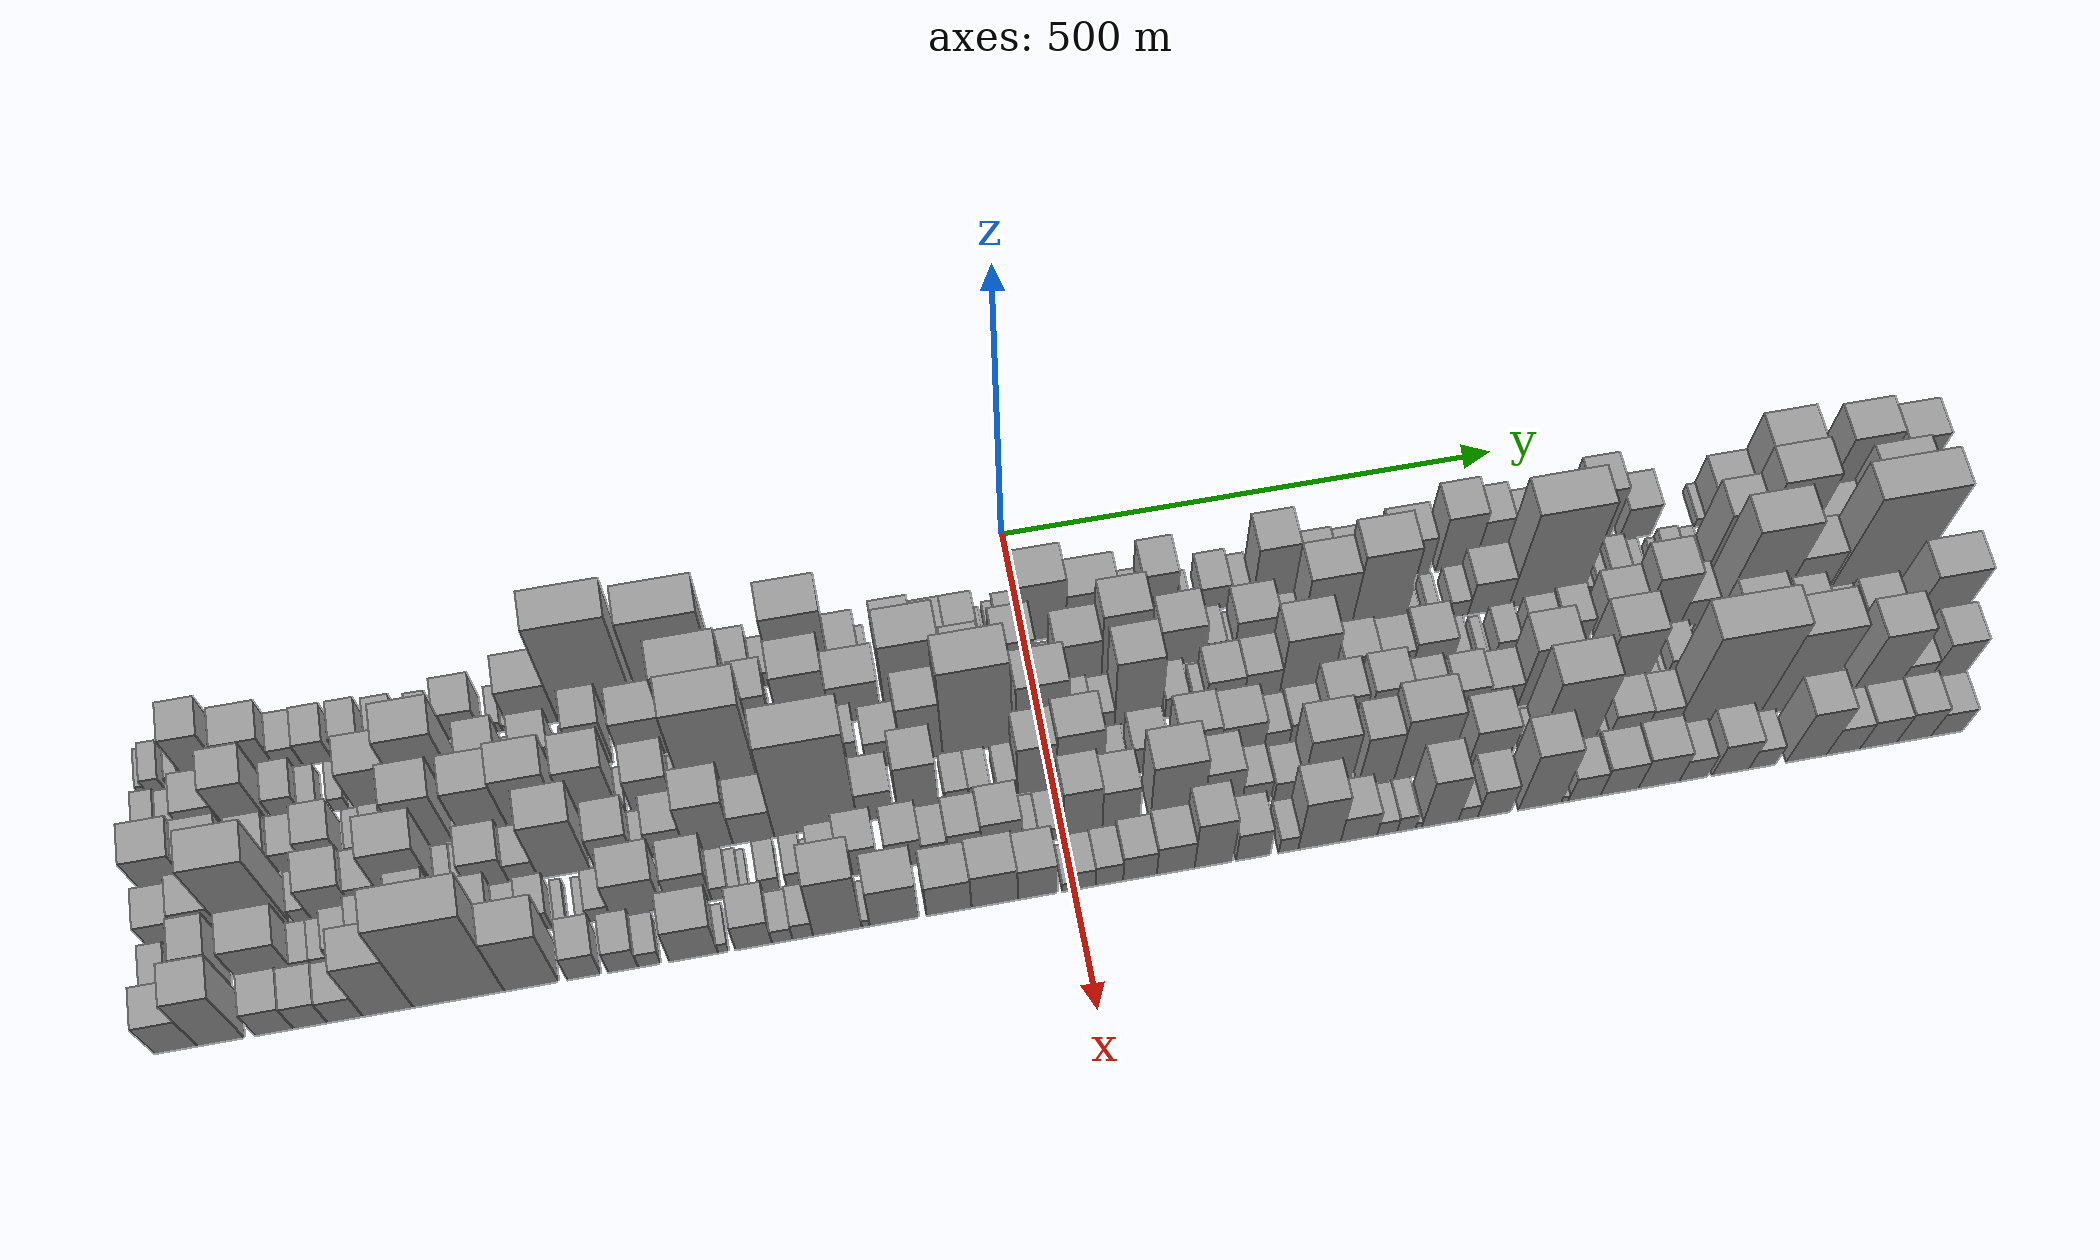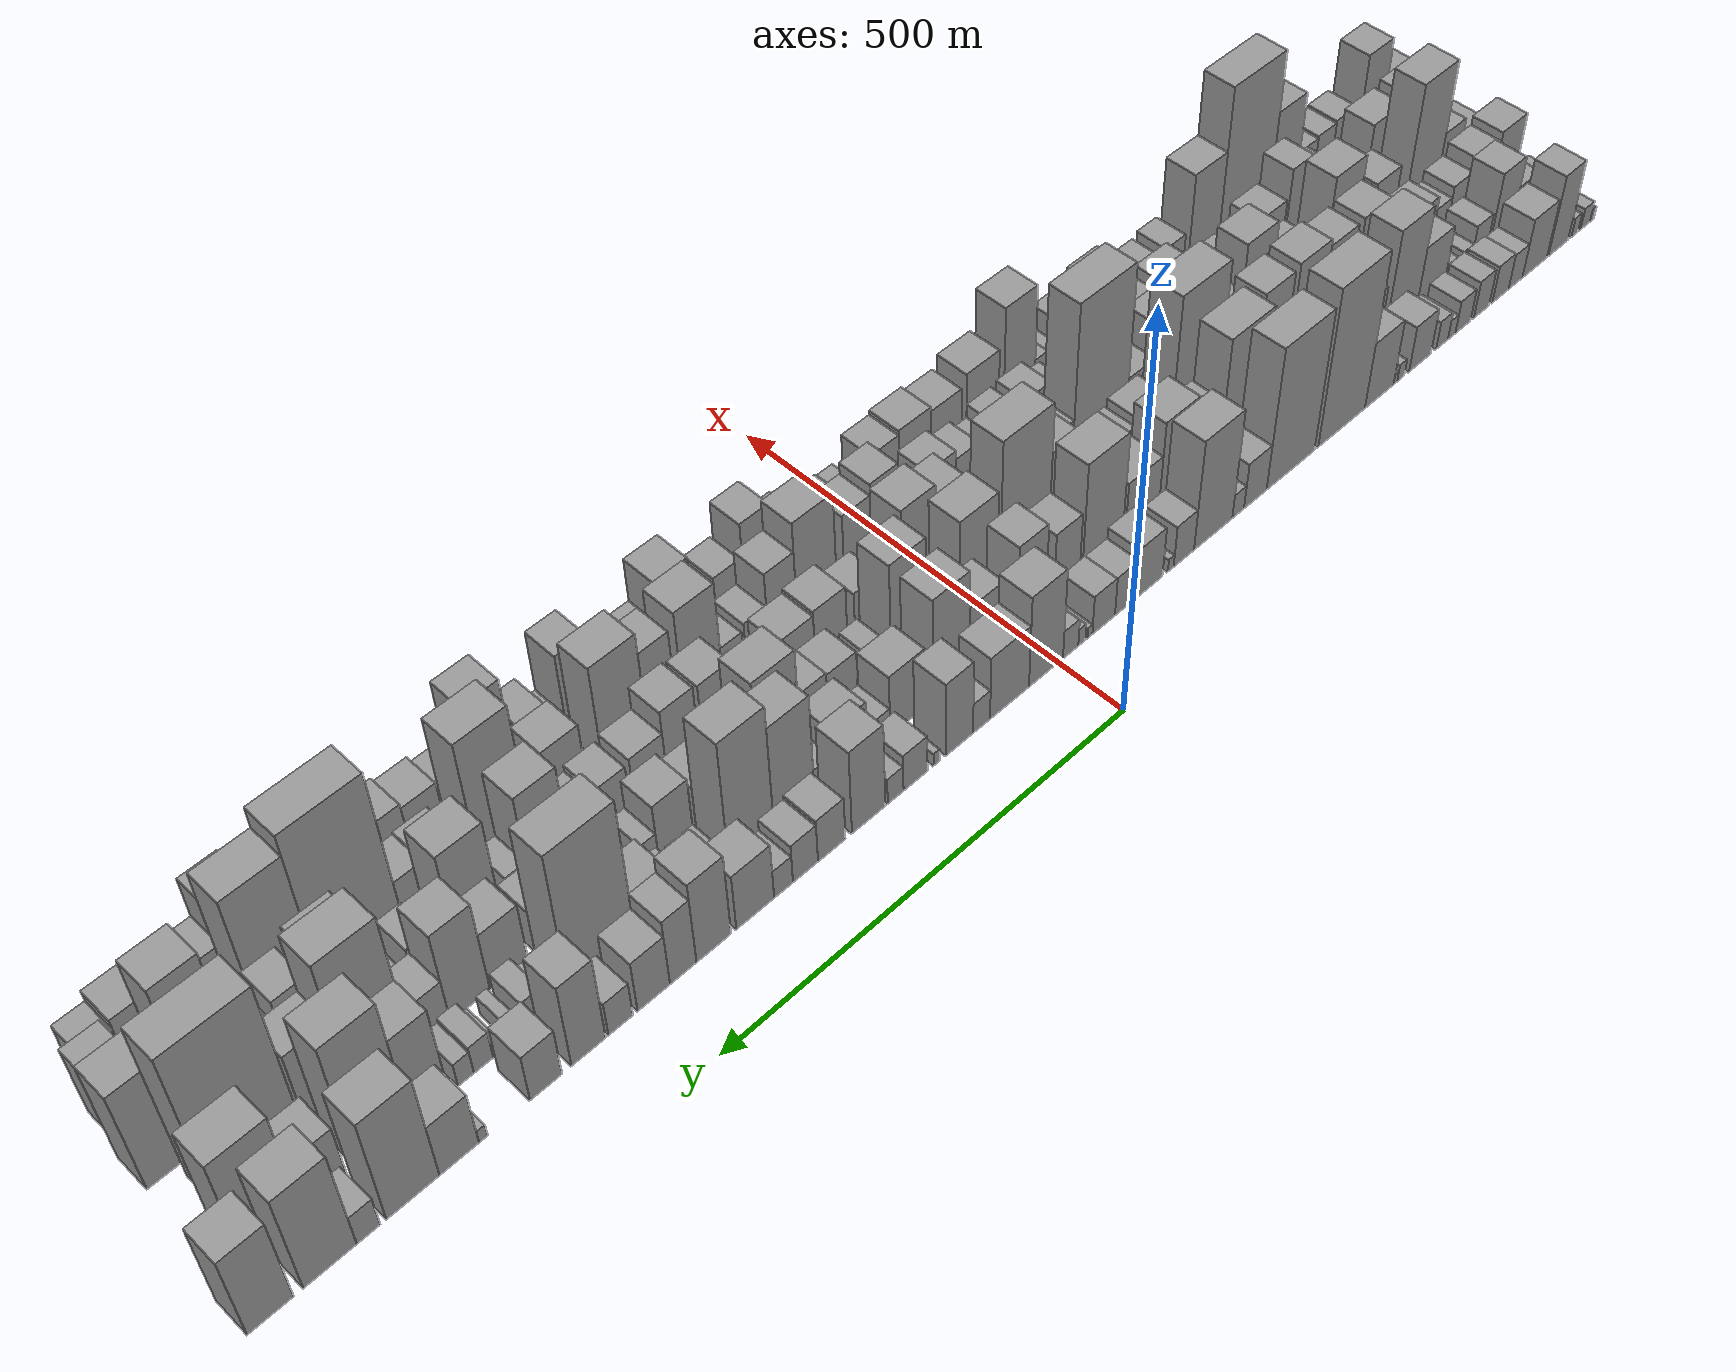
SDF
<sdf version="1.6">
 <world name="default">
  <scene>
   <sky><clouds><speed>12</speed></clouds></sky>
   <ambient>0.4 0.4 0.4 1</ambient>
   <background>0.7 0.7 0.7 1</background>
   <shadows>1</shadows>
  </scene>
  <gravity>0 0 -9.8066</gravity>
  <magnetic_field>6e-06 2.3e-05 -4.2e-05</magnetic_field>
  <physics default="0" name="default_physics" type="ode">
   <ode>
    <solver>
     <type>quick</type>
     <iters>10</iters>
     <sor>1.0</sor>
     <use_dynamic_moi_rescaling>0</use_dynamic_moi_rescaling>
    </solver>
    <constraints>
     <cfm>0</cfm>
     <erp>0.2</erp>
     <contact_max_correcting_vel>100</contact_max_correcting_vel>
     <contact_surface_layer>0.001</contact_surface_layer>
    </constraints>
   </ode>
   <max_step_size>0.004</max_step_size>
   <real_time_factor>1</real_time_factor>
   <real_time_update_rate>250</real_time_update_rate>
  </physics>
  <light name="sun" type="directional">
   <pose>0 0 10 0 0 0</pose>
   <diffuse>0.8 0.8 0.8 1</diffuse>
   <specular>0.2 0.2 0.2 1</specular>
   <attenuation>
    <range>1000</range>
    <constant>0.9</constant>
    <linear>0.01</linear>
    <quadratic>0.001</quadratic>
   </attenuation>
   <direction>-0.5 0.1 -0.9</direction>
  </light>
  <model name="building_1">
   <static>1</static>
   <pose>100.0000 -856.3155 0 0.000000 0.000000 0.000000</pose>
   <link name="link">
    <pose>0 0 9.00 0 0 0</pose>
    <collision name="collision"><geometry><box><size>40.0000 7.3690 18.0000</size></box></geometry></collision>
    <visual name="visual">
     <cast_shadows>0</cast_shadows>
     <geometry><box><size>40.0000 7.3690 18.0000</size></box></geometry>
     <material>
      <script>
       <uri>model://grey_wall/materials/scripts</uri>
       <uri>model://grey_wall/materials/textures</uri>
       <name>vrc/grey_wall</name>
      </script>
     </material>
    </visual>
   </link>
  </model>
  <model name="building_2">
   <static>1</static>
   <pose>100.0000 -843.7832 0 0.000000 0.000000 0.000000</pose>
   <link name="link">
    <pose>0 0 15.00 0 0 0</pose>
    <collision name="collision"><geometry><box><size>40.0000 17.6955 30.0000</size></box></geometry></collision>
    <visual name="visual">
     <cast_shadows>0</cast_shadows>
     <geometry><box><size>40.0000 17.6955 30.0000</size></box></geometry>
     <material>
      <script>
       <uri>model://grey_wall/materials/scripts</uri>
       <uri>model://grey_wall/materials/textures</uri>
       <name>vrc/grey_wall</name>
      </script>
     </material>
    </visual>
   </link>
  </model>
  <model name="building_3">
   <static>1</static>
   <pose>100.0000 -823.7744 0 0.000000 0.000000 0.000000</pose>
   <link name="link">
    <pose>0 0 13.50 0 0 0</pose>
    <collision name="collision"><geometry><box><size>40.0000 12.3221 27.0000</size></box></geometry></collision>
    <visual name="visual">
     <cast_shadows>0</cast_shadows>
     <geometry><box><size>40.0000 12.3221 27.0000</size></box></geometry>
     <material>
      <script>
       <uri>model://grey_wall/materials/scripts</uri>
       <uri>model://grey_wall/materials/textures</uri>
       <name>vrc/grey_wall</name>
      </script>
     </material>
    </visual>
   </link>
  </model>
  <model name="building_4">
   <static>1</static>
   <pose>100.0000 -793.5515 0 0.000000 0.000000 0.000000</pose>
   <link name="link">
    <pose>0 0 55.50 0 0 0</pose>
    <collision name="collision"><geometry><box><size>40.0000 36.1238 111.0000</size></box></geometry></collision>
    <visual name="visual">
     <cast_shadows>0</cast_shadows>
     <geometry><box><size>40.0000 36.1238 111.0000</size></box></geometry>
     <material>
      <script>
       <uri>model://grey_wall/materials/scripts</uri>
       <uri>model://grey_wall/materials/textures</uri>
       <name>vrc/grey_wall</name>
      </script>
     </material>
    </visual>
   </link>
  </model>
  <model name="building_5">
   <static>1</static>
   <pose>100.0000 -750.3410 0 0.000000 0.000000 0.000000</pose>
   <link name="link">
    <pose>0 0 40.50 0 0 0</pose>
    <collision name="collision"><geometry><box><size>40.0000 44.2971 81.0000</size></box></geometry></collision>
    <visual name="visual">
     <cast_shadows>0</cast_shadows>
     <geometry><box><size>40.0000 44.2971 81.0000</size></box></geometry>
     <material>
      <script>
       <uri>model://grey_wall/materials/scripts</uri>
       <uri>model://grey_wall/materials/textures</uri>
       <name>vrc/grey_wall</name>
      </script>
     </material>
    </visual>
   </link>
  </model>
  <model name="building_6">
   <static>1</static>
   <pose>100.0000 -715.8138 0 0.000000 0.000000 0.000000</pose>
   <link name="link">
    <pose>0 0 24.00 0 0 0</pose>
    <collision name="collision"><geometry><box><size>40.0000 24.7575 48.0000</size></box></geometry></collision>
    <visual name="visual">
     <cast_shadows>0</cast_shadows>
     <geometry><box><size>40.0000 24.7575 48.0000</size></box></geometry>
     <material>
      <script>
       <uri>model://grey_wall/materials/scripts</uri>
       <uri>model://grey_wall/materials/textures</uri>
       <name>vrc/grey_wall</name>
      </script>
     </material>
    </visual>
   </link>
  </model>
  <model name="building_7">
   <static>1</static>
   <pose>100.0000 -689.0976 0 0.000000 0.000000 0.000000</pose>
   <link name="link">
    <pose>0 0 25.50 0 0 0</pose>
    <collision name="collision"><geometry><box><size>40.0000 28.6749 51.0000</size></box></geometry></collision>
    <visual name="visual">
     <cast_shadows>0</cast_shadows>
     <geometry><box><size>40.0000 28.6749 51.0000</size></box></geometry>
     <material>
      <script>
       <uri>model://grey_wall/materials/scripts</uri>
       <uri>model://grey_wall/materials/textures</uri>
       <name>vrc/grey_wall</name>
      </script>
     </material>
    </visual>
   </link>
  </model>
  <model name="building_8">
   <static>1</static>
   <pose>100.0000 -655.4162 0 0.000000 0.000000 0.000000</pose>
   <link name="link">
    <pose>0 0 25.50 0 0 0</pose>
    <collision name="collision"><geometry><box><size>40.0000 26.6878 51.0000</size></box></geometry></collision>
    <visual name="visual">
     <cast_shadows>0</cast_shadows>
     <geometry><box><size>40.0000 26.6878 51.0000</size></box></geometry>
     <material>
      <script>
       <uri>model://grey_wall/materials/scripts</uri>
       <uri>model://grey_wall/materials/textures</uri>
       <name>vrc/grey_wall</name>
      </script>
     </material>
    </visual>
   </link>
  </model>
  <model name="building_9">
   <static>1</static>
   <pose>100.0000 -622.9957 0 0.000000 0.000000 0.000000</pose>
   <link name="link">
    <pose>0 0 22.50 0 0 0</pose>
    <collision name="collision"><geometry><box><size>40.0000 26.1534 45.0000</size></box></geometry></collision>
    <visual name="visual">
     <cast_shadows>0</cast_shadows>
     <geometry><box><size>40.0000 26.1534 45.0000</size></box></geometry>
     <material>
      <script>
       <uri>model://grey_wall/materials/scripts</uri>
       <uri>model://grey_wall/materials/textures</uri>
       <name>vrc/grey_wall</name>
      </script>
     </material>
    </visual>
   </link>
  </model>
  <model name="building_10">
   <static>1</static>
   <pose>100.0000 -603.3954 0 0.000000 0.000000 0.000000</pose>
   <link name="link">
    <pose>0 0 13.50 0 0 0</pose>
    <collision name="collision"><geometry><box><size>40.0000 13.0470 27.0000</size></box></geometry></collision>
    <visual name="visual">
     <cast_shadows>0</cast_shadows>
     <geometry><box><size>40.0000 13.0470 27.0000</size></box></geometry>
     <material>
      <script>
       <uri>model://grey_wall/materials/scripts</uri>
       <uri>model://grey_wall/materials/textures</uri>
       <name>vrc/grey_wall</name>
      </script>
     </material>
    </visual>
   </link>
  </model>
  <model name="building_11">
   <static>1</static>
   <pose>100.0000 -586.8713 0 0.000000 0.000000 0.000000</pose>
   <link name="link">
    <pose>0 0 19.50 0 0 0</pose>
    <collision name="collision"><geometry><box><size>40.0000 20.0013 39.0000</size></box></geometry></collision>
    <visual name="visual">
     <cast_shadows>0</cast_shadows>
     <geometry><box><size>40.0000 20.0013 39.0000</size></box></geometry>
     <material>
      <script>
       <uri>model://grey_wall/materials/scripts</uri>
       <uri>model://grey_wall/materials/textures</uri>
       <name>vrc/grey_wall</name>
      </script>
     </material>
    </visual>
   </link>
  </model>
  <model name="building_12">
   <static>1</static>
   <pose>100.0000 -549.4796 0 0.000000 0.000000 0.000000</pose>
   <link name="link">
    <pose>0 0 31.50 0 0 0</pose>
    <collision name="collision"><geometry><box><size>40.0000 36.7822 63.0000</size></box></geometry></collision>
    <visual name="visual">
     <cast_shadows>0</cast_shadows>
     <geometry><box><size>40.0000 36.7822 63.0000</size></box></geometry>
     <material>
      <script>
       <uri>model://grey_wall/materials/scripts</uri>
       <uri>model://grey_wall/materials/textures</uri>
       <name>vrc/grey_wall</name>
      </script>
     </material>
    </visual>
   </link>
  </model>
  <model name="building_13">
   <static>1</static>
   <pose>100.0000 -517.1850 0 0.000000 0.000000 0.000000</pose>
   <link name="link">
    <pose>0 0 12.00 0 0 0</pose>
    <collision name="collision"><geometry><box><size>40.0000 11.8070 24.0000</size></box></geometry></collision>
    <visual name="visual">
     <cast_shadows>0</cast_shadows>
     <geometry><box><size>40.0000 11.8070 24.0000</size></box></geometry>
     <material>
      <script>
       <uri>model://grey_wall/materials/scripts</uri>
       <uri>model://grey_wall/materials/textures</uri>
       <name>vrc/grey_wall</name>
      </script>
     </material>
    </visual>
   </link>
  </model>
  <model name="building_14">
   <static>1</static>
   <pose>100.0000 -508.1514 0 0.000000 0.000000 0.000000</pose>
   <link name="link">
    <pose>0 0 7.50 0 0 0</pose>
    <collision name="collision"><geometry><box><size>40.0000 6.2602 15.0000</size></box></geometry></collision>
    <visual name="visual">
     <cast_shadows>0</cast_shadows>
     <geometry><box><size>40.0000 6.2602 15.0000</size></box></geometry>
     <material>
      <script>
       <uri>model://grey_wall/materials/scripts</uri>
       <uri>model://grey_wall/materials/textures</uri>
       <name>vrc/grey_wall</name>
      </script>
     </material>
    </visual>
   </link>
  </model>
  <model name="building_15">
   <static>1</static>
   <pose>100.0000 -481.4193 0 0.000000 0.000000 0.000000</pose>
   <link name="link">
    <pose>0 0 45.00 0 0 0</pose>
    <collision name="collision"><geometry><box><size>40.0000 47.2039 90.0000</size></box></geometry></collision>
    <visual name="visual">
     <cast_shadows>0</cast_shadows>
     <geometry><box><size>40.0000 47.2039 90.0000</size></box></geometry>
     <material>
      <script>
       <uri>model://grey_wall/materials/scripts</uri>
       <uri>model://grey_wall/materials/textures</uri>
       <name>vrc/grey_wall</name>
      </script>
     </material>
    </visual>
   </link>
  </model>
  <model name="building_16">
   <static>1</static>
   <pose>100.0000 -420.2112 0 0.000000 0.000000 0.000000</pose>
   <link name="link">
    <pose>0 0 106.50 0 0 0</pose>
    <collision name="collision"><geometry><box><size>40.0000 75.2124 213.0000</size></box></geometry></collision>
    <visual name="visual">
     <cast_shadows>0</cast_shadows>
     <geometry><box><size>40.0000 75.2124 213.0000</size></box></geometry>
     <material>
      <script>
       <uri>model://grey_wall/materials/scripts</uri>
       <uri>model://grey_wall/materials/textures</uri>
       <name>vrc/grey_wall</name>
      </script>
     </material>
    </visual>
   </link>
  </model>
  <model name="building_17">
   <static>1</static>
   <pose>100.0000 -339.1121 0 0.000000 0.000000 0.000000</pose>
   <link name="link">
    <pose>0 0 96.00 0 0 0</pose>
    <collision name="collision"><geometry><box><size>40.0000 74.9859 192.0000</size></box></geometry></collision>
    <visual name="visual">
     <cast_shadows>0</cast_shadows>
     <geometry><box><size>40.0000 74.9859 192.0000</size></box></geometry>
     <material>
      <script>
       <uri>model://grey_wall/materials/scripts</uri>
       <uri>model://grey_wall/materials/textures</uri>
       <name>vrc/grey_wall</name>
      </script>
     </material>
    </visual>
   </link>
  </model>
  <model name="building_18">
   <static>1</static>
   <pose>100.0000 -284.2933 0 0.000000 0.000000 0.000000</pose>
   <link name="link">
    <pose>0 0 31.50 0 0 0</pose>
    <collision name="collision"><geometry><box><size>40.0000 34.6517 63.0000</size></box></geometry></collision>
    <visual name="visual">
     <cast_shadows>0</cast_shadows>
     <geometry><box><size>40.0000 34.6517 63.0000</size></box></geometry>
     <material>
      <script>
       <uri>model://grey_wall/materials/scripts</uri>
       <uri>model://grey_wall/materials/textures</uri>
       <name>vrc/grey_wall</name>
      </script>
     </material>
    </visual>
   </link>
  </model>
  <model name="building_19">
   <static>1</static>
   <pose>100.0000 -258.0641 0 0.000000 0.000000 0.000000</pose>
   <link name="link">
    <pose>0 0 16.50 0 0 0</pose>
    <collision name="collision"><geometry><box><size>40.0000 17.8066 33.0000</size></box></geometry></collision>
    <visual name="visual">
     <cast_shadows>0</cast_shadows>
     <geometry><box><size>40.0000 17.8066 33.0000</size></box></geometry>
     <material>
      <script>
       <uri>model://grey_wall/materials/scripts</uri>
       <uri>model://grey_wall/materials/textures</uri>
       <name>vrc/grey_wall</name>
      </script>
     </material>
    </visual>
   </link>
  </model>
  <model name="building_20">
   <static>1</static>
   <pose>100.0000 -220.5488 0 0.000000 0.000000 0.000000</pose>
   <link name="link">
    <pose>0 0 75.00 0 0 0</pose>
    <collision name="collision"><geometry><box><size>40.0000 57.2241 150.0000</size></box></geometry></collision>
    <visual name="visual">
     <cast_shadows>0</cast_shadows>
     <geometry><box><size>40.0000 57.2241 150.0000</size></box></geometry>
     <material>
      <script>
       <uri>model://grey_wall/materials/scripts</uri>
       <uri>model://grey_wall/materials/textures</uri>
       <name>vrc/grey_wall</name>
      </script>
     </material>
    </visual>
   </link>
  </model>
  <model name="building_21">
   <static>1</static>
   <pose>100.0000 -176.9536 0 0.000000 0.000000 0.000000</pose>
   <link name="link">
    <pose>0 0 28.50 0 0 0</pose>
    <collision name="collision"><geometry><box><size>40.0000 29.9664 57.0000</size></box></geometry></collision>
    <visual name="visual">
     <cast_shadows>0</cast_shadows>
     <geometry><box><size>40.0000 29.9664 57.0000</size></box></geometry>
     <material>
      <script>
       <uri>model://grey_wall/materials/scripts</uri>
       <uri>model://grey_wall/materials/textures</uri>
       <name>vrc/grey_wall</name>
      </script>
     </material>
    </visual>
   </link>
  </model>
  <model name="building_22">
   <static>1</static>
   <pose>100.0000 -157.7636 0 0.000000 0.000000 0.000000</pose>
   <link name="link">
    <pose>0 0 9.00 0 0 0</pose>
    <collision name="collision"><geometry><box><size>40.0000 8.4137 18.0000</size></box></geometry></collision>
    <visual name="visual">
     <cast_shadows>0</cast_shadows>
     <geometry><box><size>40.0000 8.4137 18.0000</size></box></geometry>
     <material>
      <script>
       <uri>model://grey_wall/materials/scripts</uri>
       <uri>model://grey_wall/materials/textures</uri>
       <name>vrc/grey_wall</name>
      </script>
     </material>
    </visual>
   </link>
  </model>
  <model name="building_23">
   <static>1</static>
   <pose>100.0000 -126.8365 0 0.000000 0.000000 0.000000</pose>
   <link name="link">
    <pose>0 0 34.50 0 0 0</pose>
    <collision name="collision"><geometry><box><size>40.0000 37.4404 69.0000</size></box></geometry></collision>
    <visual name="visual">
     <cast_shadows>0</cast_shadows>
     <geometry><box><size>40.0000 37.4404 69.0000</size></box></geometry>
     <material>
      <script>
       <uri>model://grey_wall/materials/scripts</uri>
       <uri>model://grey_wall/materials/textures</uri>
       <name>vrc/grey_wall</name>
      </script>
     </material>
    </visual>
   </link>
  </model>
  <model name="building_24">
   <static>1</static>
   <pose>100.0000 -92.8020 0 0.000000 0.000000 0.000000</pose>
   <link name="link">
    <pose>0 0 27.00 0 0 0</pose>
    <collision name="collision"><geometry><box><size>40.0000 30.6288 54.0000</size></box></geometry></collision>
    <visual name="visual">
     <cast_shadows>0</cast_shadows>
     <geometry><box><size>40.0000 30.6288 54.0000</size></box></geometry>
     <material>
      <script>
       <uri>model://grey_wall/materials/scripts</uri>
       <uri>model://grey_wall/materials/textures</uri>
       <name>vrc/grey_wall</name>
      </script>
     </material>
    </visual>
   </link>
  </model>
  <model name="building_25">
   <static>1</static>
   <pose>100.0000 -61.5863 0 0.000000 0.000000 0.000000</pose>
   <link name="link">
    <pose>0 0 27.00 0 0 0</pose>
    <collision name="collision"><geometry><box><size>40.0000 31.8025 54.0000</size></box></geometry></collision>
    <visual name="visual">
     <cast_shadows>0</cast_shadows>
     <geometry><box><size>40.0000 31.8025 54.0000</size></box></geometry>
     <material>
      <script>
       <uri>model://grey_wall/materials/scripts</uri>
       <uri>model://grey_wall/materials/textures</uri>
       <name>vrc/grey_wall</name>
      </script>
     </material>
    </visual>
   </link>
  </model>
  <model name="building_26">
   <static>1</static>
   <pose>100.0000 -42.3465 0 0.000000 0.000000 0.000000</pose>
   <link name="link">
    <pose>0 0 7.50 0 0 0</pose>
    <collision name="collision"><geometry><box><size>40.0000 6.6771 15.0000</size></box></geometry></collision>
    <visual name="visual">
     <cast_shadows>0</cast_shadows>
     <geometry><box><size>40.0000 6.6771 15.0000</size></box></geometry>
     <material>
      <script>
       <uri>model://grey_wall/materials/scripts</uri>
       <uri>model://grey_wall/materials/textures</uri>
       <name>vrc/grey_wall</name>
      </script>
     </material>
    </visual>
   </link>
  </model>
  <model name="building_27">
   <static>1</static>
   <pose>100.0000 -31.0398 0 0.000000 0.000000 0.000000</pose>
   <link name="link">
    <pose>0 0 12.00 0 0 0</pose>
    <collision name="collision"><geometry><box><size>40.0000 9.9365 24.0000</size></box></geometry></collision>
    <visual name="visual">
     <cast_shadows>0</cast_shadows>
     <geometry><box><size>40.0000 9.9365 24.0000</size></box></geometry>
     <material>
      <script>
       <uri>model://grey_wall/materials/scripts</uri>
       <uri>model://grey_wall/materials/textures</uri>
       <name>vrc/grey_wall</name>
      </script>
     </material>
    </visual>
   </link>
  </model>
  <model name="building_28">
   <static>1</static>
   <pose>100.0000 -15.5173 0 0.000000 0.000000 0.000000</pose>
   <link name="link">
    <pose>0 0 19.50 0 0 0</pose>
    <collision name="collision"><geometry><box><size>40.0000 21.1083 39.0000</size></box></geometry></collision>
    <visual name="visual">
     <cast_shadows>0</cast_shadows>
     <geometry><box><size>40.0000 21.1083 39.0000</size></box></geometry>
     <material>
      <script>
       <uri>model://grey_wall/materials/scripts</uri>
       <uri>model://grey_wall/materials/textures</uri>
       <name>vrc/grey_wall</name>
      </script>
     </material>
    </visual>
   </link>
  </model>
  <model name="building_29">
   <static>1</static>
   <pose>100.0000 18.2256 0 0.000000 0.000000 0.000000</pose>
   <link name="link">
    <pose>0 0 63.00 0 0 0</pose>
    <collision name="collision"><geometry><box><size>40.0000 46.3776 126.0000</size></box></geometry></collision>
    <visual name="visual">
     <cast_shadows>0</cast_shadows>
     <geometry><box><size>40.0000 46.3776 126.0000</size></box></geometry>
     <material>
      <script>
       <uri>model://grey_wall/materials/scripts</uri>
       <uri>model://grey_wall/materials/textures</uri>
       <name>vrc/grey_wall</name>
      </script>
     </material>
    </visual>
   </link>
  </model>
  <model name="building_30">
   <static>1</static>
   <pose>100.0000 67.4377 0 0.000000 0.000000 0.000000</pose>
   <link name="link">
    <pose>0 0 43.50 0 0 0</pose>
    <collision name="collision"><geometry><box><size>40.0000 52.0465 87.0000</size></box></geometry></collision>
    <visual name="visual">
     <cast_shadows>0</cast_shadows>
     <geometry><box><size>40.0000 52.0465 87.0000</size></box></geometry>
     <material>
      <script>
       <uri>model://grey_wall/materials/scripts</uri>
       <uri>model://grey_wall/materials/textures</uri>
       <name>vrc/grey_wall</name>
      </script>
     </material>
    </visual>
   </link>
  </model>
  <model name="building_31">
   <static>1</static>
   <pose>100.0000 104.6148 0 0.000000 0.000000 0.000000</pose>
   <link name="link">
    <pose>0 0 21.00 0 0 0</pose>
    <collision name="collision"><geometry><box><size>40.0000 22.3077 42.0000</size></box></geometry></collision>
    <visual name="visual">
     <cast_shadows>0</cast_shadows>
     <geometry><box><size>40.0000 22.3077 42.0000</size></box></geometry>
     <material>
      <script>
       <uri>model://grey_wall/materials/scripts</uri>
       <uri>model://grey_wall/materials/textures</uri>
       <name>vrc/grey_wall</name>
      </script>
     </material>
    </visual>
   </link>
  </model>
  <model name="building_32">
   <static>1</static>
   <pose>100.0000 133.3518 0 0.000000 0.000000 0.000000</pose>
   <link name="link">
    <pose>0 0 51.00 0 0 0</pose>
    <collision name="collision"><geometry><box><size>40.0000 35.1663 102.0000</size></box></geometry></collision>
    <visual name="visual">
     <cast_shadows>0</cast_shadows>
     <geometry><box><size>40.0000 35.1663 102.0000</size></box></geometry>
     <material>
      <script>
       <uri>model://grey_wall/materials/scripts</uri>
       <uri>model://grey_wall/materials/textures</uri>
       <name>vrc/grey_wall</name>
      </script>
     </material>
    </visual>
   </link>
  </model>
  <model name="building_33">
   <static>1</static>
   <pose>100.0000 162.8169 0 0.000000 0.000000 0.000000</pose>
   <link name="link">
    <pose>0 0 9.00 0 0 0</pose>
    <collision name="collision"><geometry><box><size>40.0000 7.7639 18.0000</size></box></geometry></collision>
    <visual name="visual">
     <cast_shadows>0</cast_shadows>
     <geometry><box><size>40.0000 7.7639 18.0000</size></box></geometry>
     <material>
      <script>
       <uri>model://grey_wall/materials/scripts</uri>
       <uri>model://grey_wall/materials/textures</uri>
       <name>vrc/grey_wall</name>
      </script>
     </material>
    </visual>
   </link>
  </model>
  <model name="building_34">
   <static>1</static>
   <pose>100.0000 189.9409 0 0.000000 0.000000 0.000000</pose>
   <link name="link">
    <pose>0 0 25.50 0 0 0</pose>
    <collision name="collision"><geometry><box><size>40.0000 30.4841 51.0000</size></box></geometry></collision>
    <visual name="visual">
     <cast_shadows>0</cast_shadows>
     <geometry><box><size>40.0000 30.4841 51.0000</size></box></geometry>
     <material>
      <script>
       <uri>model://grey_wall/materials/scripts</uri>
       <uri>model://grey_wall/materials/textures</uri>
       <name>vrc/grey_wall</name>
      </script>
     </material>
    </visual>
   </link>
  </model>
  <model name="building_35">
   <static>1</static>
   <pose>100.0000 215.1093 0 0.000000 0.000000 0.000000</pose>
   <link name="link">
    <pose>0 0 18.00 0 0 0</pose>
    <collision name="collision"><geometry><box><size>40.0000 19.8527 36.0000</size></box></geometry></collision>
    <visual name="visual">
     <cast_shadows>0</cast_shadows>
     <geometry><box><size>40.0000 19.8527 36.0000</size></box></geometry>
     <material>
      <script>
       <uri>model://grey_wall/materials/scripts</uri>
       <uri>model://grey_wall/materials/textures</uri>
       <name>vrc/grey_wall</name>
      </script>
     </material>
    </visual>
   </link>
  </model>
  <model name="building_36">
   <static>1</static>
   <pose>100.0000 248.7169 0 0.000000 0.000000 0.000000</pose>
   <link name="link">
    <pose>0 0 58.50 0 0 0</pose>
    <collision name="collision"><geometry><box><size>40.0000 41.3625 117.0000</size></box></geometry></collision>
    <visual name="visual">
     <cast_shadows>0</cast_shadows>
     <geometry><box><size>40.0000 41.3625 117.0000</size></box></geometry>
     <material>
      <script>
       <uri>model://grey_wall/materials/scripts</uri>
       <uri>model://grey_wall/materials/textures</uri>
       <name>vrc/grey_wall</name>
      </script>
     </material>
    </visual>
   </link>
  </model>
  <model name="building_37">
   <static>1</static>
   <pose>100.0000 294.0604 0 0.000000 0.000000 0.000000</pose>
   <link name="link">
    <pose>0 0 30.00 0 0 0</pose>
    <collision name="collision"><geometry><box><size>40.0000 33.3245 60.0000</size></box></geometry></collision>
    <visual name="visual">
     <cast_shadows>0</cast_shadows>
     <geometry><box><size>40.0000 33.3245 60.0000</size></box></geometry>
     <material>
      <script>
       <uri>model://grey_wall/materials/scripts</uri>
       <uri>model://grey_wall/materials/textures</uri>
       <name>vrc/grey_wall</name>
      </script>
     </material>
    </visual>
   </link>
  </model>
  <model name="building_38">
   <static>1</static>
   <pose>100.0000 325.7428 0 0.000000 0.000000 0.000000</pose>
   <link name="link">
    <pose>0 0 27.00 0 0 0</pose>
    <collision name="collision"><geometry><box><size>40.0000 30.0403 54.0000</size></box></geometry></collision>
    <visual name="visual">
     <cast_shadows>0</cast_shadows>
     <geometry><box><size>40.0000 30.0403 54.0000</size></box></geometry>
     <material>
      <script>
       <uri>model://grey_wall/materials/scripts</uri>
       <uri>model://grey_wall/materials/textures</uri>
       <name>vrc/grey_wall</name>
      </script>
     </material>
    </visual>
   </link>
  </model>
  <model name="building_39">
   <static>1</static>
   <pose>100.0000 351.9059 0 0.000000 0.000000 0.000000</pose>
   <link name="link">
    <pose>0 0 19.50 0 0 0</pose>
    <collision name="collision"><geometry><box><size>40.0000 22.2858 39.0000</size></box></geometry></collision>
    <visual name="visual">
     <cast_shadows>0</cast_shadows>
     <geometry><box><size>40.0000 22.2858 39.0000</size></box></geometry>
     <material>
      <script>
       <uri>model://grey_wall/materials/scripts</uri>
       <uri>model://grey_wall/materials/textures</uri>
       <name>vrc/grey_wall</name>
      </script>
     </material>
    </visual>
   </link>
  </model>
  <model name="building_40">
   <static>1</static>
   <pose>100.0000 385.2100 0 0.000000 0.000000 0.000000</pose>
   <link name="link">
    <pose>0 0 39.00 0 0 0</pose>
    <collision name="collision"><geometry><box><size>40.0000 44.3224 78.0000</size></box></geometry></collision>
    <visual name="visual">
     <cast_shadows>0</cast_shadows>
     <geometry><box><size>40.0000 44.3224 78.0000</size></box></geometry>
     <material>
      <script>
       <uri>model://grey_wall/materials/scripts</uri>
       <uri>model://grey_wall/materials/textures</uri>
       <name>vrc/grey_wall</name>
      </script>
     </material>
    </visual>
   </link>
  </model>
  <model name="building_41">
   <static>1</static>
   <pose>100.0000 433.2024 0 0.000000 0.000000 0.000000</pose>
   <link name="link">
    <pose>0 0 57.00 0 0 0</pose>
    <collision name="collision"><geometry><box><size>40.0000 39.6624 114.0000</size></box></geometry></collision>
    <visual name="visual">
     <cast_shadows>0</cast_shadows>
     <geometry><box><size>40.0000 39.6624 114.0000</size></box></geometry>
     <material>
      <script>
       <uri>model://grey_wall/materials/scripts</uri>
       <uri>model://grey_wall/materials/textures</uri>
       <name>vrc/grey_wall</name>
      </script>
     </material>
    </visual>
   </link>
  </model>
  <model name="building_42">
   <static>1</static>
   <pose>100.0000 467.9742 0 0.000000 0.000000 0.000000</pose>
   <link name="link">
    <pose>0 0 46.50 0 0 0</pose>
    <collision name="collision"><geometry><box><size>40.0000 29.8813 93.0000</size></box></geometry></collision>
    <visual name="visual">
     <cast_shadows>0</cast_shadows>
     <geometry><box><size>40.0000 29.8813 93.0000</size></box></geometry>
     <material>
      <script>
       <uri>model://grey_wall/materials/scripts</uri>
       <uri>model://grey_wall/materials/textures</uri>
       <name>vrc/grey_wall</name>
      </script>
     </material>
    </visual>
   </link>
  </model>
  <model name="building_43">
   <static>1</static>
   <pose>100.0000 500.9659 0 0.000000 0.000000 0.000000</pose>
   <link name="link">
    <pose>0 0 36.00 0 0 0</pose>
    <collision name="collision"><geometry><box><size>40.0000 36.1020 72.0000</size></box></geometry></collision>
    <visual name="visual">
     <cast_shadows>0</cast_shadows>
     <geometry><box><size>40.0000 36.1020 72.0000</size></box></geometry>
     <material>
      <script>
       <uri>model://grey_wall/materials/scripts</uri>
       <uri>model://grey_wall/materials/textures</uri>
       <name>vrc/grey_wall</name>
      </script>
     </material>
    </visual>
   </link>
  </model>
  <model name="building_44">
   <static>1</static>
   <pose>100.0000 537.4547 0 0.000000 0.000000 0.000000</pose>
   <link name="link">
    <pose>0 0 24.00 0 0 0</pose>
    <collision name="collision"><geometry><box><size>40.0000 26.8757 48.0000</size></box></geometry></collision>
    <visual name="visual">
     <cast_shadows>0</cast_shadows>
     <geometry><box><size>40.0000 26.8757 48.0000</size></box></geometry>
     <material>
      <script>
       <uri>model://grey_wall/materials/scripts</uri>
       <uri>model://grey_wall/materials/textures</uri>
       <name>vrc/grey_wall</name>
      </script>
     </material>
    </visual>
   </link>
  </model>
  <model name="building_45">
   <static>1</static>
   <pose>100.0000 572.2795 0 0.000000 0.000000 0.000000</pose>
   <link name="link">
    <pose>0 0 58.50 0 0 0</pose>
    <collision name="collision"><geometry><box><size>40.0000 36.7738 117.0000</size></box></geometry></collision>
    <visual name="visual">
     <cast_shadows>0</cast_shadows>
     <geometry><box><size>40.0000 36.7738 117.0000</size></box></geometry>
     <material>
      <script>
       <uri>model://grey_wall/materials/scripts</uri>
       <uri>model://grey_wall/materials/textures</uri>
       <name>vrc/grey_wall</name>
      </script>
     </material>
    </visual>
   </link>
  </model>
  <model name="building_46">
   <static>1</static>
   <pose>100.0000 617.5958 0 0.000000 0.000000 0.000000</pose>
   <link name="link">
    <pose>0 0 33.00 0 0 0</pose>
    <collision name="collision"><geometry><box><size>40.0000 33.8589 66.0000</size></box></geometry></collision>
    <visual name="visual">
     <cast_shadows>0</cast_shadows>
     <geometry><box><size>40.0000 33.8589 66.0000</size></box></geometry>
     <material>
      <script>
       <uri>model://grey_wall/materials/scripts</uri>
       <uri>model://grey_wall/materials/textures</uri>
       <name>vrc/grey_wall</name>
      </script>
     </material>
    </visual>
   </link>
  </model>
  <model name="building_47">
   <static>1</static>
   <pose>100.0000 682.8618 0 0.000000 0.000000 0.000000</pose>
   <link name="link">
    <pose>0 0 9.00 0 0 0</pose>
    <collision name="collision"><geometry><box><size>40.0000 8.8910 18.0000</size></box></geometry></collision>
    <visual name="visual">
     <cast_shadows>0</cast_shadows>
     <geometry><box><size>40.0000 8.8910 18.0000</size></box></geometry>
     <material>
      <script>
       <uri>model://grey_wall/materials/scripts</uri>
       <uri>model://grey_wall/materials/textures</uri>
       <name>vrc/grey_wall</name>
      </script>
     </material>
    </visual>
   </link>
  </model>
  <model name="building_48">
   <static>1</static>
   <pose>100.0000 707.3021 0 0.000000 0.000000 0.000000</pose>
   <link name="link">
    <pose>0 0 37.50 0 0 0</pose>
    <collision name="collision"><geometry><box><size>40.0000 39.9896 75.0000</size></box></geometry></collision>
    <visual name="visual">
     <cast_shadows>0</cast_shadows>
     <geometry><box><size>40.0000 39.9896 75.0000</size></box></geometry>
     <material>
      <script>
       <uri>model://grey_wall/materials/scripts</uri>
       <uri>model://grey_wall/materials/textures</uri>
       <name>vrc/grey_wall</name>
      </script>
     </material>
    </visual>
   </link>
  </model>
  <model name="building_49">
   <static>1</static>
   <pose>100.0000 753.6165 0 0.000000 0.000000 0.000000</pose>
   <link name="link">
    <pose>0 0 73.50 0 0 0</pose>
    <collision name="collision"><geometry><box><size>40.0000 52.6392 147.0000</size></box></geometry></collision>
    <visual name="visual">
     <cast_shadows>0</cast_shadows>
     <geometry><box><size>40.0000 52.6392 147.0000</size></box></geometry>
     <material>
      <script>
       <uri>model://grey_wall/materials/scripts</uri>
       <uri>model://grey_wall/materials/textures</uri>
       <name>vrc/grey_wall</name>
      </script>
     </material>
    </visual>
   </link>
  </model>
  <model name="building_50">
   <static>1</static>
   <pose>100.0000 797.3405 0 0.000000 0.000000 0.000000</pose>
   <link name="link">
    <pose>0 0 21.00 0 0 0</pose>
    <collision name="collision"><geometry><box><size>40.0000 22.8088 42.0000</size></box></geometry></collision>
    <visual name="visual">
     <cast_shadows>0</cast_shadows>
     <geometry><box><size>40.0000 22.8088 42.0000</size></box></geometry>
     <material>
      <script>
       <uri>model://grey_wall/materials/scripts</uri>
       <uri>model://grey_wall/materials/textures</uri>
       <name>vrc/grey_wall</name>
      </script>
     </material>
    </visual>
   </link>
  </model>
  <model name="building_51">
   <static>1</static>
   <pose>100.0000 834.2517 0 0.000000 0.000000 0.000000</pose>
   <link name="link">
    <pose>0 0 69.00 0 0 0</pose>
    <collision name="collision"><geometry><box><size>40.0000 51.0136 138.0000</size></box></geometry></collision>
    <visual name="visual">
     <cast_shadows>0</cast_shadows>
     <geometry><box><size>40.0000 51.0136 138.0000</size></box></geometry>
     <material>
      <script>
       <uri>model://grey_wall/materials/scripts</uri>
       <uri>model://grey_wall/materials/textures</uri>
       <name>vrc/grey_wall</name>
      </script>
     </material>
    </visual>
   </link>
  </model>
  <model name="building_52">
   <static>1</static>
   <pose>100.0000 890.4065 0 0.000000 0.000000 0.000000</pose>
   <link name="link">
    <pose>0 0 58.50 0 0 0</pose>
    <collision name="collision"><geometry><box><size>40.0000 43.2959 117.0000</size></box></geometry></collision>
    <visual name="visual">
     <cast_shadows>0</cast_shadows>
     <geometry><box><size>40.0000 43.2959 117.0000</size></box></geometry>
     <material>
      <script>
       <uri>model://grey_wall/materials/scripts</uri>
       <uri>model://grey_wall/materials/textures</uri>
       <name>vrc/grey_wall</name>
      </script>
     </material>
    </visual>
   </link>
  </model>
  <model name="building_53">
   <static>1</static>
   <pose>152.0000 -849.6962 0 0.000000 0.000000 0.000000</pose>
   <link name="link">
    <pose>0 0 18.00 0 0 0</pose>
    <collision name="collision"><geometry><box><size>40.0000 20.6076 36.0000</size></box></geometry></collision>
    <visual name="visual">
     <cast_shadows>0</cast_shadows>
     <geometry><box><size>40.0000 20.6076 36.0000</size></box></geometry>
     <material>
      <script>
       <uri>model://grey_wall/materials/scripts</uri>
       <uri>model://grey_wall/materials/textures</uri>
       <name>vrc/grey_wall</name>
      </script>
     </material>
    </visual>
   </link>
  </model>
  <model name="building_54">
   <static>1</static>
   <pose>152.0000 -830.8529 0 0.000000 0.000000 0.000000</pose>
   <link name="link">
    <pose>0 0 15.00 0 0 0</pose>
    <collision name="collision"><geometry><box><size>40.0000 17.0790 30.0000</size></box></geometry></collision>
    <visual name="visual">
     <cast_shadows>0</cast_shadows>
     <geometry><box><size>40.0000 17.0790 30.0000</size></box></geometry>
     <material>
      <script>
       <uri>model://grey_wall/materials/scripts</uri>
       <uri>model://grey_wall/materials/textures</uri>
       <name>vrc/grey_wall</name>
      </script>
     </material>
    </visual>
   </link>
  </model>
  <model name="building_55">
   <static>1</static>
   <pose>152.0000 -798.5670 0 0.000000 0.000000 0.000000</pose>
   <link name="link">
    <pose>0 0 31.50 0 0 0</pose>
    <collision name="collision"><geometry><box><size>40.0000 37.4928 63.0000</size></box></geometry></collision>
    <visual name="visual">
     <cast_shadows>0</cast_shadows>
     <geometry><box><size>40.0000 37.4928 63.0000</size></box></geometry>
     <material>
      <script>
       <uri>model://grey_wall/materials/scripts</uri>
       <uri>model://grey_wall/materials/textures</uri>
       <name>vrc/grey_wall</name>
      </script>
     </material>
    </visual>
   </link>
  </model>
  <model name="building_56">
   <static>1</static>
   <pose>152.0000 -759.9912 0 0.000000 0.000000 0.000000</pose>
   <link name="link">
    <pose>0 0 52.50 0 0 0</pose>
    <collision name="collision"><geometry><box><size>40.0000 39.6589 105.0000</size></box></geometry></collision>
    <visual name="visual">
     <cast_shadows>0</cast_shadows>
     <geometry><box><size>40.0000 39.6589 105.0000</size></box></geometry>
     <material>
      <script>
       <uri>model://grey_wall/materials/scripts</uri>
       <uri>model://grey_wall/materials/textures</uri>
       <name>vrc/grey_wall</name>
      </script>
     </material>
    </visual>
   </link>
  </model>
  <model name="building_57">
   <static>1</static>
   <pose>152.0000 -721.1767 0 0.000000 0.000000 0.000000</pose>
   <link name="link">
    <pose>0 0 27.00 0 0 0</pose>
    <collision name="collision"><geometry><box><size>40.0000 27.9700 54.0000</size></box></geometry></collision>
    <visual name="visual">
     <cast_shadows>0</cast_shadows>
     <geometry><box><size>40.0000 27.9700 54.0000</size></box></geometry>
     <material>
      <script>
       <uri>model://grey_wall/materials/scripts</uri>
       <uri>model://grey_wall/materials/textures</uri>
       <name>vrc/grey_wall</name>
      </script>
     </material>
    </visual>
   </link>
  </model>
  <model name="building_58">
   <static>1</static>
   <pose>152.0000 -698.2684 0 0.000000 0.000000 0.000000</pose>
   <link name="link">
    <pose>0 0 15.00 0 0 0</pose>
    <collision name="collision"><geometry><box><size>40.0000 17.8467 30.0000</size></box></geometry></collision>
    <visual name="visual">
     <cast_shadows>0</cast_shadows>
     <geometry><box><size>40.0000 17.8467 30.0000</size></box></geometry>
     <material>
      <script>
       <uri>model://grey_wall/materials/scripts</uri>
       <uri>model://grey_wall/materials/textures</uri>
       <name>vrc/grey_wall</name>
      </script>
     </material>
    </visual>
   </link>
  </model>
  <model name="building_59">
   <static>1</static>
   <pose>152.0000 -671.6032 0 0.000000 0.000000 0.000000</pose>
   <link name="link">
    <pose>0 0 15.00 0 0 0</pose>
    <collision name="collision"><geometry><box><size>40.0000 15.4836 30.0000</size></box></geometry></collision>
    <visual name="visual">
     <cast_shadows>0</cast_shadows>
     <geometry><box><size>40.0000 15.4836 30.0000</size></box></geometry>
     <material>
      <script>
       <uri>model://grey_wall/materials/scripts</uri>
       <uri>model://grey_wall/materials/textures</uri>
       <name>vrc/grey_wall</name>
      </script>
     </material>
    </visual>
   </link>
  </model>
  <model name="building_60">
   <static>1</static>
   <pose>152.0000 -636.1807 0 0.000000 0.000000 0.000000</pose>
   <link name="link">
    <pose>0 0 42.00 0 0 0</pose>
    <collision name="collision"><geometry><box><size>40.0000 47.3613 84.0000</size></box></geometry></collision>
    <visual name="visual">
     <cast_shadows>0</cast_shadows>
     <geometry><box><size>40.0000 47.3613 84.0000</size></box></geometry>
     <material>
      <script>
       <uri>model://grey_wall/materials/scripts</uri>
       <uri>model://grey_wall/materials/textures</uri>
       <name>vrc/grey_wall</name>
      </script>
     </material>
    </visual>
   </link>
  </model>
  <model name="building_61">
   <static>1</static>
   <pose>152.0000 -585.7298 0 0.000000 0.000000 0.000000</pose>
   <link name="link">
    <pose>0 0 70.50 0 0 0</pose>
    <collision name="collision"><geometry><box><size>40.0000 53.5406 141.0000</size></box></geometry></collision>
    <visual name="visual">
     <cast_shadows>0</cast_shadows>
     <geometry><box><size>40.0000 53.5406 141.0000</size></box></geometry>
     <material>
      <script>
       <uri>model://grey_wall/materials/scripts</uri>
       <uri>model://grey_wall/materials/textures</uri>
       <name>vrc/grey_wall</name>
      </script>
     </material>
    </visual>
   </link>
  </model>
  <model name="building_62">
   <static>1</static>
   <pose>152.0000 -531.5741 0 0.000000 0.000000 0.000000</pose>
   <link name="link">
    <pose>0 0 36.00 0 0 0</pose>
    <collision name="collision"><geometry><box><size>40.0000 36.7707 72.0000</size></box></geometry></collision>
    <visual name="visual">
     <cast_shadows>0</cast_shadows>
     <geometry><box><size>40.0000 36.7707 72.0000</size></box></geometry>
     <material>
      <script>
       <uri>model://grey_wall/materials/scripts</uri>
       <uri>model://grey_wall/materials/textures</uri>
       <name>vrc/grey_wall</name>
      </script>
     </material>
    </visual>
   </link>
  </model>
  <model name="building_63">
   <static>1</static>
   <pose>152.0000 -509.5908 0 0.000000 0.000000 0.000000</pose>
   <link name="link">
    <pose>0 0 7.50 0 0 0</pose>
    <collision name="collision"><geometry><box><size>40.0000 7.1959 15.0000</size></box></geometry></collision>
    <visual name="visual">
     <cast_shadows>0</cast_shadows>
     <geometry><box><size>40.0000 7.1959 15.0000</size></box></geometry>
     <material>
      <script>
       <uri>model://grey_wall/materials/scripts</uri>
       <uri>model://grey_wall/materials/textures</uri>
       <name>vrc/grey_wall</name>
      </script>
     </material>
    </visual>
   </link>
  </model>
  <model name="building_64">
   <static>1</static>
   <pose>152.0000 -482.2499 0 0.000000 0.000000 0.000000</pose>
   <link name="link">
    <pose>0 0 33.00 0 0 0</pose>
    <collision name="collision"><geometry><box><size>40.0000 35.4860 66.0000</size></box></geometry></collision>
    <visual name="visual">
     <cast_shadows>0</cast_shadows>
     <geometry><box><size>40.0000 35.4860 66.0000</size></box></geometry>
     <material>
      <script>
       <uri>model://grey_wall/materials/scripts</uri>
       <uri>model://grey_wall/materials/textures</uri>
       <name>vrc/grey_wall</name>
      </script>
     </material>
    </visual>
   </link>
  </model>
  <model name="building_65">
   <static>1</static>
   <pose>152.0000 -453.4566 0 0.000000 0.000000 0.000000</pose>
   <link name="link">
    <pose>0 0 9.00 0 0 0</pose>
    <collision name="collision"><geometry><box><size>40.0000 8.1005 18.0000</size></box></geometry></collision>
    <visual name="visual">
     <cast_shadows>0</cast_shadows>
     <geometry><box><size>40.0000 8.1005 18.0000</size></box></geometry>
     <material>
      <script>
       <uri>model://grey_wall/materials/scripts</uri>
       <uri>model://grey_wall/materials/textures</uri>
       <name>vrc/grey_wall</name>
      </script>
     </material>
    </visual>
   </link>
  </model>
  <model name="building_66">
   <static>1</static>
   <pose>152.0000 -428.1462 0 0.000000 0.000000 0.000000</pose>
   <link name="link">
    <pose>0 0 51.00 0 0 0</pose>
    <collision name="collision"><geometry><box><size>40.0000 34.5204 102.0000</size></box></geometry></collision>
    <visual name="visual">
     <cast_shadows>0</cast_shadows>
     <geometry><box><size>40.0000 34.5204 102.0000</size></box></geometry>
     <material>
      <script>
       <uri>model://grey_wall/materials/scripts</uri>
       <uri>model://grey_wall/materials/textures</uri>
       <name>vrc/grey_wall</name>
      </script>
     </material>
    </visual>
   </link>
  </model>
  <model name="building_67">
   <static>1</static>
   <pose>152.0000 -379.0692 0 0.000000 0.000000 0.000000</pose>
   <link name="link">
    <pose>0 0 45.00 0 0 0</pose>
    <collision name="collision"><geometry><box><size>40.0000 49.6336 90.0000</size></box></geometry></collision>
    <visual name="visual">
     <cast_shadows>0</cast_shadows>
     <geometry><box><size>40.0000 49.6336 90.0000</size></box></geometry>
     <material>
      <script>
       <uri>model://grey_wall/materials/scripts</uri>
       <uri>model://grey_wall/materials/textures</uri>
       <name>vrc/grey_wall</name>
      </script>
     </material>
    </visual>
   </link>
  </model>
  <model name="building_68">
   <static>1</static>
   <pose>152.0000 -321.9596 0 0.000000 0.000000 0.000000</pose>
   <link name="link">
    <pose>0 0 88.50 0 0 0</pose>
    <collision name="collision"><geometry><box><size>40.0000 64.5855 177.0000</size></box></geometry></collision>
    <visual name="visual">
     <cast_shadows>0</cast_shadows>
     <geometry><box><size>40.0000 64.5855 177.0000</size></box></geometry>
     <material>
      <script>
       <uri>model://grey_wall/materials/scripts</uri>
       <uri>model://grey_wall/materials/textures</uri>
       <name>vrc/grey_wall</name>
      </script>
     </material>
    </visual>
   </link>
  </model>
  <model name="building_69">
   <static>1</static>
   <pose>152.0000 -271.2479 0 0.000000 0.000000 0.000000</pose>
   <link name="link">
    <pose>0 0 49.50 0 0 0</pose>
    <collision name="collision"><geometry><box><size>40.0000 30.8381 99.0000</size></box></geometry></collision>
    <visual name="visual">
     <cast_shadows>0</cast_shadows>
     <geometry><box><size>40.0000 30.8381 99.0000</size></box></geometry>
     <material>
      <script>
       <uri>model://grey_wall/materials/scripts</uri>
       <uri>model://grey_wall/materials/textures</uri>
       <name>vrc/grey_wall</name>
      </script>
     </material>
    </visual>
   </link>
  </model>
  <model name="building_70">
   <static>1</static>
   <pose>152.0000 -224.0461 0 0.000000 0.000000 0.000000</pose>
   <link name="link">
    <pose>0 0 66.00 0 0 0</pose>
    <collision name="collision"><geometry><box><size>40.0000 49.5654 132.0000</size></box></geometry></collision>
    <visual name="visual">
     <cast_shadows>0</cast_shadows>
     <geometry><box><size>40.0000 49.5654 132.0000</size></box></geometry>
     <material>
      <script>
       <uri>model://grey_wall/materials/scripts</uri>
       <uri>model://grey_wall/materials/textures</uri>
       <name>vrc/grey_wall</name>
      </script>
     </material>
    </visual>
   </link>
  </model>
  <model name="building_71">
   <static>1</static>
   <pose>152.0000 -174.6431 0 0.000000 0.000000 0.000000</pose>
   <link name="link">
    <pose>0 0 43.50 0 0 0</pose>
    <collision name="collision"><geometry><box><size>40.0000 49.2407 87.0000</size></box></geometry></collision>
    <visual name="visual">
     <cast_shadows>0</cast_shadows>
     <geometry><box><size>40.0000 49.2407 87.0000</size></box></geometry>
     <material>
      <script>
       <uri>model://grey_wall/materials/scripts</uri>
       <uri>model://grey_wall/materials/textures</uri>
       <name>vrc/grey_wall</name>
      </script>
     </material>
    </visual>
   </link>
  </model>
  <model name="building_72">
   <static>1</static>
   <pose>152.0000 -117.4777 0 0.000000 0.000000 0.000000</pose>
   <link name="link">
    <pose>0 0 79.50 0 0 0</pose>
    <collision name="collision"><geometry><box><size>40.0000 57.0901 159.0000</size></box></geometry></collision>
    <visual name="visual">
     <cast_shadows>0</cast_shadows>
     <geometry><box><size>40.0000 57.0901 159.0000</size></box></geometry>
     <material>
      <script>
       <uri>model://grey_wall/materials/scripts</uri>
       <uri>model://grey_wall/materials/textures</uri>
       <name>vrc/grey_wall</name>
      </script>
     </material>
    </visual>
   </link>
  </model>
  <model name="building_73">
   <static>1</static>
   <pose>152.0000 -66.9341 0 0.000000 0.000000 0.000000</pose>
   <link name="link">
    <pose>0 0 48.00 0 0 0</pose>
    <collision name="collision"><geometry><box><size>40.0000 35.9970 96.0000</size></box></geometry></collision>
    <visual name="visual">
     <cast_shadows>0</cast_shadows>
     <geometry><box><size>40.0000 35.9970 96.0000</size></box></geometry>
     <material>
      <script>
       <uri>model://grey_wall/materials/scripts</uri>
       <uri>model://grey_wall/materials/textures</uri>
       <name>vrc/grey_wall</name>
      </script>
     </material>
    </visual>
   </link>
  </model>
  <model name="building_74">
   <static>1</static>
   <pose>152.0000 -45.2535 0 0.000000 0.000000 0.000000</pose>
   <link name="link">
    <pose>0 0 9.00 0 0 0</pose>
    <collision name="collision"><geometry><box><size>40.0000 7.3643 18.0000</size></box></geometry></collision>
    <visual name="visual">
     <cast_shadows>0</cast_shadows>
     <geometry><box><size>40.0000 7.3643 18.0000</size></box></geometry>
     <material>
      <script>
       <uri>model://grey_wall/materials/scripts</uri>
       <uri>model://grey_wall/materials/textures</uri>
       <name>vrc/grey_wall</name>
      </script>
     </material>
    </visual>
   </link>
  </model>
  <model name="building_75">
   <static>1</static>
   <pose>152.0000 -18.0005 0 0.000000 0.000000 0.000000</pose>
   <link name="link">
    <pose>0 0 60.00 0 0 0</pose>
    <collision name="collision"><geometry><box><size>40.0000 39.1418 120.0000</size></box></geometry></collision>
    <visual name="visual">
     <cast_shadows>0</cast_shadows>
     <geometry><box><size>40.0000 39.1418 120.0000</size></box></geometry>
     <material>
      <script>
       <uri>model://grey_wall/materials/scripts</uri>
       <uri>model://grey_wall/materials/textures</uri>
       <name>vrc/grey_wall</name>
      </script>
     </material>
    </visual>
   </link>
  </model>
  <model name="building_76">
   <static>1</static>
   <pose>152.0000 6.0870 0 0.000000 0.000000 0.000000</pose>
   <link name="link">
    <pose>0 0 10.50 0 0 0</pose>
    <collision name="collision"><geometry><box><size>40.0000 9.0332 21.0000</size></box></geometry></collision>
    <visual name="visual">
     <cast_shadows>0</cast_shadows>
     <geometry><box><size>40.0000 9.0332 21.0000</size></box></geometry>
     <material>
      <script>
       <uri>model://grey_wall/materials/scripts</uri>
       <uri>model://grey_wall/materials/textures</uri>
       <name>vrc/grey_wall</name>
      </script>
     </material>
    </visual>
   </link>
  </model>
  <model name="building_77">
   <static>1</static>
   <pose>152.0000 15.8207 0 0.000000 0.000000 0.000000</pose>
   <link name="link">
    <pose>0 0 10.50 0 0 0</pose>
    <collision name="collision"><geometry><box><size>40.0000 10.4344 21.0000</size></box></geometry></collision>
    <visual name="visual">
     <cast_shadows>0</cast_shadows>
     <geometry><box><size>40.0000 10.4344 21.0000</size></box></geometry>
     <material>
      <script>
       <uri>model://grey_wall/materials/scripts</uri>
       <uri>model://grey_wall/materials/textures</uri>
       <name>vrc/grey_wall</name>
      </script>
     </material>
    </visual>
   </link>
  </model>
  <model name="building_78">
   <static>1</static>
   <pose>152.0000 43.8010 0 0.000000 0.000000 0.000000</pose>
   <link name="link">
    <pose>0 0 45.00 0 0 0</pose>
    <collision name="collision"><geometry><box><size>40.0000 45.5261 90.0000</size></box></geometry></collision>
    <visual name="visual">
     <cast_shadows>0</cast_shadows>
     <geometry><box><size>40.0000 45.5261 90.0000</size></box></geometry>
     <material>
      <script>
       <uri>model://grey_wall/materials/scripts</uri>
       <uri>model://grey_wall/materials/textures</uri>
       <name>vrc/grey_wall</name>
      </script>
     </material>
    </visual>
   </link>
  </model>
  <model name="building_79">
   <static>1</static>
   <pose>152.0000 90.3240 0 0.000000 0.000000 0.000000</pose>
   <link name="link">
    <pose>0 0 70.50 0 0 0</pose>
    <collision name="collision"><geometry><box><size>40.0000 47.5198 141.0000</size></box></geometry></collision>
    <visual name="visual">
     <cast_shadows>0</cast_shadows>
     <geometry><box><size>40.0000 47.5198 141.0000</size></box></geometry>
     <material>
      <script>
       <uri>model://grey_wall/materials/scripts</uri>
       <uri>model://grey_wall/materials/textures</uri>
       <name>vrc/grey_wall</name>
      </script>
     </material>
    </visual>
   </link>
  </model>
  <model name="building_80">
   <static>1</static>
   <pose>152.0000 146.7472 0 0.000000 0.000000 0.000000</pose>
   <link name="link">
    <pose>0 0 42.00 0 0 0</pose>
    <collision name="collision"><geometry><box><size>40.0000 45.3268 84.0000</size></box></geometry></collision>
    <visual name="visual">
     <cast_shadows>0</cast_shadows>
     <geometry><box><size>40.0000 45.3268 84.0000</size></box></geometry>
     <material>
      <script>
       <uri>model://grey_wall/materials/scripts</uri>
       <uri>model://grey_wall/materials/textures</uri>
       <name>vrc/grey_wall</name>
      </script>
     </material>
    </visual>
   </link>
  </model>
  <model name="building_81">
   <static>1</static>
   <pose>152.0000 179.6638 0 0.000000 0.000000 0.000000</pose>
   <link name="link">
    <pose>0 0 19.50 0 0 0</pose>
    <collision name="collision"><geometry><box><size>40.0000 20.5062 39.0000</size></box></geometry></collision>
    <visual name="visual">
     <cast_shadows>0</cast_shadows>
     <geometry><box><size>40.0000 20.5062 39.0000</size></box></geometry>
     <material>
      <script>
       <uri>model://grey_wall/materials/scripts</uri>
       <uri>model://grey_wall/materials/textures</uri>
       <name>vrc/grey_wall</name>
      </script>
     </material>
    </visual>
   </link>
  </model>
  <model name="building_82">
   <static>1</static>
   <pose>152.0000 194.1383 0 0.000000 0.000000 0.000000</pose>
   <link name="link">
    <pose>0 0 9.00 0 0 0</pose>
    <collision name="collision"><geometry><box><size>40.0000 8.4429 18.0000</size></box></geometry></collision>
    <visual name="visual">
     <cast_shadows>0</cast_shadows>
     <geometry><box><size>40.0000 8.4429 18.0000</size></box></geometry>
     <material>
      <script>
       <uri>model://grey_wall/materials/scripts</uri>
       <uri>model://grey_wall/materials/textures</uri>
       <name>vrc/grey_wall</name>
      </script>
     </material>
    </visual>
   </link>
  </model>
  <model name="building_83">
   <static>1</static>
   <pose>152.0000 220.0051 0 0.000000 0.000000 0.000000</pose>
   <link name="link">
    <pose>0 0 37.50 0 0 0</pose>
    <collision name="collision"><geometry><box><size>40.0000 43.2905 75.0000</size></box></geometry></collision>
    <visual name="visual">
     <cast_shadows>0</cast_shadows>
     <geometry><box><size>40.0000 43.2905 75.0000</size></box></geometry>
     <material>
      <script>
       <uri>model://grey_wall/materials/scripts</uri>
       <uri>model://grey_wall/materials/textures</uri>
       <name>vrc/grey_wall</name>
      </script>
     </material>
    </visual>
   </link>
  </model>
  <model name="building_84">
   <static>1</static>
   <pose>152.0000 252.9879 0 0.000000 0.000000 0.000000</pose>
   <link name="link">
    <pose>0 0 19.50 0 0 0</pose>
    <collision name="collision"><geometry><box><size>40.0000 22.6752 39.0000</size></box></geometry></collision>
    <visual name="visual">
     <cast_shadows>0</cast_shadows>
     <geometry><box><size>40.0000 22.6752 39.0000</size></box></geometry>
     <material>
      <script>
       <uri>model://grey_wall/materials/scripts</uri>
       <uri>model://grey_wall/materials/textures</uri>
       <name>vrc/grey_wall</name>
      </script>
     </material>
    </visual>
   </link>
  </model>
  <model name="building_85">
   <static>1</static>
   <pose>152.0000 288.9753 0 0.000000 0.000000 0.000000</pose>
   <link name="link">
    <pose>0 0 72.00 0 0 0</pose>
    <collision name="collision"><geometry><box><size>40.0000 49.2996 144.0000</size></box></geometry></collision>
    <visual name="visual">
     <cast_shadows>0</cast_shadows>
     <geometry><box><size>40.0000 49.2996 144.0000</size></box></geometry>
     <material>
      <script>
       <uri>model://grey_wall/materials/scripts</uri>
       <uri>model://grey_wall/materials/textures</uri>
       <name>vrc/grey_wall</name>
      </script>
     </material>
    </visual>
   </link>
  </model>
  <model name="building_86">
   <static>1</static>
   <pose>152.0000 340.6394 0 0.000000 0.000000 0.000000</pose>
   <link name="link">
    <pose>0 0 87.00 0 0 0</pose>
    <collision name="collision"><geometry><box><size>40.0000 54.0287 174.0000</size></box></geometry></collision>
    <visual name="visual">
     <cast_shadows>0</cast_shadows>
     <geometry><box><size>40.0000 54.0287 174.0000</size></box></geometry>
     <material>
      <script>
       <uri>model://grey_wall/materials/scripts</uri>
       <uri>model://grey_wall/materials/textures</uri>
       <name>vrc/grey_wall</name>
      </script>
     </material>
    </visual>
   </link>
  </model>
  <model name="building_87">
   <static>1</static>
   <pose>152.0000 376.9516 0 0.000000 0.000000 0.000000</pose>
   <link name="link">
    <pose>0 0 13.50 0 0 0</pose>
    <collision name="collision"><geometry><box><size>40.0000 12.5956 27.0000</size></box></geometry></collision>
    <visual name="visual">
     <cast_shadows>0</cast_shadows>
     <geometry><box><size>40.0000 12.5956 27.0000</size></box></geometry>
     <material>
      <script>
       <uri>model://grey_wall/materials/scripts</uri>
       <uri>model://grey_wall/materials/textures</uri>
       <name>vrc/grey_wall</name>
      </script>
     </material>
    </visual>
   </link>
  </model>
  <model name="building_88">
   <static>1</static>
   <pose>152.0000 396.5503 0 0.000000 0.000000 0.000000</pose>
   <link name="link">
    <pose>0 0 13.50 0 0 0</pose>
    <collision name="collision"><geometry><box><size>40.0000 12.6017 27.0000</size></box></geometry></collision>
    <visual name="visual">
     <cast_shadows>0</cast_shadows>
     <geometry><box><size>40.0000 12.6017 27.0000</size></box></geometry>
     <material>
      <script>
       <uri>model://grey_wall/materials/scripts</uri>
       <uri>model://grey_wall/materials/textures</uri>
       <name>vrc/grey_wall</name>
      </script>
     </material>
    </visual>
   </link>
  </model>
  <model name="building_89">
   <static>1</static>
   <pose>152.0000 423.0225 0 0.000000 0.000000 0.000000</pose>
   <link name="link">
    <pose>0 0 18.00 0 0 0</pose>
    <collision name="collision"><geometry><box><size>40.0000 20.3427 36.0000</size></box></geometry></collision>
    <visual name="visual">
     <cast_shadows>0</cast_shadows>
     <geometry><box><size>40.0000 20.3427 36.0000</size></box></geometry>
     <material>
      <script>
       <uri>model://grey_wall/materials/scripts</uri>
       <uri>model://grey_wall/materials/textures</uri>
       <name>vrc/grey_wall</name>
      </script>
     </material>
    </visual>
   </link>
  </model>
  <model name="building_90">
   <static>1</static>
   <pose>152.0000 453.8125 0 0.000000 0.000000 0.000000</pose>
   <link name="link">
    <pose>0 0 34.50 0 0 0</pose>
    <collision name="collision"><geometry><box><size>40.0000 41.2373 69.0000</size></box></geometry></collision>
    <visual name="visual">
     <cast_shadows>0</cast_shadows>
     <geometry><box><size>40.0000 41.2373 69.0000</size></box></geometry>
     <material>
      <script>
       <uri>model://grey_wall/materials/scripts</uri>
       <uri>model://grey_wall/materials/textures</uri>
       <name>vrc/grey_wall</name>
      </script>
     </material>
    </visual>
   </link>
  </model>
  <model name="building_91">
   <static>1</static>
   <pose>152.0000 511.4278 0 0.000000 0.000000 0.000000</pose>
   <link name="link">
    <pose>0 0 100.50 0 0 0</pose>
    <collision name="collision"><geometry><box><size>40.0000 73.9934 201.0000</size></box></geometry></collision>
    <visual name="visual">
     <cast_shadows>0</cast_shadows>
     <geometry><box><size>40.0000 73.9934 201.0000</size></box></geometry>
     <material>
      <script>
       <uri>model://grey_wall/materials/scripts</uri>
       <uri>model://grey_wall/materials/textures</uri>
       <name>vrc/grey_wall</name>
      </script>
     </material>
    </visual>
   </link>
  </model>
  <model name="building_92">
   <static>1</static>
   <pose>152.0000 555.3570 0 0.000000 0.000000 0.000000</pose>
   <link name="link">
    <pose>0 0 9.00 0 0 0</pose>
    <collision name="collision"><geometry><box><size>40.0000 7.8649 18.0000</size></box></geometry></collision>
    <visual name="visual">
     <cast_shadows>0</cast_shadows>
     <geometry><box><size>40.0000 7.8649 18.0000</size></box></geometry>
     <material>
      <script>
       <uri>model://grey_wall/materials/scripts</uri>
       <uri>model://grey_wall/materials/textures</uri>
       <name>vrc/grey_wall</name>
      </script>
     </material>
    </visual>
   </link>
  </model>
  <model name="building_93">
   <static>1</static>
   <pose>152.0000 567.6566 0 0.000000 0.000000 0.000000</pose>
   <link name="link">
    <pose>0 0 12.00 0 0 0</pose>
    <collision name="collision"><geometry><box><size>40.0000 10.7344 24.0000</size></box></geometry></collision>
    <visual name="visual">
     <cast_shadows>0</cast_shadows>
     <geometry><box><size>40.0000 10.7344 24.0000</size></box></geometry>
     <material>
      <script>
       <uri>model://grey_wall/materials/scripts</uri>
       <uri>model://grey_wall/materials/textures</uri>
       <name>vrc/grey_wall</name>
      </script>
     </material>
    </visual>
   </link>
  </model>
  <model name="building_94">
   <static>1</static>
   <pose>152.0000 583.8742 0 0.000000 0.000000 0.000000</pose>
   <link name="link">
    <pose>0 0 21.00 0 0 0</pose>
    <collision name="collision"><geometry><box><size>40.0000 21.7008 42.0000</size></box></geometry></collision>
    <visual name="visual">
     <cast_shadows>0</cast_shadows>
     <geometry><box><size>40.0000 21.7008 42.0000</size></box></geometry>
     <material>
      <script>
       <uri>model://grey_wall/materials/scripts</uri>
       <uri>model://grey_wall/materials/textures</uri>
       <name>vrc/grey_wall</name>
      </script>
     </material>
    </visual>
   </link>
  </model>
  <model name="building_95">
   <static>1</static>
   <pose>152.0000 605.4654 0 0.000000 0.000000 0.000000</pose>
   <link name="link">
    <pose>0 0 13.50 0 0 0</pose>
    <collision name="collision"><geometry><box><size>40.0000 11.4816 27.0000</size></box></geometry></collision>
    <visual name="visual">
     <cast_shadows>0</cast_shadows>
     <geometry><box><size>40.0000 11.4816 27.0000</size></box></geometry>
     <material>
      <script>
       <uri>model://grey_wall/materials/scripts</uri>
       <uri>model://grey_wall/materials/textures</uri>
       <name>vrc/grey_wall</name>
      </script>
     </material>
    </visual>
   </link>
  </model>
  <model name="building_96">
   <static>1</static>
   <pose>152.0000 625.4875 0 0.000000 0.000000 0.000000</pose>
   <link name="link">
    <pose>0 0 10.50 0 0 0</pose>
    <collision name="collision"><geometry><box><size>40.0000 8.5626 21.0000</size></box></geometry></collision>
    <visual name="visual">
     <cast_shadows>0</cast_shadows>
     <geometry><box><size>40.0000 8.5626 21.0000</size></box></geometry>
     <material>
      <script>
       <uri>model://grey_wall/materials/scripts</uri>
       <uri>model://grey_wall/materials/textures</uri>
       <name>vrc/grey_wall</name>
      </script>
     </material>
    </visual>
   </link>
  </model>
  <model name="building_97">
   <static>1</static>
   <pose>152.0000 639.8967 0 0.000000 0.000000 0.000000</pose>
   <link name="link">
    <pose>0 0 19.50 0 0 0</pose>
    <collision name="collision"><geometry><box><size>40.0000 20.2559 39.0000</size></box></geometry></collision>
    <visual name="visual">
     <cast_shadows>0</cast_shadows>
     <geometry><box><size>40.0000 20.2559 39.0000</size></box></geometry>
     <material>
      <script>
       <uri>model://grey_wall/materials/scripts</uri>
       <uri>model://grey_wall/materials/textures</uri>
       <name>vrc/grey_wall</name>
      </script>
     </material>
    </visual>
   </link>
  </model>
  <model name="building_98">
   <static>1</static>
   <pose>152.0000 658.3402 0 0.000000 0.000000 0.000000</pose>
   <link name="link">
    <pose>0 0 16.50 0 0 0</pose>
    <collision name="collision"><geometry><box><size>40.0000 16.6312 33.0000</size></box></geometry></collision>
    <visual name="visual">
     <cast_shadows>0</cast_shadows>
     <geometry><box><size>40.0000 16.6312 33.0000</size></box></geometry>
     <material>
      <script>
       <uri>model://grey_wall/materials/scripts</uri>
       <uri>model://grey_wall/materials/textures</uri>
       <name>vrc/grey_wall</name>
      </script>
     </material>
    </visual>
   </link>
  </model>
  <model name="building_99">
   <static>1</static>
   <pose>152.0000 694.8591 0 0.000000 0.000000 0.000000</pose>
   <link name="link">
    <pose>0 0 63.00 0 0 0</pose>
    <collision name="collision"><geometry><box><size>40.0000 38.4065 126.0000</size></box></geometry></collision>
    <visual name="visual">
     <cast_shadows>0</cast_shadows>
     <geometry><box><size>40.0000 38.4065 126.0000</size></box></geometry>
     <material>
      <script>
       <uri>model://grey_wall/materials/scripts</uri>
       <uri>model://grey_wall/materials/textures</uri>
       <name>vrc/grey_wall</name>
      </script>
     </material>
    </visual>
   </link>
  </model>
  <model name="building_100">
   <static>1</static>
   <pose>152.0000 741.5517 0 0.000000 0.000000 0.000000</pose>
   <link name="link">
    <pose>0 0 90.00 0 0 0</pose>
    <collision name="collision"><geometry><box><size>40.0000 54.9788 180.0000</size></box></geometry></collision>
    <visual name="visual">
     <cast_shadows>0</cast_shadows>
     <geometry><box><size>40.0000 54.9788 180.0000</size></box></geometry>
     <material>
      <script>
       <uri>model://grey_wall/materials/scripts</uri>
       <uri>model://grey_wall/materials/textures</uri>
       <name>vrc/grey_wall</name>
      </script>
     </material>
    </visual>
   </link>
  </model>
  <model name="building_101">
   <static>1</static>
   <pose>152.0000 799.6591 0 0.000000 0.000000 0.000000</pose>
   <link name="link">
    <pose>0 0 37.50 0 0 0</pose>
    <collision name="collision"><geometry><box><size>40.0000 43.2359 75.0000</size></box></geometry></collision>
    <visual name="visual">
     <cast_shadows>0</cast_shadows>
     <geometry><box><size>40.0000 43.2359 75.0000</size></box></geometry>
     <material>
      <script>
       <uri>model://grey_wall/materials/scripts</uri>
       <uri>model://grey_wall/materials/textures</uri>
       <name>vrc/grey_wall</name>
      </script>
     </material>
    </visual>
   </link>
  </model>
  <model name="building_102">
   <static>1</static>
   <pose>152.0000 849.3865 0 0.000000 0.000000 0.000000</pose>
   <link name="link">
    <pose>0 0 73.50 0 0 0</pose>
    <collision name="collision"><geometry><box><size>40.0000 56.2190 147.0000</size></box></geometry></collision>
    <visual name="visual">
     <cast_shadows>0</cast_shadows>
     <geometry><box><size>40.0000 56.2190 147.0000</size></box></geometry>
     <material>
      <script>
       <uri>model://grey_wall/materials/scripts</uri>
       <uri>model://grey_wall/materials/textures</uri>
       <name>vrc/grey_wall</name>
      </script>
     </material>
    </visual>
   </link>
  </model>
  <model name="building_103">
   <static>1</static>
   <pose>204.0000 -837.6647 0 0.000000 0.000000 0.000000</pose>
   <link name="link">
    <pose>0 0 43.50 0 0 0</pose>
    <collision name="collision"><geometry><box><size>40.0000 44.6706 87.0000</size></box></geometry></collision>
    <visual name="visual">
     <cast_shadows>0</cast_shadows>
     <geometry><box><size>40.0000 44.6706 87.0000</size></box></geometry>
     <material>
      <script>
       <uri>model://grey_wall/materials/scripts</uri>
       <uri>model://grey_wall/materials/textures</uri>
       <name>vrc/grey_wall</name>
      </script>
     </material>
    </visual>
   </link>
  </model>
  <model name="building_104">
   <static>1</static>
   <pose>204.0000 -794.8268 0 0.000000 0.000000 0.000000</pose>
   <link name="link">
    <pose>0 0 37.50 0 0 0</pose>
    <collision name="collision"><geometry><box><size>40.0000 41.0053 75.0000</size></box></geometry></collision>
    <visual name="visual">
     <cast_shadows>0</cast_shadows>
     <geometry><box><size>40.0000 41.0053 75.0000</size></box></geometry>
     <material>
      <script>
       <uri>model://grey_wall/materials/scripts</uri>
       <uri>model://grey_wall/materials/textures</uri>
       <name>vrc/grey_wall</name>
      </script>
     </material>
    </visual>
   </link>
  </model>
  <model name="building_105">
   <static>1</static>
   <pose>204.0000 -752.1657 0 0.000000 0.000000 0.000000</pose>
   <link name="link">
    <pose>0 0 30.00 0 0 0</pose>
    <collision name="collision"><geometry><box><size>40.0000 34.3169 60.0000</size></box></geometry></collision>
    <visual name="visual">
     <cast_shadows>0</cast_shadows>
     <geometry><box><size>40.0000 34.3169 60.0000</size></box></geometry>
     <material>
      <script>
       <uri>model://grey_wall/materials/scripts</uri>
       <uri>model://grey_wall/materials/textures</uri>
       <name>vrc/grey_wall</name>
      </script>
     </material>
    </visual>
   </link>
  </model>
  <model name="building_106">
   <static>1</static>
   <pose>204.0000 -721.5376 0 0.000000 0.000000 0.000000</pose>
   <link name="link">
    <pose>0 0 22.50 0 0 0</pose>
    <collision name="collision"><geometry><box><size>40.0000 26.9392 45.0000</size></box></geometry></collision>
    <visual name="visual">
     <cast_shadows>0</cast_shadows>
     <geometry><box><size>40.0000 26.9392 45.0000</size></box></geometry>
     <material>
      <script>
       <uri>model://grey_wall/materials/scripts</uri>
       <uri>model://grey_wall/materials/textures</uri>
       <name>vrc/grey_wall</name>
      </script>
     </material>
    </visual>
   </link>
  </model>
  <model name="building_107">
   <static>1</static>
   <pose>204.0000 -690.9163 0 0.000000 0.000000 0.000000</pose>
   <link name="link">
    <pose>0 0 31.50 0 0 0</pose>
    <collision name="collision"><geometry><box><size>40.0000 34.3036 63.0000</size></box></geometry></collision>
    <visual name="visual">
     <cast_shadows>0</cast_shadows>
     <geometry><box><size>40.0000 34.3036 63.0000</size></box></geometry>
     <material>
      <script>
       <uri>model://grey_wall/materials/scripts</uri>
       <uri>model://grey_wall/materials/textures</uri>
       <name>vrc/grey_wall</name>
      </script>
     </material>
    </visual>
   </link>
  </model>
  <model name="building_108">
   <static>1</static>
   <pose>204.0000 -658.6132 0 0.000000 0.000000 0.000000</pose>
   <link name="link">
    <pose>0 0 15.00 0 0 0</pose>
    <collision name="collision"><geometry><box><size>40.0000 16.3026 30.0000</size></box></geometry></collision>
    <visual name="visual">
     <cast_shadows>0</cast_shadows>
     <geometry><box><size>40.0000 16.3026 30.0000</size></box></geometry>
     <material>
      <script>
       <uri>model://grey_wall/materials/scripts</uri>
       <uri>model://grey_wall/materials/textures</uri>
       <name>vrc/grey_wall</name>
      </script>
     </material>
    </visual>
   </link>
  </model>
  <model name="building_109">
   <static>1</static>
   <pose>204.0000 -641.1281 0 0.000000 0.000000 0.000000</pose>
   <link name="link">
    <pose>0 0 16.50 0 0 0</pose>
    <collision name="collision"><geometry><box><size>40.0000 18.6675 33.0000</size></box></geometry></collision>
    <visual name="visual">
     <cast_shadows>0</cast_shadows>
     <geometry><box><size>40.0000 18.6675 33.0000</size></box></geometry>
     <material>
      <script>
       <uri>model://grey_wall/materials/scripts</uri>
       <uri>model://grey_wall/materials/textures</uri>
       <name>vrc/grey_wall</name>
      </script>
     </material>
    </visual>
   </link>
  </model>
  <model name="building_110">
   <static>1</static>
   <pose>204.0000 -626.5386 0 0.000000 0.000000 0.000000</pose>
   <link name="link">
    <pose>0 0 12.00 0 0 0</pose>
    <collision name="collision"><geometry><box><size>40.0000 10.5116 24.0000</size></box></geometry></collision>
    <visual name="visual">
     <cast_shadows>0</cast_shadows>
     <geometry><box><size>40.0000 10.5116 24.0000</size></box></geometry>
     <material>
      <script>
       <uri>model://grey_wall/materials/scripts</uri>
       <uri>model://grey_wall/materials/textures</uri>
       <name>vrc/grey_wall</name>
      </script>
     </material>
    </visual>
   </link>
  </model>
  <model name="building_111">
   <static>1</static>
   <pose>204.0000 -592.5003 0 0.000000 0.000000 0.000000</pose>
   <link name="link">
    <pose>0 0 60.00 0 0 0</pose>
    <collision name="collision"><geometry><box><size>40.0000 45.5648 120.0000</size></box></geometry></collision>
    <visual name="visual">
     <cast_shadows>0</cast_shadows>
     <geometry><box><size>40.0000 45.5648 120.0000</size></box></geometry>
     <material>
      <script>
       <uri>model://grey_wall/materials/scripts</uri>
       <uri>model://grey_wall/materials/textures</uri>
       <name>vrc/grey_wall</name>
      </script>
     </material>
    </visual>
   </link>
  </model>
  <model name="building_112">
   <static>1</static>
   <pose>204.0000 -538.1352 0 0.000000 0.000000 0.000000</pose>
   <link name="link">
    <pose>0 0 58.50 0 0 0</pose>
    <collision name="collision"><geometry><box><size>40.0000 45.1655 117.0000</size></box></geometry></collision>
    <visual name="visual">
     <cast_shadows>0</cast_shadows>
     <geometry><box><size>40.0000 45.1655 117.0000</size></box></geometry>
     <material>
      <script>
       <uri>model://grey_wall/materials/scripts</uri>
       <uri>model://grey_wall/materials/textures</uri>
       <name>vrc/grey_wall</name>
      </script>
     </material>
    </visual>
   </link>
  </model>
  <model name="building_113">
   <static>1</static>
   <pose>204.0000 -490.4051 0 0.000000 0.000000 0.000000</pose>
   <link name="link">
    <pose>0 0 63.00 0 0 0</pose>
    <collision name="collision"><geometry><box><size>40.0000 50.2947 126.0000</size></box></geometry></collision>
    <visual name="visual">
     <cast_shadows>0</cast_shadows>
     <geometry><box><size>40.0000 50.2947 126.0000</size></box></geometry>
     <material>
      <script>
       <uri>model://grey_wall/materials/scripts</uri>
       <uri>model://grey_wall/materials/textures</uri>
       <name>vrc/grey_wall</name>
      </script>
     </material>
    </visual>
   </link>
  </model>
  <model name="building_114">
   <static>1</static>
   <pose>204.0000 -461.5986 0 0.000000 0.000000 0.000000</pose>
   <link name="link">
    <pose>0 0 7.50 0 0 0</pose>
    <collision name="collision"><geometry><box><size>40.0000 7.3183 15.0000</size></box></geometry></collision>
    <visual name="visual">
     <cast_shadows>0</cast_shadows>
     <geometry><box><size>40.0000 7.3183 15.0000</size></box></geometry>
     <material>
      <script>
       <uri>model://grey_wall/materials/scripts</uri>
       <uri>model://grey_wall/materials/textures</uri>
       <name>vrc/grey_wall</name>
      </script>
     </material>
    </visual>
   </link>
  </model>
  <model name="building_115">
   <static>1</static>
   <pose>204.0000 -434.9553 0 0.000000 0.000000 0.000000</pose>
   <link name="link">
    <pose>0 0 60.00 0 0 0</pose>
    <collision name="collision"><geometry><box><size>40.0000 45.9682 120.0000</size></box></geometry></collision>
    <visual name="visual">
     <cast_shadows>0</cast_shadows>
     <geometry><box><size>40.0000 45.9682 120.0000</size></box></geometry>
     <material>
      <script>
       <uri>model://grey_wall/materials/scripts</uri>
       <uri>model://grey_wall/materials/textures</uri>
       <name>vrc/grey_wall</name>
      </script>
     </material>
    </visual>
   </link>
  </model>
  <model name="building_116">
   <static>1</static>
   <pose>204.0000 -407.9689 0 0.000000 0.000000 0.000000</pose>
   <link name="link">
    <pose>0 0 9.00 0 0 0</pose>
    <collision name="collision"><geometry><box><size>40.0000 8.0047 18.0000</size></box></geometry></collision>
    <visual name="visual">
     <cast_shadows>0</cast_shadows>
     <geometry><box><size>40.0000 8.0047 18.0000</size></box></geometry>
     <material>
      <script>
       <uri>model://grey_wall/materials/scripts</uri>
       <uri>model://grey_wall/materials/textures</uri>
       <name>vrc/grey_wall</name>
      </script>
     </material>
    </visual>
   </link>
  </model>
  <model name="building_117">
   <static>1</static>
   <pose>204.0000 -379.5652 0 0.000000 0.000000 0.000000</pose>
   <link name="link">
    <pose>0 0 36.00 0 0 0</pose>
    <collision name="collision"><geometry><box><size>40.0000 40.8026 72.0000</size></box></geometry></collision>
    <visual name="visual">
     <cast_shadows>0</cast_shadows>
     <geometry><box><size>40.0000 40.8026 72.0000</size></box></geometry>
     <material>
      <script>
       <uri>model://grey_wall/materials/scripts</uri>
       <uri>model://grey_wall/materials/textures</uri>
       <name>vrc/grey_wall</name>
      </script>
     </material>
    </visual>
   </link>
  </model>
  <model name="building_118">
   <static>1</static>
   <pose>204.0000 -353.7337 0 0.000000 0.000000 0.000000</pose>
   <link name="link">
    <pose>0 0 12.00 0 0 0</pose>
    <collision name="collision"><geometry><box><size>40.0000 10.8604 24.0000</size></box></geometry></collision>
    <visual name="visual">
     <cast_shadows>0</cast_shadows>
     <geometry><box><size>40.0000 10.8604 24.0000</size></box></geometry>
     <material>
      <script>
       <uri>model://grey_wall/materials/scripts</uri>
       <uri>model://grey_wall/materials/textures</uri>
       <name>vrc/grey_wall</name>
      </script>
     </material>
    </visual>
   </link>
  </model>
  <model name="building_119">
   <static>1</static>
   <pose>204.0000 -312.4200 0 0.000000 0.000000 0.000000</pose>
   <link name="link">
    <pose>0 0 103.50 0 0 0</pose>
    <collision name="collision"><geometry><box><size>40.0000 71.7670 207.0000</size></box></geometry></collision>
    <visual name="visual">
     <cast_shadows>0</cast_shadows>
     <geometry><box><size>40.0000 71.7670 207.0000</size></box></geometry>
     <material>
      <script>
       <uri>model://grey_wall/materials/scripts</uri>
       <uri>model://grey_wall/materials/textures</uri>
       <name>vrc/grey_wall</name>
      </script>
     </material>
    </visual>
   </link>
  </model>
  <model name="building_120">
   <static>1</static>
   <pose>204.0000 -245.8592 0 0.000000 0.000000 0.000000</pose>
   <link name="link">
    <pose>0 0 42.00 0 0 0</pose>
    <collision name="collision"><geometry><box><size>40.0000 45.3545 84.0000</size></box></geometry></collision>
    <visual name="visual">
     <cast_shadows>0</cast_shadows>
     <geometry><box><size>40.0000 45.3545 84.0000</size></box></geometry>
     <material>
      <script>
       <uri>model://grey_wall/materials/scripts</uri>
       <uri>model://grey_wall/materials/textures</uri>
       <name>vrc/grey_wall</name>
      </script>
     </material>
    </visual>
   </link>
  </model>
  <model name="building_121">
   <static>1</static>
   <pose>204.0000 -199.6373 0 0.000000 0.000000 0.000000</pose>
   <link name="link">
    <pose>0 0 37.50 0 0 0</pose>
    <collision name="collision"><geometry><box><size>40.0000 41.0892 75.0000</size></box></geometry></collision>
    <visual name="visual">
     <cast_shadows>0</cast_shadows>
     <geometry><box><size>40.0000 41.0892 75.0000</size></box></geometry>
     <material>
      <script>
       <uri>model://grey_wall/materials/scripts</uri>
       <uri>model://grey_wall/materials/textures</uri>
       <name>vrc/grey_wall</name>
      </script>
     </material>
    </visual>
   </link>
  </model>
  <model name="building_122">
   <static>1</static>
   <pose>204.0000 -156.0463 0 0.000000 0.000000 0.000000</pose>
   <link name="link">
    <pose>0 0 31.50 0 0 0</pose>
    <collision name="collision"><geometry><box><size>40.0000 34.0928 63.0000</size></box></geometry></collision>
    <visual name="visual">
     <cast_shadows>0</cast_shadows>
     <geometry><box><size>40.0000 34.0928 63.0000</size></box></geometry>
     <material>
      <script>
       <uri>model://grey_wall/materials/scripts</uri>
       <uri>model://grey_wall/materials/textures</uri>
       <name>vrc/grey_wall</name>
      </script>
     </material>
    </visual>
   </link>
  </model>
  <model name="building_123">
   <static>1</static>
   <pose>204.0000 -118.9184 0 0.000000 0.000000 0.000000</pose>
   <link name="link">
    <pose>0 0 64.50 0 0 0</pose>
    <collision name="collision"><geometry><box><size>40.0000 40.1630 129.0000</size></box></geometry></collision>
    <visual name="visual">
     <cast_shadows>0</cast_shadows>
     <geometry><box><size>40.0000 40.1630 129.0000</size></box></geometry>
     <material>
      <script>
       <uri>model://grey_wall/materials/scripts</uri>
       <uri>model://grey_wall/materials/textures</uri>
       <name>vrc/grey_wall</name>
      </script>
     </material>
    </visual>
   </link>
  </model>
  <model name="building_124">
   <static>1</static>
   <pose>204.0000 -64.6511 0 0.000000 0.000000 0.000000</pose>
   <link name="link">
    <pose>0 0 97.50 0 0 0</pose>
    <collision name="collision"><geometry><box><size>40.0000 68.3717 195.0000</size></box></geometry></collision>
    <visual name="visual">
     <cast_shadows>0</cast_shadows>
     <geometry><box><size>40.0000 68.3717 195.0000</size></box></geometry>
     <material>
      <script>
       <uri>model://grey_wall/materials/scripts</uri>
       <uri>model://grey_wall/materials/textures</uri>
       <name>vrc/grey_wall</name>
      </script>
     </material>
    </visual>
   </link>
  </model>
  <model name="building_125">
   <static>1</static>
   <pose>204.0000 -0.8759 0 0.000000 0.000000 0.000000</pose>
   <link name="link">
    <pose>0 0 66.00 0 0 0</pose>
    <collision name="collision"><geometry><box><size>40.0000 51.1786 132.0000</size></box></geometry></collision>
    <visual name="visual">
     <cast_shadows>0</cast_shadows>
     <geometry><box><size>40.0000 51.1786 132.0000</size></box></geometry>
     <material>
      <script>
       <uri>model://grey_wall/materials/scripts</uri>
       <uri>model://grey_wall/materials/textures</uri>
       <name>vrc/grey_wall</name>
      </script>
     </material>
    </visual>
   </link>
  </model>
  <model name="building_126">
   <static>1</static>
   <pose>204.0000 36.0322 0 0.000000 0.000000 0.000000</pose>
   <link name="link">
    <pose>0 0 22.50 0 0 0</pose>
    <collision name="collision"><geometry><box><size>40.0000 22.6376 45.0000</size></box></geometry></collision>
    <visual name="visual">
     <cast_shadows>0</cast_shadows>
     <geometry><box><size>40.0000 22.6376 45.0000</size></box></geometry>
     <material>
      <script>
       <uri>model://grey_wall/materials/scripts</uri>
       <uri>model://grey_wall/materials/textures</uri>
       <name>vrc/grey_wall</name>
      </script>
     </material>
    </visual>
   </link>
  </model>
  <model name="building_127">
   <static>1</static>
   <pose>204.0000 58.3039 0 0.000000 0.000000 0.000000</pose>
   <link name="link">
    <pose>0 0 19.50 0 0 0</pose>
    <collision name="collision"><geometry><box><size>40.0000 21.9056 39.0000</size></box></geometry></collision>
    <visual name="visual">
     <cast_shadows>0</cast_shadows>
     <geometry><box><size>40.0000 21.9056 39.0000</size></box></geometry>
     <material>
      <script>
       <uri>model://grey_wall/materials/scripts</uri>
       <uri>model://grey_wall/materials/textures</uri>
       <name>vrc/grey_wall</name>
      </script>
     </material>
    </visual>
   </link>
  </model>
  <model name="building_128">
   <static>1</static>
   <pose>204.0000 92.4155 0 0.000000 0.000000 0.000000</pose>
   <link name="link">
    <pose>0 0 73.50 0 0 0</pose>
    <collision name="collision"><geometry><box><size>40.0000 46.3177 147.0000</size></box></geometry></collision>
    <visual name="visual">
     <cast_shadows>0</cast_shadows>
     <geometry><box><size>40.0000 46.3177 147.0000</size></box></geometry>
     <material>
      <script>
       <uri>model://grey_wall/materials/scripts</uri>
       <uri>model://grey_wall/materials/textures</uri>
       <name>vrc/grey_wall</name>
      </script>
     </material>
    </visual>
   </link>
  </model>
  <model name="building_129">
   <static>1</static>
   <pose>204.0000 130.3611 0 0.000000 0.000000 0.000000</pose>
   <link name="link">
    <pose>0 0 22.50 0 0 0</pose>
    <collision name="collision"><geometry><box><size>40.0000 23.5734 45.0000</size></box></geometry></collision>
    <visual name="visual">
     <cast_shadows>0</cast_shadows>
     <geometry><box><size>40.0000 23.5734 45.0000</size></box></geometry>
     <material>
      <script>
       <uri>model://grey_wall/materials/scripts</uri>
       <uri>model://grey_wall/materials/textures</uri>
       <name>vrc/grey_wall</name>
      </script>
     </material>
    </visual>
   </link>
  </model>
  <model name="building_130">
   <static>1</static>
   <pose>204.0000 152.9882 0 0.000000 0.000000 0.000000</pose>
   <link name="link">
    <pose>0 0 13.50 0 0 0</pose>
    <collision name="collision"><geometry><box><size>40.0000 11.6809 27.0000</size></box></geometry></collision>
    <visual name="visual">
     <cast_shadows>0</cast_shadows>
     <geometry><box><size>40.0000 11.6809 27.0000</size></box></geometry>
     <material>
      <script>
       <uri>model://grey_wall/materials/scripts</uri>
       <uri>model://grey_wall/materials/textures</uri>
       <name>vrc/grey_wall</name>
      </script>
     </material>
    </visual>
   </link>
  </model>
  <model name="building_131">
   <static>1</static>
   <pose>204.0000 177.5598 0 0.000000 0.000000 0.000000</pose>
   <link name="link">
    <pose>0 0 33.00 0 0 0</pose>
    <collision name="collision"><geometry><box><size>40.0000 37.4621 66.0000</size></box></geometry></collision>
    <visual name="visual">
     <cast_shadows>0</cast_shadows>
     <geometry><box><size>40.0000 37.4621 66.0000</size></box></geometry>
     <material>
      <script>
       <uri>model://grey_wall/materials/scripts</uri>
       <uri>model://grey_wall/materials/textures</uri>
       <name>vrc/grey_wall</name>
      </script>
     </material>
    </visual>
   </link>
  </model>
  <model name="building_132">
   <static>1</static>
   <pose>204.0000 213.9547 0 0.000000 0.000000 0.000000</pose>
   <link name="link">
    <pose>0 0 34.50 0 0 0</pose>
    <collision name="collision"><geometry><box><size>40.0000 35.3278 69.0000</size></box></geometry></collision>
    <visual name="visual">
     <cast_shadows>0</cast_shadows>
     <geometry><box><size>40.0000 35.3278 69.0000</size></box></geometry>
     <material>
      <script>
       <uri>model://grey_wall/materials/scripts</uri>
       <uri>model://grey_wall/materials/textures</uri>
       <name>vrc/grey_wall</name>
      </script>
     </material>
    </visual>
   </link>
  </model>
  <model name="building_133">
   <static>1</static>
   <pose>204.0000 257.6061 0 0.000000 0.000000 0.000000</pose>
   <link name="link">
    <pose>0 0 66.00 0 0 0</pose>
    <collision name="collision"><geometry><box><size>40.0000 51.9750 132.0000</size></box></geometry></collision>
    <visual name="visual">
     <cast_shadows>0</cast_shadows>
     <geometry><box><size>40.0000 51.9750 132.0000</size></box></geometry>
     <material>
      <script>
       <uri>model://grey_wall/materials/scripts</uri>
       <uri>model://grey_wall/materials/textures</uri>
       <name>vrc/grey_wall</name>
      </script>
     </material>
    </visual>
   </link>
  </model>
  <model name="building_134">
   <static>1</static>
   <pose>204.0000 309.8263 0 0.000000 0.000000 0.000000</pose>
   <link name="link">
    <pose>0 0 33.00 0 0 0</pose>
    <collision name="collision"><geometry><box><size>40.0000 36.4655 66.0000</size></box></geometry></collision>
    <visual name="visual">
     <cast_shadows>0</cast_shadows>
     <geometry><box><size>40.0000 36.4655 66.0000</size></box></geometry>
     <material>
      <script>
       <uri>model://grey_wall/materials/scripts</uri>
       <uri>model://grey_wall/materials/textures</uri>
       <name>vrc/grey_wall</name>
      </script>
     </material>
    </visual>
   </link>
  </model>
  <model name="building_135">
   <static>1</static>
   <pose>204.0000 345.2621 0 0.000000 0.000000 0.000000</pose>
   <link name="link">
    <pose>0 0 30.00 0 0 0</pose>
    <collision name="collision"><geometry><box><size>40.0000 34.4060 60.0000</size></box></geometry></collision>
    <visual name="visual">
     <cast_shadows>0</cast_shadows>
     <geometry><box><size>40.0000 34.4060 60.0000</size></box></geometry>
     <material>
      <script>
       <uri>model://grey_wall/materials/scripts</uri>
       <uri>model://grey_wall/materials/textures</uri>
       <name>vrc/grey_wall</name>
      </script>
     </material>
    </visual>
   </link>
  </model>
  <model name="building_136">
   <static>1</static>
   <pose>204.0000 382.5729 0 0.000000 0.000000 0.000000</pose>
   <link name="link">
    <pose>0 0 36.00 0 0 0</pose>
    <collision name="collision"><geometry><box><size>40.0000 40.2155 72.0000</size></box></geometry></collision>
    <visual name="visual">
     <cast_shadows>0</cast_shadows>
     <geometry><box><size>40.0000 40.2155 72.0000</size></box></geometry>
     <material>
      <script>
       <uri>model://grey_wall/materials/scripts</uri>
       <uri>model://grey_wall/materials/textures</uri>
       <name>vrc/grey_wall</name>
      </script>
     </material>
    </visual>
   </link>
  </model>
  <model name="building_137">
   <static>1</static>
   <pose>204.0000 411.5562 0 0.000000 0.000000 0.000000</pose>
   <link name="link">
    <pose>0 0 16.50 0 0 0</pose>
    <collision name="collision"><geometry><box><size>40.0000 17.7512 33.0000</size></box></geometry></collision>
    <visual name="visual">
     <cast_shadows>0</cast_shadows>
     <geometry><box><size>40.0000 17.7512 33.0000</size></box></geometry>
     <material>
      <script>
       <uri>model://grey_wall/materials/scripts</uri>
       <uri>model://grey_wall/materials/textures</uri>
       <name>vrc/grey_wall</name>
      </script>
     </material>
    </visual>
   </link>
  </model>
  <model name="building_138">
   <static>1</static>
   <pose>204.0000 432.6912 0 0.000000 0.000000 0.000000</pose>
   <link name="link">
    <pose>0 0 12.00 0 0 0</pose>
    <collision name="collision"><geometry><box><size>40.0000 10.5186 24.0000</size></box></geometry></collision>
    <visual name="visual">
     <cast_shadows>0</cast_shadows>
     <geometry><box><size>40.0000 10.5186 24.0000</size></box></geometry>
     <material>
      <script>
       <uri>model://grey_wall/materials/scripts</uri>
       <uri>model://grey_wall/materials/textures</uri>
       <name>vrc/grey_wall</name>
      </script>
     </material>
    </visual>
   </link>
  </model>
  <model name="building_139">
   <static>1</static>
   <pose>204.0000 457.9755 0 0.000000 0.000000 0.000000</pose>
   <link name="link">
    <pose>0 0 21.00 0 0 0</pose>
    <collision name="collision"><geometry><box><size>40.0000 24.0501 42.0000</size></box></geometry></collision>
    <visual name="visual">
     <cast_shadows>0</cast_shadows>
     <geometry><box><size>40.0000 24.0501 42.0000</size></box></geometry>
     <material>
      <script>
       <uri>model://grey_wall/materials/scripts</uri>
       <uri>model://grey_wall/materials/textures</uri>
       <name>vrc/grey_wall</name>
      </script>
     </material>
    </visual>
   </link>
  </model>
  <model name="building_140">
   <static>1</static>
   <pose>204.0000 494.2573 0 0.000000 0.000000 0.000000</pose>
   <link name="link">
    <pose>0 0 25.50 0 0 0</pose>
    <collision name="collision"><geometry><box><size>40.0000 30.5135 51.0000</size></box></geometry></collision>
    <visual name="visual">
     <cast_shadows>0</cast_shadows>
     <geometry><box><size>40.0000 30.5135 51.0000</size></box></geometry>
     <material>
      <script>
       <uri>model://grey_wall/materials/scripts</uri>
       <uri>model://grey_wall/materials/textures</uri>
       <name>vrc/grey_wall</name>
      </script>
     </material>
    </visual>
   </link>
  </model>
  <model name="building_141">
   <static>1</static>
   <pose>204.0000 524.8985 0 0.000000 0.000000 0.000000</pose>
   <link name="link">
    <pose>0 0 30.00 0 0 0</pose>
    <collision name="collision"><geometry><box><size>40.0000 30.7688 60.0000</size></box></geometry></collision>
    <visual name="visual">
     <cast_shadows>0</cast_shadows>
     <geometry><box><size>40.0000 30.7688 60.0000</size></box></geometry>
     <material>
      <script>
       <uri>model://grey_wall/materials/scripts</uri>
       <uri>model://grey_wall/materials/textures</uri>
       <name>vrc/grey_wall</name>
      </script>
     </material>
    </visual>
   </link>
  </model>
  <model name="building_142">
   <static>1</static>
   <pose>204.0000 569.8486 0 0.000000 0.000000 0.000000</pose>
   <link name="link">
    <pose>0 0 40.50 0 0 0</pose>
    <collision name="collision"><geometry><box><size>40.0000 41.1313 81.0000</size></box></geometry></collision>
    <visual name="visual">
     <cast_shadows>0</cast_shadows>
     <geometry><box><size>40.0000 41.1313 81.0000</size></box></geometry>
     <material>
      <script>
       <uri>model://grey_wall/materials/scripts</uri>
       <uri>model://grey_wall/materials/textures</uri>
       <name>vrc/grey_wall</name>
      </script>
     </material>
    </visual>
   </link>
  </model>
  <model name="building_143">
   <static>1</static>
   <pose>204.0000 611.4502 0 0.000000 0.000000 0.000000</pose>
   <link name="link">
    <pose>0 0 63.00 0 0 0</pose>
    <collision name="collision"><geometry><box><size>40.0000 42.0719 126.0000</size></box></geometry></collision>
    <visual name="visual">
     <cast_shadows>0</cast_shadows>
     <geometry><box><size>40.0000 42.0719 126.0000</size></box></geometry>
     <material>
      <script>
       <uri>model://grey_wall/materials/scripts</uri>
       <uri>model://grey_wall/materials/textures</uri>
       <name>vrc/grey_wall</name>
      </script>
     </material>
    </visual>
   </link>
  </model>
  <model name="building_144">
   <static>1</static>
   <pose>204.0000 647.9109 0 0.000000 0.000000 0.000000</pose>
   <link name="link">
    <pose>0 0 30.00 0 0 0</pose>
    <collision name="collision"><geometry><box><size>40.0000 30.8495 60.0000</size></box></geometry></collision>
    <visual name="visual">
     <cast_shadows>0</cast_shadows>
     <geometry><box><size>40.0000 30.8495 60.0000</size></box></geometry>
     <material>
      <script>
       <uri>model://grey_wall/materials/scripts</uri>
       <uri>model://grey_wall/materials/textures</uri>
       <name>vrc/grey_wall</name>
      </script>
     </material>
    </visual>
   </link>
  </model>
  <model name="building_145">
   <static>1</static>
   <pose>204.0000 666.9943 0 0.000000 0.000000 0.000000</pose>
   <link name="link">
    <pose>0 0 7.50 0 0 0</pose>
    <collision name="collision"><geometry><box><size>40.0000 7.3175 15.0000</size></box></geometry></collision>
    <visual name="visual">
     <cast_shadows>0</cast_shadows>
     <geometry><box><size>40.0000 7.3175 15.0000</size></box></geometry>
     <material>
      <script>
       <uri>model://grey_wall/materials/scripts</uri>
       <uri>model://grey_wall/materials/textures</uri>
       <name>vrc/grey_wall</name>
      </script>
     </material>
    </visual>
   </link>
  </model>
  <model name="building_146">
   <static>1</static>
   <pose>204.0000 701.2882 0 0.000000 0.000000 0.000000</pose>
   <link name="link">
    <pose>0 0 97.50 0 0 0</pose>
    <collision name="collision"><geometry><box><size>40.0000 61.2704 195.0000</size></box></geometry></collision>
    <visual name="visual">
     <cast_shadows>0</cast_shadows>
     <geometry><box><size>40.0000 61.2704 195.0000</size></box></geometry>
     <material>
      <script>
       <uri>model://grey_wall/materials/scripts</uri>
       <uri>model://grey_wall/materials/textures</uri>
       <name>vrc/grey_wall</name>
      </script>
     </material>
    </visual>
   </link>
  </model>
  <model name="building_147">
   <static>1</static>
   <pose>204.0000 754.1206 0 0.000000 0.000000 0.000000</pose>
   <link name="link">
    <pose>0 0 58.50 0 0 0</pose>
    <collision name="collision"><geometry><box><size>40.0000 44.3943 117.0000</size></box></geometry></collision>
    <visual name="visual">
     <cast_shadows>0</cast_shadows>
     <geometry><box><size>40.0000 44.3943 117.0000</size></box></geometry>
     <material>
      <script>
       <uri>model://grey_wall/materials/scripts</uri>
       <uri>model://grey_wall/materials/textures</uri>
       <name>vrc/grey_wall</name>
      </script>
     </material>
    </visual>
   </link>
  </model>
  <model name="building_148">
   <static>1</static>
   <pose>204.0000 822.5968 0 0.000000 0.000000 0.000000</pose>
   <link name="link">
    <pose>0 0 111.00 0 0 0</pose>
    <collision name="collision"><geometry><box><size>40.0000 86.5582 222.0000</size></box></geometry></collision>
    <visual name="visual">
     <cast_shadows>0</cast_shadows>
     <geometry><box><size>40.0000 86.5582 222.0000</size></box></geometry>
     <material>
      <script>
       <uri>model://grey_wall/materials/scripts</uri>
       <uri>model://grey_wall/materials/textures</uri>
       <name>vrc/grey_wall</name>
      </script>
     </material>
    </visual>
   </link>
  </model>
  <model name="building_149">
   <static>1</static>
   <pose>256.0000 -843.9331 0 0.000000 0.000000 0.000000</pose>
   <link name="link">
    <pose>0 0 27.00 0 0 0</pose>
    <collision name="collision"><geometry><box><size>40.0000 32.1338 54.0000</size></box></geometry></collision>
    <visual name="visual">
     <cast_shadows>0</cast_shadows>
     <geometry><box><size>40.0000 32.1338 54.0000</size></box></geometry>
     <material>
      <script>
       <uri>model://grey_wall/materials/scripts</uri>
       <uri>model://grey_wall/materials/textures</uri>
       <name>vrc/grey_wall</name>
      </script>
     </material>
    </visual>
   </link>
  </model>
  <model name="building_150">
   <static>1</static>
   <pose>256.0000 -805.4690 0 0.000000 0.000000 0.000000</pose>
   <link name="link">
    <pose>0 0 36.00 0 0 0</pose>
    <collision name="collision"><geometry><box><size>40.0000 36.7944 72.0000</size></box></geometry></collision>
    <visual name="visual">
     <cast_shadows>0</cast_shadows>
     <geometry><box><size>40.0000 36.7944 72.0000</size></box></geometry>
     <material>
      <script>
       <uri>model://grey_wall/materials/scripts</uri>
       <uri>model://grey_wall/materials/textures</uri>
       <name>vrc/grey_wall</name>
      </script>
     </material>
    </visual>
   </link>
  </model>
  <model name="building_151">
   <static>1</static>
   <pose>256.0000 -757.6709 0 0.000000 0.000000 0.000000</pose>
   <link name="link">
    <pose>0 0 85.50 0 0 0</pose>
    <collision name="collision"><geometry><box><size>40.0000 58.8020 171.0000</size></box></geometry></collision>
    <visual name="visual">
     <cast_shadows>0</cast_shadows>
     <geometry><box><size>40.0000 58.8020 171.0000</size></box></geometry>
     <material>
      <script>
       <uri>model://grey_wall/materials/scripts</uri>
       <uri>model://grey_wall/materials/textures</uri>
       <name>vrc/grey_wall</name>
      </script>
     </material>
    </visual>
   </link>
  </model>
  <model name="building_152">
   <static>1</static>
   <pose>256.0000 -716.8175 0 0.000000 0.000000 0.000000</pose>
   <link name="link">
    <pose>0 0 15.00 0 0 0</pose>
    <collision name="collision"><geometry><box><size>40.0000 16.9048 30.0000</size></box></geometry></collision>
    <visual name="visual">
     <cast_shadows>0</cast_shadows>
     <geometry><box><size>40.0000 16.9048 30.0000</size></box></geometry>
     <material>
      <script>
       <uri>model://grey_wall/materials/scripts</uri>
       <uri>model://grey_wall/materials/textures</uri>
       <name>vrc/grey_wall</name>
      </script>
     </material>
    </visual>
   </link>
  </model>
  <model name="building_153">
   <static>1</static>
   <pose>256.0000 -687.6121 0 0.000000 0.000000 0.000000</pose>
   <link name="link">
    <pose>0 0 37.50 0 0 0</pose>
    <collision name="collision"><geometry><box><size>40.0000 41.5059 75.0000</size></box></geometry></collision>
    <visual name="visual">
     <cast_shadows>0</cast_shadows>
     <geometry><box><size>40.0000 41.5059 75.0000</size></box></geometry>
     <material>
      <script>
       <uri>model://grey_wall/materials/scripts</uri>
       <uri>model://grey_wall/materials/textures</uri>
       <name>vrc/grey_wall</name>
      </script>
     </material>
    </visual>
   </link>
  </model>
  <model name="building_154">
   <static>1</static>
   <pose>256.0000 -652.3341 0 0.000000 0.000000 0.000000</pose>
   <link name="link">
    <pose>0 0 28.50 0 0 0</pose>
    <collision name="collision"><geometry><box><size>40.0000 29.0501 57.0000</size></box></geometry></collision>
    <visual name="visual">
     <cast_shadows>0</cast_shadows>
     <geometry><box><size>40.0000 29.0501 57.0000</size></box></geometry>
     <material>
      <script>
       <uri>model://grey_wall/materials/scripts</uri>
       <uri>model://grey_wall/materials/textures</uri>
       <name>vrc/grey_wall</name>
      </script>
     </material>
    </visual>
   </link>
  </model>
  <model name="building_155">
   <static>1</static>
   <pose>256.0000 -612.4388 0 0.000000 0.000000 0.000000</pose>
   <link name="link">
    <pose>0 0 66.00 0 0 0</pose>
    <collision name="collision"><geometry><box><size>40.0000 50.7405 132.0000</size></box></geometry></collision>
    <visual name="visual">
     <cast_shadows>0</cast_shadows>
     <geometry><box><size>40.0000 50.7405 132.0000</size></box></geometry>
     <material>
      <script>
       <uri>model://grey_wall/materials/scripts</uri>
       <uri>model://grey_wall/materials/textures</uri>
       <name>vrc/grey_wall</name>
      </script>
     </material>
    </visual>
   </link>
  </model>
  <model name="building_156">
   <static>1</static>
   <pose>256.0000 -579.2608 0 0.000000 0.000000 0.000000</pose>
   <link name="link">
    <pose>0 0 15.00 0 0 0</pose>
    <collision name="collision"><geometry><box><size>40.0000 15.6154 30.0000</size></box></geometry></collision>
    <visual name="visual">
     <cast_shadows>0</cast_shadows>
     <geometry><box><size>40.0000 15.6154 30.0000</size></box></geometry>
     <material>
      <script>
       <uri>model://grey_wall/materials/scripts</uri>
       <uri>model://grey_wall/materials/textures</uri>
       <name>vrc/grey_wall</name>
      </script>
     </material>
    </visual>
   </link>
  </model>
  <model name="building_157">
   <static>1</static>
   <pose>256.0000 -565.8545 0 0.000000 0.000000 0.000000</pose>
   <link name="link">
    <pose>0 0 13.50 0 0 0</pose>
    <collision name="collision"><geometry><box><size>40.0000 11.1972 27.0000</size></box></geometry></collision>
    <visual name="visual">
     <cast_shadows>0</cast_shadows>
     <geometry><box><size>40.0000 11.1972 27.0000</size></box></geometry>
     <material>
      <script>
       <uri>model://grey_wall/materials/scripts</uri>
       <uri>model://grey_wall/materials/textures</uri>
       <name>vrc/grey_wall</name>
      </script>
     </material>
    </visual>
   </link>
  </model>
  <model name="building_158">
   <static>1</static>
   <pose>256.0000 -540.8018 0 0.000000 0.000000 0.000000</pose>
   <link name="link">
    <pose>0 0 34.50 0 0 0</pose>
    <collision name="collision"><geometry><box><size>40.0000 38.9083 69.0000</size></box></geometry></collision>
    <visual name="visual">
     <cast_shadows>0</cast_shadows>
     <geometry><box><size>40.0000 38.9083 69.0000</size></box></geometry>
     <material>
      <script>
       <uri>model://grey_wall/materials/scripts</uri>
       <uri>model://grey_wall/materials/textures</uri>
       <name>vrc/grey_wall</name>
      </script>
     </material>
    </visual>
   </link>
  </model>
  <model name="building_159">
   <static>1</static>
   <pose>256.0000 -507.6726 0 0.000000 0.000000 0.000000</pose>
   <link name="link">
    <pose>0 0 24.00 0 0 0</pose>
    <collision name="collision"><geometry><box><size>40.0000 27.3501 48.0000</size></box></geometry></collision>
    <visual name="visual">
     <cast_shadows>0</cast_shadows>
     <geometry><box><size>40.0000 27.3501 48.0000</size></box></geometry>
     <material>
      <script>
       <uri>model://grey_wall/materials/scripts</uri>
       <uri>model://grey_wall/materials/textures</uri>
       <name>vrc/grey_wall</name>
      </script>
     </material>
    </visual>
   </link>
  </model>
  <model name="building_160">
   <static>1</static>
   <pose>256.0000 -469.5822 0 0.000000 0.000000 0.000000</pose>
   <link name="link">
    <pose>0 0 66.00 0 0 0</pose>
    <collision name="collision"><geometry><box><size>40.0000 48.8307 132.0000</size></box></geometry></collision>
    <visual name="visual">
     <cast_shadows>0</cast_shadows>
     <geometry><box><size>40.0000 48.8307 132.0000</size></box></geometry>
     <material>
      <script>
       <uri>model://grey_wall/materials/scripts</uri>
       <uri>model://grey_wall/materials/textures</uri>
       <name>vrc/grey_wall</name>
      </script>
     </material>
    </visual>
   </link>
  </model>
  <model name="building_161">
   <static>1</static>
   <pose>256.0000 -422.0127 0 0.000000 0.000000 0.000000</pose>
   <link name="link">
    <pose>0 0 37.50 0 0 0</pose>
    <collision name="collision"><geometry><box><size>40.0000 38.3083 75.0000</size></box></geometry></collision>
    <visual name="visual">
     <cast_shadows>0</cast_shadows>
     <geometry><box><size>40.0000 38.3083 75.0000</size></box></geometry>
     <material>
      <script>
       <uri>model://grey_wall/materials/scripts</uri>
       <uri>model://grey_wall/materials/textures</uri>
       <name>vrc/grey_wall</name>
      </script>
     </material>
    </visual>
   </link>
  </model>
  <model name="building_162">
   <static>1</static>
   <pose>256.0000 -395.3564 0 0.000000 0.000000 0.000000</pose>
   <link name="link">
    <pose>0 0 15.00 0 0 0</pose>
    <collision name="collision"><geometry><box><size>40.0000 15.0042 30.0000</size></box></geometry></collision>
    <visual name="visual">
     <cast_shadows>0</cast_shadows>
     <geometry><box><size>40.0000 15.0042 30.0000</size></box></geometry>
     <material>
      <script>
       <uri>model://grey_wall/materials/scripts</uri>
       <uri>model://grey_wall/materials/textures</uri>
       <name>vrc/grey_wall</name>
      </script>
     </material>
    </visual>
   </link>
  </model>
  <model name="building_163">
   <static>1</static>
   <pose>256.0000 -371.2422 0 0.000000 0.000000 0.000000</pose>
   <link name="link">
    <pose>0 0 33.00 0 0 0</pose>
    <collision name="collision"><geometry><box><size>40.0000 33.2243 66.0000</size></box></geometry></collision>
    <visual name="visual">
     <cast_shadows>0</cast_shadows>
     <geometry><box><size>40.0000 33.2243 66.0000</size></box></geometry>
     <material>
      <script>
       <uri>model://grey_wall/materials/scripts</uri>
       <uri>model://grey_wall/materials/textures</uri>
       <name>vrc/grey_wall</name>
      </script>
     </material>
    </visual>
   </link>
  </model>
  <model name="building_164">
   <static>1</static>
   <pose>256.0000 -332.0617 0 0.000000 0.000000 0.000000</pose>
   <link name="link">
    <pose>0 0 57.00 0 0 0</pose>
    <collision name="collision"><geometry><box><size>40.0000 45.1366 114.0000</size></box></geometry></collision>
    <visual name="visual">
     <cast_shadows>0</cast_shadows>
     <geometry><box><size>40.0000 45.1366 114.0000</size></box></geometry>
     <material>
      <script>
       <uri>model://grey_wall/materials/scripts</uri>
       <uri>model://grey_wall/materials/textures</uri>
       <name>vrc/grey_wall</name>
      </script>
     </material>
    </visual>
   </link>
  </model>
  <model name="building_165">
   <static>1</static>
   <pose>256.0000 -289.6805 0 0.000000 0.000000 0.000000</pose>
   <link name="link">
    <pose>0 0 34.50 0 0 0</pose>
    <collision name="collision"><geometry><box><size>40.0000 39.6256 69.0000</size></box></geometry></collision>
    <visual name="visual">
     <cast_shadows>0</cast_shadows>
     <geometry><box><size>40.0000 39.6256 69.0000</size></box></geometry>
     <material>
      <script>
       <uri>model://grey_wall/materials/scripts</uri>
       <uri>model://grey_wall/materials/textures</uri>
       <name>vrc/grey_wall</name>
      </script>
     </material>
    </visual>
   </link>
  </model>
  <model name="building_166">
   <static>1</static>
   <pose>256.0000 -229.9769 0 0.000000 0.000000 0.000000</pose>
   <link name="link">
    <pose>0 0 111.00 0 0 0</pose>
    <collision name="collision"><geometry><box><size>40.0000 79.7816 222.0000</size></box></geometry></collision>
    <visual name="visual">
     <cast_shadows>0</cast_shadows>
     <geometry><box><size>40.0000 79.7816 222.0000</size></box></geometry>
     <material>
      <script>
       <uri>model://grey_wall/materials/scripts</uri>
       <uri>model://grey_wall/materials/textures</uri>
       <name>vrc/grey_wall</name>
      </script>
     </material>
    </visual>
   </link>
  </model>
  <model name="building_167">
   <static>1</static>
   <pose>256.0000 -172.4976 0 0.000000 0.000000 0.000000</pose>
   <link name="link">
    <pose>0 0 34.50 0 0 0</pose>
    <collision name="collision"><geometry><box><size>40.0000 35.1770 69.0000</size></box></geometry></collision>
    <visual name="visual">
     <cast_shadows>0</cast_shadows>
     <geometry><box><size>40.0000 35.1770 69.0000</size></box></geometry>
     <material>
      <script>
       <uri>model://grey_wall/materials/scripts</uri>
       <uri>model://grey_wall/materials/textures</uri>
       <name>vrc/grey_wall</name>
      </script>
     </material>
    </visual>
   </link>
  </model>
  <model name="building_168">
   <static>1</static>
   <pose>256.0000 -131.0189 0 0.000000 0.000000 0.000000</pose>
   <link name="link">
    <pose>0 0 58.50 0 0 0</pose>
    <collision name="collision"><geometry><box><size>40.0000 39.7805 117.0000</size></box></geometry></collision>
    <visual name="visual">
     <cast_shadows>0</cast_shadows>
     <geometry><box><size>40.0000 39.7805 117.0000</size></box></geometry>
     <material>
      <script>
       <uri>model://grey_wall/materials/scripts</uri>
       <uri>model://grey_wall/materials/textures</uri>
       <name>vrc/grey_wall</name>
      </script>
     </material>
    </visual>
   </link>
  </model>
  <model name="building_169">
   <static>1</static>
   <pose>256.0000 -93.6897 0 0.000000 0.000000 0.000000</pose>
   <link name="link">
    <pose>0 0 19.50 0 0 0</pose>
    <collision name="collision"><geometry><box><size>40.0000 22.8780 39.0000</size></box></geometry></collision>
    <visual name="visual">
     <cast_shadows>0</cast_shadows>
     <geometry><box><size>40.0000 22.8780 39.0000</size></box></geometry>
     <material>
      <script>
       <uri>model://grey_wall/materials/scripts</uri>
       <uri>model://grey_wall/materials/textures</uri>
       <name>vrc/grey_wall</name>
      </script>
     </material>
    </visual>
   </link>
  </model>
  <model name="building_170">
   <static>1</static>
   <pose>256.0000 -71.7061 0 0.000000 0.000000 0.000000</pose>
   <link name="link">
    <pose>0 0 19.50 0 0 0</pose>
    <collision name="collision"><geometry><box><size>40.0000 21.0891 39.0000</size></box></geometry></collision>
    <visual name="visual">
     <cast_shadows>0</cast_shadows>
     <geometry><box><size>40.0000 21.0891 39.0000</size></box></geometry>
     <material>
      <script>
       <uri>model://grey_wall/materials/scripts</uri>
       <uri>model://grey_wall/materials/textures</uri>
       <name>vrc/grey_wall</name>
      </script>
     </material>
    </visual>
   </link>
  </model>
  <model name="building_171">
   <static>1</static>
   <pose>256.0000 -45.2088 0 0.000000 0.000000 0.000000</pose>
   <link name="link">
    <pose>0 0 19.50 0 0 0</pose>
    <collision name="collision"><geometry><box><size>40.0000 19.9056 39.0000</size></box></geometry></collision>
    <visual name="visual">
     <cast_shadows>0</cast_shadows>
     <geometry><box><size>40.0000 19.9056 39.0000</size></box></geometry>
     <material>
      <script>
       <uri>model://grey_wall/materials/scripts</uri>
       <uri>model://grey_wall/materials/textures</uri>
       <name>vrc/grey_wall</name>
      </script>
     </material>
    </visual>
   </link>
  </model>
  <model name="building_172">
   <static>1</static>
   <pose>256.0000 -16.0534 0 0.000000 0.000000 0.000000</pose>
   <link name="link">
    <pose>0 0 55.50 0 0 0</pose>
    <collision name="collision"><geometry><box><size>40.0000 38.4051 111.0000</size></box></geometry></collision>
    <visual name="visual">
     <cast_shadows>0</cast_shadows>
     <geometry><box><size>40.0000 38.4051 111.0000</size></box></geometry>
     <material>
      <script>
       <uri>model://grey_wall/materials/scripts</uri>
       <uri>model://grey_wall/materials/textures</uri>
       <name>vrc/grey_wall</name>
      </script>
     </material>
    </visual>
   </link>
  </model>
  <model name="building_173">
   <static>1</static>
   <pose>256.0000 25.8198 0 0.000000 0.000000 0.000000</pose>
   <link name="link">
    <pose>0 0 63.00 0 0 0</pose>
    <collision name="collision"><geometry><box><size>40.0000 45.3413 126.0000</size></box></geometry></collision>
    <visual name="visual">
     <cast_shadows>0</cast_shadows>
     <geometry><box><size>40.0000 45.3413 126.0000</size></box></geometry>
     <material>
      <script>
       <uri>model://grey_wall/materials/scripts</uri>
       <uri>model://grey_wall/materials/textures</uri>
       <name>vrc/grey_wall</name>
      </script>
     </material>
    </visual>
   </link>
  </model>
  <model name="building_174">
   <static>1</static>
   <pose>256.0000 61.6459 0 0.000000 0.000000 0.000000</pose>
   <link name="link">
    <pose>0 0 18.00 0 0 0</pose>
    <collision name="collision"><geometry><box><size>40.0000 20.3110 36.0000</size></box></geometry></collision>
    <visual name="visual">
     <cast_shadows>0</cast_shadows>
     <geometry><box><size>40.0000 20.3110 36.0000</size></box></geometry>
     <material>
      <script>
       <uri>model://grey_wall/materials/scripts</uri>
       <uri>model://grey_wall/materials/textures</uri>
       <name>vrc/grey_wall</name>
      </script>
     </material>
    </visual>
   </link>
  </model>
  <model name="building_175">
   <static>1</static>
   <pose>256.0000 93.1978 0 0.000000 0.000000 0.000000</pose>
   <link name="link">
    <pose>0 0 31.50 0 0 0</pose>
    <collision name="collision"><geometry><box><size>40.0000 34.7926 63.0000</size></box></geometry></collision>
    <visual name="visual">
     <cast_shadows>0</cast_shadows>
     <geometry><box><size>40.0000 34.7926 63.0000</size></box></geometry>
     <material>
      <script>
       <uri>model://grey_wall/materials/scripts</uri>
       <uri>model://grey_wall/materials/textures</uri>
       <name>vrc/grey_wall</name>
      </script>
     </material>
    </visual>
   </link>
  </model>
  <model name="building_176">
   <static>1</static>
   <pose>256.0000 141.1529 0 0.000000 0.000000 0.000000</pose>
   <link name="link">
    <pose>0 0 40.50 0 0 0</pose>
    <collision name="collision"><geometry><box><size>40.0000 41.1177 81.0000</size></box></geometry></collision>
    <visual name="visual">
     <cast_shadows>0</cast_shadows>
     <geometry><box><size>40.0000 41.1177 81.0000</size></box></geometry>
     <material>
      <script>
       <uri>model://grey_wall/materials/scripts</uri>
       <uri>model://grey_wall/materials/textures</uri>
       <name>vrc/grey_wall</name>
      </script>
     </material>
    </visual>
   </link>
  </model>
  <model name="building_177">
   <static>1</static>
   <pose>256.0000 183.3352 0 0.000000 0.000000 0.000000</pose>
   <link name="link">
    <pose>0 0 37.50 0 0 0</pose>
    <collision name="collision"><geometry><box><size>40.0000 43.2467 75.0000</size></box></geometry></collision>
    <visual name="visual">
     <cast_shadows>0</cast_shadows>
     <geometry><box><size>40.0000 43.2467 75.0000</size></box></geometry>
     <material>
      <script>
       <uri>model://grey_wall/materials/scripts</uri>
       <uri>model://grey_wall/materials/textures</uri>
       <name>vrc/grey_wall</name>
      </script>
     </material>
    </visual>
   </link>
  </model>
  <model name="building_178">
   <static>1</static>
   <pose>256.0000 217.2624 0 0.000000 0.000000 0.000000</pose>
   <link name="link">
    <pose>0 0 22.50 0 0 0</pose>
    <collision name="collision"><geometry><box><size>40.0000 24.6078 45.0000</size></box></geometry></collision>
    <visual name="visual">
     <cast_shadows>0</cast_shadows>
     <geometry><box><size>40.0000 24.6078 45.0000</size></box></geometry>
     <material>
      <script>
       <uri>model://grey_wall/materials/scripts</uri>
       <uri>model://grey_wall/materials/textures</uri>
       <name>vrc/grey_wall</name>
      </script>
     </material>
    </visual>
   </link>
  </model>
  <model name="building_179">
   <static>1</static>
   <pose>256.0000 245.3063 0 0.000000 0.000000 0.000000</pose>
   <link name="link">
    <pose>0 0 27.00 0 0 0</pose>
    <collision name="collision"><geometry><box><size>40.0000 31.4799 54.0000</size></box></geometry></collision>
    <visual name="visual">
     <cast_shadows>0</cast_shadows>
     <geometry><box><size>40.0000 31.4799 54.0000</size></box></geometry>
     <material>
      <script>
       <uri>model://grey_wall/materials/scripts</uri>
       <uri>model://grey_wall/materials/textures</uri>
       <name>vrc/grey_wall</name>
      </script>
     </material>
    </visual>
   </link>
  </model>
  <model name="building_180">
   <static>1</static>
   <pose>256.0000 280.8353 0 0.000000 0.000000 0.000000</pose>
   <link name="link">
    <pose>0 0 49.50 0 0 0</pose>
    <collision name="collision"><geometry><box><size>40.0000 39.5781 99.0000</size></box></geometry></collision>
    <visual name="visual">
     <cast_shadows>0</cast_shadows>
     <geometry><box><size>40.0000 39.5781 99.0000</size></box></geometry>
     <material>
      <script>
       <uri>model://grey_wall/materials/scripts</uri>
       <uri>model://grey_wall/materials/textures</uri>
       <name>vrc/grey_wall</name>
      </script>
     </material>
    </visual>
   </link>
  </model>
  <model name="building_181">
   <static>1</static>
   <pose>256.0000 324.9359 0 0.000000 0.000000 0.000000</pose>
   <link name="link">
    <pose>0 0 51.00 0 0 0</pose>
    <collision name="collision"><geometry><box><size>40.0000 38.6232 102.0000</size></box></geometry></collision>
    <visual name="visual">
     <cast_shadows>0</cast_shadows>
     <geometry><box><size>40.0000 38.6232 102.0000</size></box></geometry>
     <material>
      <script>
       <uri>model://grey_wall/materials/scripts</uri>
       <uri>model://grey_wall/materials/textures</uri>
       <name>vrc/grey_wall</name>
      </script>
     </material>
    </visual>
   </link>
  </model>
  <model name="building_182">
   <static>1</static>
   <pose>256.0000 363.5207 0 0.000000 0.000000 0.000000</pose>
   <link name="link">
    <pose>0 0 36.00 0 0 0</pose>
    <collision name="collision"><geometry><box><size>40.0000 38.5465 72.0000</size></box></geometry></collision>
    <visual name="visual">
     <cast_shadows>0</cast_shadows>
     <geometry><box><size>40.0000 38.5465 72.0000</size></box></geometry>
     <material>
      <script>
       <uri>model://grey_wall/materials/scripts</uri>
       <uri>model://grey_wall/materials/textures</uri>
       <name>vrc/grey_wall</name>
      </script>
     </material>
    </visual>
   </link>
  </model>
  <model name="building_183">
   <static>1</static>
   <pose>256.0000 405.4651 0 0.000000 0.000000 0.000000</pose>
   <link name="link">
    <pose>0 0 33.00 0 0 0</pose>
    <collision name="collision"><geometry><box><size>40.0000 35.3423 66.0000</size></box></geometry></collision>
    <visual name="visual">
     <cast_shadows>0</cast_shadows>
     <geometry><box><size>40.0000 35.3423 66.0000</size></box></geometry>
     <material>
      <script>
       <uri>model://grey_wall/materials/scripts</uri>
       <uri>model://grey_wall/materials/textures</uri>
       <name>vrc/grey_wall</name>
      </script>
     </material>
    </visual>
   </link>
  </model>
  <model name="building_184">
   <static>1</static>
   <pose>256.0000 439.8909 0 0.000000 0.000000 0.000000</pose>
   <link name="link">
    <pose>0 0 28.50 0 0 0</pose>
    <collision name="collision"><geometry><box><size>40.0000 33.5093 57.0000</size></box></geometry></collision>
    <visual name="visual">
     <cast_shadows>0</cast_shadows>
     <geometry><box><size>40.0000 33.5093 57.0000</size></box></geometry>
     <material>
      <script>
       <uri>model://grey_wall/materials/scripts</uri>
       <uri>model://grey_wall/materials/textures</uri>
       <name>vrc/grey_wall</name>
      </script>
     </material>
    </visual>
   </link>
  </model>
  <model name="building_185">
   <static>1</static>
   <pose>256.0000 479.4645 0 0.000000 0.000000 0.000000</pose>
   <link name="link">
    <pose>0 0 66.00 0 0 0</pose>
    <collision name="collision"><geometry><box><size>40.0000 45.6380 132.0000</size></box></geometry></collision>
    <visual name="visual">
     <cast_shadows>0</cast_shadows>
     <geometry><box><size>40.0000 45.6380 132.0000</size></box></geometry>
     <material>
      <script>
       <uri>model://grey_wall/materials/scripts</uri>
       <uri>model://grey_wall/materials/textures</uri>
       <name>vrc/grey_wall</name>
      </script>
     </material>
    </visual>
   </link>
  </model>
  <model name="building_186">
   <static>1</static>
   <pose>256.0000 513.5985 0 0.000000 0.000000 0.000000</pose>
   <link name="link">
    <pose>0 0 21.00 0 0 0</pose>
    <collision name="collision"><geometry><box><size>40.0000 22.6300 42.0000</size></box></geometry></collision>
    <visual name="visual">
     <cast_shadows>0</cast_shadows>
     <geometry><box><size>40.0000 22.6300 42.0000</size></box></geometry>
     <material>
      <script>
       <uri>model://grey_wall/materials/scripts</uri>
       <uri>model://grey_wall/materials/textures</uri>
       <name>vrc/grey_wall</name>
      </script>
     </material>
    </visual>
   </link>
  </model>
  <model name="building_187">
   <static>1</static>
   <pose>256.0000 559.2160 0 0.000000 0.000000 0.000000</pose>
   <link name="link">
    <pose>0 0 66.00 0 0 0</pose>
    <collision name="collision"><geometry><box><size>40.0000 48.6050 132.0000</size></box></geometry></collision>
    <visual name="visual">
     <cast_shadows>0</cast_shadows>
     <geometry><box><size>40.0000 48.6050 132.0000</size></box></geometry>
     <material>
      <script>
       <uri>model://grey_wall/materials/scripts</uri>
       <uri>model://grey_wall/materials/textures</uri>
       <name>vrc/grey_wall</name>
      </script>
     </material>
    </visual>
   </link>
  </model>
  <model name="building_188">
   <static>1</static>
   <pose>256.0000 589.5035 0 0.000000 0.000000 0.000000</pose>
   <link name="link">
    <pose>0 0 12.00 0 0 0</pose>
    <collision name="collision"><geometry><box><size>40.0000 11.9699 24.0000</size></box></geometry></collision>
    <visual name="visual">
     <cast_shadows>0</cast_shadows>
     <geometry><box><size>40.0000 11.9699 24.0000</size></box></geometry>
     <material>
      <script>
       <uri>model://grey_wall/materials/scripts</uri>
       <uri>model://grey_wall/materials/textures</uri>
       <name>vrc/grey_wall</name>
      </script>
     </material>
    </visual>
   </link>
  </model>
  <model name="building_189">
   <static>1</static>
   <pose>256.0000 599.4248 0 0.000000 0.000000 0.000000</pose>
   <link name="link">
    <pose>0 0 9.00 0 0 0</pose>
    <collision name="collision"><geometry><box><size>40.0000 7.8727 18.0000</size></box></geometry></collision>
    <visual name="visual">
     <cast_shadows>0</cast_shadows>
     <geometry><box><size>40.0000 7.8727 18.0000</size></box></geometry>
     <material>
      <script>
       <uri>model://grey_wall/materials/scripts</uri>
       <uri>model://grey_wall/materials/textures</uri>
       <name>vrc/grey_wall</name>
      </script>
     </material>
    </visual>
   </link>
  </model>
  <model name="building_190">
   <static>1</static>
   <pose>256.0000 616.3459 0 0.000000 0.000000 0.000000</pose>
   <link name="link">
    <pose>0 0 24.00 0 0 0</pose>
    <collision name="collision"><geometry><box><size>40.0000 25.9695 48.0000</size></box></geometry></collision>
    <visual name="visual">
     <cast_shadows>0</cast_shadows>
     <geometry><box><size>40.0000 25.9695 48.0000</size></box></geometry>
     <material>
      <script>
       <uri>model://grey_wall/materials/scripts</uri>
       <uri>model://grey_wall/materials/textures</uri>
       <name>vrc/grey_wall</name>
      </script>
     </material>
    </visual>
   </link>
  </model>
  <model name="building_191">
   <static>1</static>
   <pose>256.0000 649.8906 0 0.000000 0.000000 0.000000</pose>
   <link name="link">
    <pose>0 0 18.00 0 0 0</pose>
    <collision name="collision"><geometry><box><size>40.0000 21.1199 36.0000</size></box></geometry></collision>
    <visual name="visual">
     <cast_shadows>0</cast_shadows>
     <geometry><box><size>40.0000 21.1199 36.0000</size></box></geometry>
     <material>
      <script>
       <uri>model://grey_wall/materials/scripts</uri>
       <uri>model://grey_wall/materials/textures</uri>
       <name>vrc/grey_wall</name>
      </script>
     </material>
    </visual>
   </link>
  </model>
  <model name="building_192">
   <static>1</static>
   <pose>256.0000 684.0607 0 0.000000 0.000000 0.000000</pose>
   <link name="link">
    <pose>0 0 63.00 0 0 0</pose>
    <collision name="collision"><geometry><box><size>40.0000 47.2203 126.0000</size></box></geometry></collision>
    <visual name="visual">
     <cast_shadows>0</cast_shadows>
     <geometry><box><size>40.0000 47.2203 126.0000</size></box></geometry>
     <material>
      <script>
       <uri>model://grey_wall/materials/scripts</uri>
       <uri>model://grey_wall/materials/textures</uri>
       <name>vrc/grey_wall</name>
      </script>
     </material>
    </visual>
   </link>
  </model>
  <model name="building_193">
   <static>1</static>
   <pose>256.0000 734.2272 0 0.000000 0.000000 0.000000</pose>
   <link name="link">
    <pose>0 0 54.00 0 0 0</pose>
    <collision name="collision"><geometry><box><size>40.0000 33.1126 108.0000</size></box></geometry></collision>
    <visual name="visual">
     <cast_shadows>0</cast_shadows>
     <geometry><box><size>40.0000 33.1126 108.0000</size></box></geometry>
     <material>
      <script>
       <uri>model://grey_wall/materials/scripts</uri>
       <uri>model://grey_wall/materials/textures</uri>
       <name>vrc/grey_wall</name>
      </script>
     </material>
    </visual>
   </link>
  </model>
  <model name="building_194">
   <static>1</static>
   <pose>256.0000 769.3678 0 0.000000 0.000000 0.000000</pose>
   <link name="link">
    <pose>0 0 34.50 0 0 0</pose>
    <collision name="collision"><geometry><box><size>40.0000 37.1687 69.0000</size></box></geometry></collision>
    <visual name="visual">
     <cast_shadows>0</cast_shadows>
     <geometry><box><size>40.0000 37.1687 69.0000</size></box></geometry>
     <material>
      <script>
       <uri>model://grey_wall/materials/scripts</uri>
       <uri>model://grey_wall/materials/textures</uri>
       <name>vrc/grey_wall</name>
      </script>
     </material>
    </visual>
   </link>
  </model>
  <model name="building_195">
   <static>1</static>
   <pose>256.0000 811.4369 0 0.000000 0.000000 0.000000</pose>
   <link name="link">
    <pose>0 0 39.00 0 0 0</pose>
    <collision name="collision"><geometry><box><size>40.0000 40.9695 78.0000</size></box></geometry></collision>
    <visual name="visual">
     <cast_shadows>0</cast_shadows>
     <geometry><box><size>40.0000 40.9695 78.0000</size></box></geometry>
     <material>
      <script>
       <uri>model://grey_wall/materials/scripts</uri>
       <uri>model://grey_wall/materials/textures</uri>
       <name>vrc/grey_wall</name>
      </script>
     </material>
    </visual>
   </link>
  </model>
  <model name="building_196">
   <static>1</static>
   <pose>256.0000 867.8552 0 0.000000 0.000000 0.000000</pose>
   <link name="link">
    <pose>0 0 70.50 0 0 0</pose>
    <collision name="collision"><geometry><box><size>40.0000 53.8672 141.0000</size></box></geometry></collision>
    <visual name="visual">
     <cast_shadows>0</cast_shadows>
     <geometry><box><size>40.0000 53.8672 141.0000</size></box></geometry>
     <material>
      <script>
       <uri>model://grey_wall/materials/scripts</uri>
       <uri>model://grey_wall/materials/textures</uri>
       <name>vrc/grey_wall</name>
      </script>
     </material>
    </visual>
   </link>
  </model>
  <model name="building_197">
   <static>1</static>
   <pose>308.0000 -848.4196 0 0.000000 0.000000 0.000000</pose>
   <link name="link">
    <pose>0 0 21.00 0 0 0</pose>
    <collision name="collision"><geometry><box><size>40.0000 23.1608 42.0000</size></box></geometry></collision>
    <visual name="visual">
     <cast_shadows>0</cast_shadows>
     <geometry><box><size>40.0000 23.1608 42.0000</size></box></geometry>
     <material>
      <script>
       <uri>model://grey_wall/materials/scripts</uri>
       <uri>model://grey_wall/materials/textures</uri>
       <name>vrc/grey_wall</name>
      </script>
     </material>
    </visual>
   </link>
  </model>
  <model name="building_198">
   <static>1</static>
   <pose>308.0000 -827.5066 0 0.000000 0.000000 0.000000</pose>
   <link name="link">
    <pose>0 0 16.50 0 0 0</pose>
    <collision name="collision"><geometry><box><size>40.0000 18.6651 33.0000</size></box></geometry></collision>
    <visual name="visual">
     <cast_shadows>0</cast_shadows>
     <geometry><box><size>40.0000 18.6651 33.0000</size></box></geometry>
     <material>
      <script>
       <uri>model://grey_wall/materials/scripts</uri>
       <uri>model://grey_wall/materials/textures</uri>
       <name>vrc/grey_wall</name>
      </script>
     </material>
    </visual>
   </link>
  </model>
  <model name="building_199">
   <static>1</static>
   <pose>308.0000 -802.1057 0 0.000000 0.000000 0.000000</pose>
   <link name="link">
    <pose>0 0 48.00 0 0 0</pose>
    <collision name="collision"><geometry><box><size>40.0000 32.1367 96.0000</size></box></geometry></collision>
    <visual name="visual">
     <cast_shadows>0</cast_shadows>
     <geometry><box><size>40.0000 32.1367 96.0000</size></box></geometry>
     <material>
      <script>
       <uri>model://grey_wall/materials/scripts</uri>
       <uri>model://grey_wall/materials/textures</uri>
       <name>vrc/grey_wall</name>
      </script>
     </material>
    </visual>
   </link>
  </model>
  <model name="building_200">
   <static>1</static>
   <pose>308.0000 -751.4334 0 0.000000 0.000000 0.000000</pose>
   <link name="link">
    <pose>0 0 45.00 0 0 0</pose>
    <collision name="collision"><geometry><box><size>40.0000 51.2079 90.0000</size></box></geometry></collision>
    <visual name="visual">
     <cast_shadows>0</cast_shadows>
     <geometry><box><size>40.0000 51.2079 90.0000</size></box></geometry>
     <material>
      <script>
       <uri>model://grey_wall/materials/scripts</uri>
       <uri>model://grey_wall/materials/textures</uri>
       <name>vrc/grey_wall</name>
      </script>
     </material>
    </visual>
   </link>
  </model>
  <model name="building_201">
   <static>1</static>
   <pose>308.0000 -716.9407 0 0.000000 0.000000 0.000000</pose>
   <link name="link">
    <pose>0 0 16.50 0 0 0</pose>
    <collision name="collision"><geometry><box><size>40.0000 17.7774 33.0000</size></box></geometry></collision>
    <visual name="visual">
     <cast_shadows>0</cast_shadows>
     <geometry><box><size>40.0000 17.7774 33.0000</size></box></geometry>
     <material>
      <script>
       <uri>model://grey_wall/materials/scripts</uri>
       <uri>model://grey_wall/materials/textures</uri>
       <name>vrc/grey_wall</name>
      </script>
     </material>
    </visual>
   </link>
  </model>
  <model name="building_202">
   <static>1</static>
   <pose>308.0000 -699.4644 0 0.000000 0.000000 0.000000</pose>
   <link name="link">
    <pose>0 0 16.50 0 0 0</pose>
    <collision name="collision"><geometry><box><size>40.0000 17.1751 33.0000</size></box></geometry></collision>
    <visual name="visual">
     <cast_shadows>0</cast_shadows>
     <geometry><box><size>40.0000 17.1751 33.0000</size></box></geometry>
     <material>
      <script>
       <uri>model://grey_wall/materials/scripts</uri>
       <uri>model://grey_wall/materials/textures</uri>
       <name>vrc/grey_wall</name>
      </script>
     </material>
    </visual>
   </link>
  </model>
  <model name="building_203">
   <static>1</static>
   <pose>308.0000 -677.2844 0 0.000000 0.000000 0.000000</pose>
   <link name="link">
    <pose>0 0 27.00 0 0 0</pose>
    <collision name="collision"><geometry><box><size>40.0000 27.1850 54.0000</size></box></geometry></collision>
    <visual name="visual">
     <cast_shadows>0</cast_shadows>
     <geometry><box><size>40.0000 27.1850 54.0000</size></box></geometry>
     <material>
      <script>
       <uri>model://grey_wall/materials/scripts</uri>
       <uri>model://grey_wall/materials/textures</uri>
       <name>vrc/grey_wall</name>
      </script>
     </material>
    </visual>
   </link>
  </model>
  <model name="building_204">
   <static>1</static>
   <pose>308.0000 -641.2140 0 0.000000 0.000000 0.000000</pose>
   <link name="link">
    <pose>0 0 37.50 0 0 0</pose>
    <collision name="collision"><geometry><box><size>40.0000 44.9557 75.0000</size></box></geometry></collision>
    <visual name="visual">
     <cast_shadows>0</cast_shadows>
     <geometry><box><size>40.0000 44.9557 75.0000</size></box></geometry>
     <material>
      <script>
       <uri>model://grey_wall/materials/scripts</uri>
       <uri>model://grey_wall/materials/textures</uri>
       <name>vrc/grey_wall</name>
      </script>
     </material>
    </visual>
   </link>
  </model>
  <model name="building_205">
   <static>1</static>
   <pose>308.0000 -601.5036 0 0.000000 0.000000 0.000000</pose>
   <link name="link">
    <pose>0 0 57.00 0 0 0</pose>
    <collision name="collision"><geometry><box><size>40.0000 34.4652 114.0000</size></box></geometry></collision>
    <visual name="visual">
     <cast_shadows>0</cast_shadows>
     <geometry><box><size>40.0000 34.4652 114.0000</size></box></geometry>
     <material>
      <script>
       <uri>model://grey_wall/materials/scripts</uri>
       <uri>model://grey_wall/materials/textures</uri>
       <name>vrc/grey_wall</name>
      </script>
     </material>
    </visual>
   </link>
  </model>
  <model name="building_206">
   <static>1</static>
   <pose>308.0000 -558.0240 0 0.000000 0.000000 0.000000</pose>
   <link name="link">
    <pose>0 0 37.50 0 0 0</pose>
    <collision name="collision"><geometry><box><size>40.0000 44.4939 75.0000</size></box></geometry></collision>
    <visual name="visual">
     <cast_shadows>0</cast_shadows>
     <geometry><box><size>40.0000 44.4939 75.0000</size></box></geometry>
     <material>
      <script>
       <uri>model://grey_wall/materials/scripts</uri>
       <uri>model://grey_wall/materials/textures</uri>
       <name>vrc/grey_wall</name>
      </script>
     </material>
    </visual>
   </link>
  </model>
  <model name="building_207">
   <static>1</static>
   <pose>308.0000 -524.5984 0 0.000000 0.000000 0.000000</pose>
   <link name="link">
    <pose>0 0 19.50 0 0 0</pose>
    <collision name="collision"><geometry><box><size>40.0000 22.3574 39.0000</size></box></geometry></collision>
    <visual name="visual">
     <cast_shadows>0</cast_shadows>
     <geometry><box><size>40.0000 22.3574 39.0000</size></box></geometry>
     <material>
      <script>
       <uri>model://grey_wall/materials/scripts</uri>
       <uri>model://grey_wall/materials/textures</uri>
       <name>vrc/grey_wall</name>
      </script>
     </material>
    </visual>
   </link>
  </model>
  <model name="building_208">
   <static>1</static>
   <pose>308.0000 -500.0056 0 0.000000 0.000000 0.000000</pose>
   <link name="link">
    <pose>0 0 24.00 0 0 0</pose>
    <collision name="collision"><geometry><box><size>40.0000 26.8283 48.0000</size></box></geometry></collision>
    <visual name="visual">
     <cast_shadows>0</cast_shadows>
     <geometry><box><size>40.0000 26.8283 48.0000</size></box></geometry>
     <material>
      <script>
       <uri>model://grey_wall/materials/scripts</uri>
       <uri>model://grey_wall/materials/textures</uri>
       <name>vrc/grey_wall</name>
      </script>
     </material>
    </visual>
   </link>
  </model>
  <model name="building_209">
   <static>1</static>
   <pose>308.0000 -477.2563 0 0.000000 0.000000 0.000000</pose>
   <link name="link">
    <pose>0 0 12.00 0 0 0</pose>
    <collision name="collision"><geometry><box><size>40.0000 10.6703 24.0000</size></box></geometry></collision>
    <visual name="visual">
     <cast_shadows>0</cast_shadows>
     <geometry><box><size>40.0000 10.6703 24.0000</size></box></geometry>
     <material>
      <script>
       <uri>model://grey_wall/materials/scripts</uri>
       <uri>model://grey_wall/materials/textures</uri>
       <name>vrc/grey_wall</name>
      </script>
     </material>
    </visual>
   </link>
  </model>
  <model name="building_210">
   <static>1</static>
   <pose>308.0000 -457.9179 0 0.000000 0.000000 0.000000</pose>
   <link name="link">
    <pose>0 0 10.50 0 0 0</pose>
    <collision name="collision"><geometry><box><size>40.0000 10.0064 21.0000</size></box></geometry></collision>
    <visual name="visual">
     <cast_shadows>0</cast_shadows>
     <geometry><box><size>40.0000 10.0064 21.0000</size></box></geometry>
     <material>
      <script>
       <uri>model://grey_wall/materials/scripts</uri>
       <uri>model://grey_wall/materials/textures</uri>
       <name>vrc/grey_wall</name>
      </script>
     </material>
    </visual>
   </link>
  </model>
  <model name="building_211">
   <static>1</static>
   <pose>308.0000 -442.2854 0 0.000000 0.000000 0.000000</pose>
   <link name="link">
    <pose>0 0 18.00 0 0 0</pose>
    <collision name="collision"><geometry><box><size>40.0000 21.2585 36.0000</size></box></geometry></collision>
    <visual name="visual">
     <cast_shadows>0</cast_shadows>
     <geometry><box><size>40.0000 21.2585 36.0000</size></box></geometry>
     <material>
      <script>
       <uri>model://grey_wall/materials/scripts</uri>
       <uri>model://grey_wall/materials/textures</uri>
       <name>vrc/grey_wall</name>
      </script>
     </material>
    </visual>
   </link>
  </model>
  <model name="building_212">
   <static>1</static>
   <pose>308.0000 -407.5856 0 0.000000 0.000000 0.000000</pose>
   <link name="link">
    <pose>0 0 43.50 0 0 0</pose>
    <collision name="collision"><geometry><box><size>40.0000 48.1411 87.0000</size></box></geometry></collision>
    <visual name="visual">
     <cast_shadows>0</cast_shadows>
     <geometry><box><size>40.0000 48.1411 87.0000</size></box></geometry>
     <material>
      <script>
       <uri>model://grey_wall/materials/scripts</uri>
       <uri>model://grey_wall/materials/textures</uri>
       <name>vrc/grey_wall</name>
      </script>
     </material>
    </visual>
   </link>
  </model>
  <model name="building_213">
   <static>1</static>
   <pose>308.0000 -357.0878 0 0.000000 0.000000 0.000000</pose>
   <link name="link">
    <pose>0 0 39.00 0 0 0</pose>
    <collision name="collision"><geometry><box><size>40.0000 40.8545 78.0000</size></box></geometry></collision>
    <visual name="visual">
     <cast_shadows>0</cast_shadows>
     <geometry><box><size>40.0000 40.8545 78.0000</size></box></geometry>
     <material>
      <script>
       <uri>model://grey_wall/materials/scripts</uri>
       <uri>model://grey_wall/materials/textures</uri>
       <name>vrc/grey_wall</name>
      </script>
     </material>
    </visual>
   </link>
  </model>
  <model name="building_214">
   <static>1</static>
   <pose>308.0000 -328.2828 0 0.000000 0.000000 0.000000</pose>
   <link name="link">
    <pose>0 0 16.50 0 0 0</pose>
    <collision name="collision"><geometry><box><size>40.0000 16.7555 33.0000</size></box></geometry></collision>
    <visual name="visual">
     <cast_shadows>0</cast_shadows>
     <geometry><box><size>40.0000 16.7555 33.0000</size></box></geometry>
     <material>
      <script>
       <uri>model://grey_wall/materials/scripts</uri>
       <uri>model://grey_wall/materials/textures</uri>
       <name>vrc/grey_wall</name>
      </script>
     </material>
    </visual>
   </link>
  </model>
  <model name="building_215">
   <static>1</static>
   <pose>308.0000 -314.1621 0 0.000000 0.000000 0.000000</pose>
   <link name="link">
    <pose>0 0 12.00 0 0 0</pose>
    <collision name="collision"><geometry><box><size>40.0000 11.4859 24.0000</size></box></geometry></collision>
    <visual name="visual">
     <cast_shadows>0</cast_shadows>
     <geometry><box><size>40.0000 11.4859 24.0000</size></box></geometry>
     <material>
      <script>
       <uri>model://grey_wall/materials/scripts</uri>
       <uri>model://grey_wall/materials/textures</uri>
       <name>vrc/grey_wall</name>
      </script>
     </material>
    </visual>
   </link>
  </model>
  <model name="building_216">
   <static>1</static>
   <pose>308.0000 -304.3136 0 0.000000 0.000000 0.000000</pose>
   <link name="link">
    <pose>0 0 9.00 0 0 0</pose>
    <collision name="collision"><geometry><box><size>40.0000 8.2110 18.0000</size></box></geometry></collision>
    <visual name="visual">
     <cast_shadows>0</cast_shadows>
     <geometry><box><size>40.0000 8.2110 18.0000</size></box></geometry>
     <material>
      <script>
       <uri>model://grey_wall/materials/scripts</uri>
       <uri>model://grey_wall/materials/textures</uri>
       <name>vrc/grey_wall</name>
      </script>
     </material>
    </visual>
   </link>
  </model>
  <model name="building_217">
   <static>1</static>
   <pose>308.0000 -281.4961 0 0.000000 0.000000 0.000000</pose>
   <link name="link">
    <pose>0 0 16.50 0 0 0</pose>
    <collision name="collision"><geometry><box><size>40.0000 19.4240 33.0000</size></box></geometry></collision>
    <visual name="visual">
     <cast_shadows>0</cast_shadows>
     <geometry><box><size>40.0000 19.4240 33.0000</size></box></geometry>
     <material>
      <script>
       <uri>model://grey_wall/materials/scripts</uri>
       <uri>model://grey_wall/materials/textures</uri>
       <name>vrc/grey_wall</name>
      </script>
     </material>
    </visual>
   </link>
  </model>
  <model name="building_218">
   <static>1</static>
   <pose>308.0000 -256.7072 0 0.000000 0.000000 0.000000</pose>
   <link name="link">
    <pose>0 0 18.00 0 0 0</pose>
    <collision name="collision"><geometry><box><size>40.0000 18.1538 36.0000</size></box></geometry></collision>
    <visual name="visual">
     <cast_shadows>0</cast_shadows>
     <geometry><box><size>40.0000 18.1538 36.0000</size></box></geometry>
     <material>
      <script>
       <uri>model://grey_wall/materials/scripts</uri>
       <uri>model://grey_wall/materials/textures</uri>
       <name>vrc/grey_wall</name>
      </script>
     </material>
    </visual>
   </link>
  </model>
  <model name="building_219">
   <static>1</static>
   <pose>308.0000 -244.2682 0 0.000000 0.000000 0.000000</pose>
   <link name="link">
    <pose>0 0 7.50 0 0 0</pose>
    <collision name="collision"><geometry><box><size>40.0000 6.7242 15.0000</size></box></geometry></collision>
    <visual name="visual">
     <cast_shadows>0</cast_shadows>
     <geometry><box><size>40.0000 6.7242 15.0000</size></box></geometry>
     <material>
      <script>
       <uri>model://grey_wall/materials/scripts</uri>
       <uri>model://grey_wall/materials/textures</uri>
       <name>vrc/grey_wall</name>
      </script>
     </material>
    </visual>
   </link>
  </model>
  <model name="building_220">
   <static>1</static>
   <pose>308.0000 -227.5807 0 0.000000 0.000000 0.000000</pose>
   <link name="link">
    <pose>0 0 25.50 0 0 0</pose>
    <collision name="collision"><geometry><box><size>40.0000 26.6508 51.0000</size></box></geometry></collision>
    <visual name="visual">
     <cast_shadows>0</cast_shadows>
     <geometry><box><size>40.0000 26.6508 51.0000</size></box></geometry>
     <material>
      <script>
       <uri>model://grey_wall/materials/scripts</uri>
       <uri>model://grey_wall/materials/textures</uri>
       <name>vrc/grey_wall</name>
      </script>
     </material>
    </visual>
   </link>
  </model>
  <model name="building_221">
   <static>1</static>
   <pose>308.0000 -196.0851 0 0.000000 0.000000 0.000000</pose>
   <link name="link">
    <pose>0 0 34.50 0 0 0</pose>
    <collision name="collision"><geometry><box><size>40.0000 36.3402 69.0000</size></box></geometry></collision>
    <visual name="visual">
     <cast_shadows>0</cast_shadows>
     <geometry><box><size>40.0000 36.3402 69.0000</size></box></geometry>
     <material>
      <script>
       <uri>model://grey_wall/materials/scripts</uri>
       <uri>model://grey_wall/materials/textures</uri>
       <name>vrc/grey_wall</name>
      </script>
     </material>
    </visual>
   </link>
  </model>
  <model name="building_222">
   <static>1</static>
   <pose>308.0000 -152.9794 0 0.000000 0.000000 0.000000</pose>
   <link name="link">
    <pose>0 0 33.00 0 0 0</pose>
    <collision name="collision"><geometry><box><size>40.0000 33.8711 66.0000</size></box></geometry></collision>
    <visual name="visual">
     <cast_shadows>0</cast_shadows>
     <geometry><box><size>40.0000 33.8711 66.0000</size></box></geometry>
     <material>
      <script>
       <uri>model://grey_wall/materials/scripts</uri>
       <uri>model://grey_wall/materials/textures</uri>
       <name>vrc/grey_wall</name>
      </script>
     </material>
    </visual>
   </link>
  </model>
  <model name="building_223">
   <static>1</static>
   <pose>308.0000 -123.7557 0 0.000000 0.000000 0.000000</pose>
   <link name="link">
    <pose>0 0 24.00 0 0 0</pose>
    <collision name="collision"><geometry><box><size>40.0000 24.5764 48.0000</size></box></geometry></collision>
    <visual name="visual">
     <cast_shadows>0</cast_shadows>
     <geometry><box><size>40.0000 24.5764 48.0000</size></box></geometry>
     <material>
      <script>
       <uri>model://grey_wall/materials/scripts</uri>
       <uri>model://grey_wall/materials/textures</uri>
       <name>vrc/grey_wall</name>
      </script>
     </material>
    </visual>
   </link>
  </model>
  <model name="building_224">
   <static>1</static>
   <pose>308.0000 -95.3647 0 0.000000 0.000000 0.000000</pose>
   <link name="link">
    <pose>0 0 30.00 0 0 0</pose>
    <collision name="collision"><geometry><box><size>40.0000 32.2055 60.0000</size></box></geometry></collision>
    <visual name="visual">
     <cast_shadows>0</cast_shadows>
     <geometry><box><size>40.0000 32.2055 60.0000</size></box></geometry>
     <material>
      <script>
       <uri>model://grey_wall/materials/scripts</uri>
       <uri>model://grey_wall/materials/textures</uri>
       <name>vrc/grey_wall</name>
      </script>
     </material>
    </visual>
   </link>
  </model>
  <model name="building_225">
   <static>1</static>
   <pose>308.0000 -59.5458 0 0.000000 0.000000 0.000000</pose>
   <link name="link">
    <pose>0 0 36.00 0 0 0</pose>
    <collision name="collision"><geometry><box><size>40.0000 39.4323 72.0000</size></box></geometry></collision>
    <visual name="visual">
     <cast_shadows>0</cast_shadows>
     <geometry><box><size>40.0000 39.4323 72.0000</size></box></geometry>
     <material>
      <script>
       <uri>model://grey_wall/materials/scripts</uri>
       <uri>model://grey_wall/materials/textures</uri>
       <name>vrc/grey_wall</name>
      </script>
     </material>
    </visual>
   </link>
  </model>
  <model name="building_226">
   <static>1</static>
   <pose>308.0000 -32.1934 0 0.000000 0.000000 0.000000</pose>
   <link name="link">
    <pose>0 0 15.00 0 0 0</pose>
    <collision name="collision"><geometry><box><size>40.0000 15.2726 30.0000</size></box></geometry></collision>
    <visual name="visual">
     <cast_shadows>0</cast_shadows>
     <geometry><box><size>40.0000 15.2726 30.0000</size></box></geometry>
     <material>
      <script>
       <uri>model://grey_wall/materials/scripts</uri>
       <uri>model://grey_wall/materials/textures</uri>
       <name>vrc/grey_wall</name>
      </script>
     </material>
    </visual>
   </link>
  </model>
  <model name="building_227">
   <static>1</static>
   <pose>308.0000 -14.6620 0 0.000000 0.000000 0.000000</pose>
   <link name="link">
    <pose>0 0 16.50 0 0 0</pose>
    <collision name="collision"><geometry><box><size>40.0000 19.7901 33.0000</size></box></geometry></collision>
    <visual name="visual">
     <cast_shadows>0</cast_shadows>
     <geometry><box><size>40.0000 19.7901 33.0000</size></box></geometry>
     <material>
      <script>
       <uri>model://grey_wall/materials/scripts</uri>
       <uri>model://grey_wall/materials/textures</uri>
       <name>vrc/grey_wall</name>
      </script>
     </material>
    </visual>
   </link>
  </model>
  <model name="building_228">
   <static>1</static>
   <pose>308.0000 17.9494 0 0.000000 0.000000 0.000000</pose>
   <link name="link">
    <pose>0 0 57.00 0 0 0</pose>
    <collision name="collision"><geometry><box><size>40.0000 37.4327 114.0000</size></box></geometry></collision>
    <visual name="visual">
     <cast_shadows>0</cast_shadows>
     <geometry><box><size>40.0000 37.4327 114.0000</size></box></geometry>
     <material>
      <script>
       <uri>model://grey_wall/materials/scripts</uri>
       <uri>model://grey_wall/materials/textures</uri>
       <name>vrc/grey_wall</name>
      </script>
     </material>
    </visual>
   </link>
  </model>
  <model name="building_229">
   <static>1</static>
   <pose>308.0000 54.9011 0 0.000000 0.000000 0.000000</pose>
   <link name="link">
    <pose>0 0 49.50 0 0 0</pose>
    <collision name="collision"><geometry><box><size>40.0000 36.4708 99.0000</size></box></geometry></collision>
    <visual name="visual">
     <cast_shadows>0</cast_shadows>
     <geometry><box><size>40.0000 36.4708 99.0000</size></box></geometry>
     <material>
      <script>
       <uri>model://grey_wall/materials/scripts</uri>
       <uri>model://grey_wall/materials/textures</uri>
       <name>vrc/grey_wall</name>
      </script>
     </material>
    </visual>
   </link>
  </model>
  <model name="building_230">
   <static>1</static>
   <pose>308.0000 108.9626 0 0.000000 0.000000 0.000000</pose>
   <link name="link">
    <pose>0 0 69.00 0 0 0</pose>
    <collision name="collision"><geometry><box><size>40.0000 51.6521 138.0000</size></box></geometry></collision>
    <visual name="visual">
     <cast_shadows>0</cast_shadows>
     <geometry><box><size>40.0000 51.6521 138.0000</size></box></geometry>
     <material>
      <script>
       <uri>model://grey_wall/materials/scripts</uri>
       <uri>model://grey_wall/materials/textures</uri>
       <name>vrc/grey_wall</name>
      </script>
     </material>
    </visual>
   </link>
  </model>
  <model name="building_231">
   <static>1</static>
   <pose>308.0000 153.2929 0 0.000000 0.000000 0.000000</pose>
   <link name="link">
    <pose>0 0 49.50 0 0 0</pose>
    <collision name="collision"><geometry><box><size>40.0000 37.0085 99.0000</size></box></geometry></collision>
    <visual name="visual">
     <cast_shadows>0</cast_shadows>
     <geometry><box><size>40.0000 37.0085 99.0000</size></box></geometry>
     <material>
      <script>
       <uri>model://grey_wall/materials/scripts</uri>
       <uri>model://grey_wall/materials/textures</uri>
       <name>vrc/grey_wall</name>
      </script>
     </material>
    </visual>
   </link>
  </model>
  <model name="building_232">
   <static>1</static>
   <pose>308.0000 186.0293 0 0.000000 0.000000 0.000000</pose>
   <link name="link">
    <pose>0 0 27.00 0 0 0</pose>
    <collision name="collision"><geometry><box><size>40.0000 28.4642 54.0000</size></box></geometry></collision>
    <visual name="visual">
     <cast_shadows>0</cast_shadows>
     <geometry><box><size>40.0000 28.4642 54.0000</size></box></geometry>
     <material>
      <script>
       <uri>model://grey_wall/materials/scripts</uri>
       <uri>model://grey_wall/materials/textures</uri>
       <name>vrc/grey_wall</name>
      </script>
     </material>
    </visual>
   </link>
  </model>
  <model name="building_233">
   <static>1</static>
   <pose>308.0000 216.6786 0 0.000000 0.000000 0.000000</pose>
   <link name="link">
    <pose>0 0 22.50 0 0 0</pose>
    <collision name="collision"><geometry><box><size>40.0000 26.8344 45.0000</size></box></geometry></collision>
    <visual name="visual">
     <cast_shadows>0</cast_shadows>
     <geometry><box><size>40.0000 26.8344 45.0000</size></box></geometry>
     <material>
      <script>
       <uri>model://grey_wall/materials/scripts</uri>
       <uri>model://grey_wall/materials/textures</uri>
       <name>vrc/grey_wall</name>
      </script>
     </material>
    </visual>
   </link>
  </model>
  <model name="building_234">
   <static>1</static>
   <pose>308.0000 253.9939 0 0.000000 0.000000 0.000000</pose>
   <link name="link">
    <pose>0 0 67.50 0 0 0</pose>
    <collision name="collision"><geometry><box><size>40.0000 47.7962 135.0000</size></box></geometry></collision>
    <visual name="visual">
     <cast_shadows>0</cast_shadows>
     <geometry><box><size>40.0000 47.7962 135.0000</size></box></geometry>
     <material>
      <script>
       <uri>model://grey_wall/materials/scripts</uri>
       <uri>model://grey_wall/materials/textures</uri>
       <name>vrc/grey_wall</name>
      </script>
     </material>
    </visual>
   </link>
  </model>
  <model name="building_235">
   <static>1</static>
   <pose>308.0000 303.5064 0 0.000000 0.000000 0.000000</pose>
   <link name="link">
    <pose>0 0 58.50 0 0 0</pose>
    <collision name="collision"><geometry><box><size>40.0000 35.2289 117.0000</size></box></geometry></collision>
    <visual name="visual">
     <cast_shadows>0</cast_shadows>
     <geometry><box><size>40.0000 35.2289 117.0000</size></box></geometry>
     <material>
      <script>
       <uri>model://grey_wall/materials/scripts</uri>
       <uri>model://grey_wall/materials/textures</uri>
       <name>vrc/grey_wall</name>
      </script>
     </material>
    </visual>
   </link>
  </model>
  <model name="building_236">
   <static>1</static>
   <pose>308.0000 347.8378 0 0.000000 0.000000 0.000000</pose>
   <link name="link">
    <pose>0 0 72.00 0 0 0</pose>
    <collision name="collision"><geometry><box><size>40.0000 53.4338 144.0000</size></box></geometry></collision>
    <visual name="visual">
     <cast_shadows>0</cast_shadows>
     <geometry><box><size>40.0000 53.4338 144.0000</size></box></geometry>
     <material>
      <script>
       <uri>model://grey_wall/materials/scripts</uri>
       <uri>model://grey_wall/materials/textures</uri>
       <name>vrc/grey_wall</name>
      </script>
     </material>
    </visual>
   </link>
  </model>
  <model name="building_237">
   <static>1</static>
   <pose>308.0000 381.1796 0 0.000000 0.000000 0.000000</pose>
   <link name="link">
    <pose>0 0 7.50 0 0 0</pose>
    <collision name="collision"><geometry><box><size>40.0000 7.2499 15.0000</size></box></geometry></collision>
    <visual name="visual">
     <cast_shadows>0</cast_shadows>
     <geometry><box><size>40.0000 7.2499 15.0000</size></box></geometry>
     <material>
      <script>
       <uri>model://grey_wall/materials/scripts</uri>
       <uri>model://grey_wall/materials/textures</uri>
       <name>vrc/grey_wall</name>
      </script>
     </material>
    </visual>
   </link>
  </model>
  <model name="building_238">
   <static>1</static>
   <pose>308.0000 415.0241 0 0.000000 0.000000 0.000000</pose>
   <link name="link">
    <pose>0 0 42.00 0 0 0</pose>
    <collision name="collision"><geometry><box><size>40.0000 42.4391 84.0000</size></box></geometry></collision>
    <visual name="visual">
     <cast_shadows>0</cast_shadows>
     <geometry><box><size>40.0000 42.4391 84.0000</size></box></geometry>
     <material>
      <script>
       <uri>model://grey_wall/materials/scripts</uri>
       <uri>model://grey_wall/materials/textures</uri>
       <name>vrc/grey_wall</name>
      </script>
     </material>
    </visual>
   </link>
  </model>
  <model name="building_239">
   <static>1</static>
   <pose>308.0000 452.6810 0 0.000000 0.000000 0.000000</pose>
   <link name="link">
    <pose>0 0 13.50 0 0 0</pose>
    <collision name="collision"><geometry><box><size>40.0000 12.8746 27.0000</size></box></geometry></collision>
    <visual name="visual">
     <cast_shadows>0</cast_shadows>
     <geometry><box><size>40.0000 12.8746 27.0000</size></box></geometry>
     <material>
      <script>
       <uri>model://grey_wall/materials/scripts</uri>
       <uri>model://grey_wall/materials/textures</uri>
       <name>vrc/grey_wall</name>
      </script>
     </material>
    </visual>
   </link>
  </model>
  <model name="building_240">
   <static>1</static>
   <pose>308.0000 487.8612 0 0.000000 0.000000 0.000000</pose>
   <link name="link">
    <pose>0 0 85.50 0 0 0</pose>
    <collision name="collision"><geometry><box><size>40.0000 57.4859 171.0000</size></box></geometry></collision>
    <visual name="visual">
     <cast_shadows>0</cast_shadows>
     <geometry><box><size>40.0000 57.4859 171.0000</size></box></geometry>
     <material>
      <script>
       <uri>model://grey_wall/materials/scripts</uri>
       <uri>model://grey_wall/materials/textures</uri>
       <name>vrc/grey_wall</name>
      </script>
     </material>
    </visual>
   </link>
  </model>
  <model name="building_241">
   <static>1</static>
   <pose>308.0000 527.1233 0 0.000000 0.000000 0.000000</pose>
   <link name="link">
    <pose>0 0 10.50 0 0 0</pose>
    <collision name="collision"><geometry><box><size>40.0000 9.0381 21.0000</size></box></geometry></collision>
    <visual name="visual">
     <cast_shadows>0</cast_shadows>
     <geometry><box><size>40.0000 9.0381 21.0000</size></box></geometry>
     <material>
      <script>
       <uri>model://grey_wall/materials/scripts</uri>
       <uri>model://grey_wall/materials/textures</uri>
       <name>vrc/grey_wall</name>
      </script>
     </material>
    </visual>
   </link>
  </model>
  <model name="building_242">
   <static>1</static>
   <pose>308.0000 550.0235 0 0.000000 0.000000 0.000000</pose>
   <link name="link">
    <pose>0 0 31.50 0 0 0</pose>
    <collision name="collision"><geometry><box><size>40.0000 36.7624 63.0000</size></box></geometry></collision>
    <visual name="visual">
     <cast_shadows>0</cast_shadows>
     <geometry><box><size>40.0000 36.7624 63.0000</size></box></geometry>
     <material>
      <script>
       <uri>model://grey_wall/materials/scripts</uri>
       <uri>model://grey_wall/materials/textures</uri>
       <name>vrc/grey_wall</name>
      </script>
     </material>
    </visual>
   </link>
  </model>
  <model name="building_243">
   <static>1</static>
   <pose>308.0000 583.7509 0 0.000000 0.000000 0.000000</pose>
   <link name="link">
    <pose>0 0 30.00 0 0 0</pose>
    <collision name="collision"><geometry><box><size>40.0000 30.6923 60.0000</size></box></geometry></collision>
    <visual name="visual">
     <cast_shadows>0</cast_shadows>
     <geometry><box><size>40.0000 30.6923 60.0000</size></box></geometry>
     <material>
      <script>
       <uri>model://grey_wall/materials/scripts</uri>
       <uri>model://grey_wall/materials/textures</uri>
       <name>vrc/grey_wall</name>
      </script>
     </material>
    </visual>
   </link>
  </model>
  <model name="building_244">
   <static>1</static>
   <pose>308.0000 641.5934 0 0.000000 0.000000 0.000000</pose>
   <link name="link">
    <pose>0 0 106.50 0 0 0</pose>
    <collision name="collision"><geometry><box><size>40.0000 84.9926 213.0000</size></box></geometry></collision>
    <visual name="visual">
     <cast_shadows>0</cast_shadows>
     <geometry><box><size>40.0000 84.9926 213.0000</size></box></geometry>
     <material>
      <script>
       <uri>model://grey_wall/materials/scripts</uri>
       <uri>model://grey_wall/materials/textures</uri>
       <name>vrc/grey_wall</name>
      </script>
     </material>
    </visual>
   </link>
  </model>
  <model name="building_245">
   <static>1</static>
   <pose>308.0000 714.2807 0 0.000000 0.000000 0.000000</pose>
   <link name="link">
    <pose>0 0 93.00 0 0 0</pose>
    <collision name="collision"><geometry><box><size>40.0000 60.3820 186.0000</size></box></geometry></collision>
    <visual name="visual">
     <cast_shadows>0</cast_shadows>
     <geometry><box><size>40.0000 60.3820 186.0000</size></box></geometry>
     <material>
      <script>
       <uri>model://grey_wall/materials/scripts</uri>
       <uri>model://grey_wall/materials/textures</uri>
       <name>vrc/grey_wall</name>
      </script>
     </material>
    </visual>
   </link>
  </model>
  <model name="building_246">
   <static>1</static>
   <pose>308.0000 755.2159 0 0.000000 0.000000 0.000000</pose>
   <link name="link">
    <pose>0 0 19.50 0 0 0</pose>
    <collision name="collision"><geometry><box><size>40.0000 21.4885 39.0000</size></box></geometry></collision>
    <visual name="visual">
     <cast_shadows>0</cast_shadows>
     <geometry><box><size>40.0000 21.4885 39.0000</size></box></geometry>
     <material>
      <script>
       <uri>model://grey_wall/materials/scripts</uri>
       <uri>model://grey_wall/materials/textures</uri>
       <name>vrc/grey_wall</name>
      </script>
     </material>
    </visual>
   </link>
  </model>
  <model name="building_247">
   <static>1</static>
   <pose>308.0000 796.7059 0 0.000000 0.000000 0.000000</pose>
   <link name="link">
    <pose>0 0 73.50 0 0 0</pose>
    <collision name="collision"><geometry><box><size>40.0000 47.4915 147.0000</size></box></geometry></collision>
    <visual name="visual">
     <cast_shadows>0</cast_shadows>
     <geometry><box><size>40.0000 47.4915 147.0000</size></box></geometry>
     <material>
      <script>
       <uri>model://grey_wall/materials/scripts</uri>
       <uri>model://grey_wall/materials/textures</uri>
       <name>vrc/grey_wall</name>
      </script>
     </material>
    </visual>
   </link>
  </model>
  <model name="building_248">
   <static>1</static>
   <pose>308.0000 835.4642 0 0.000000 0.000000 0.000000</pose>
   <link name="link">
    <pose>0 0 30.00 0 0 0</pose>
    <collision name="collision"><geometry><box><size>40.0000 30.0252 60.0000</size></box></geometry></collision>
    <visual name="visual">
     <cast_shadows>0</cast_shadows>
     <geometry><box><size>40.0000 30.0252 60.0000</size></box></geometry>
     <material>
      <script>
       <uri>model://grey_wall/materials/scripts</uri>
       <uri>model://grey_wall/materials/textures</uri>
       <name>vrc/grey_wall</name>
      </script>
     </material>
    </visual>
   </link>
  </model>
  <model name="building_249">
   <static>1</static>
   <pose>308.0000 869.1329 0 0.000000 0.000000 0.000000</pose>
   <link name="link">
    <pose>0 0 48.00 0 0 0</pose>
    <collision name="collision"><geometry><box><size>40.0000 37.3121 96.0000</size></box></geometry></collision>
    <visual name="visual">
     <cast_shadows>0</cast_shadows>
     <geometry><box><size>40.0000 37.3121 96.0000</size></box></geometry>
     <material>
      <script>
       <uri>model://grey_wall/materials/scripts</uri>
       <uri>model://grey_wall/materials/textures</uri>
       <name>vrc/grey_wall</name>
      </script>
     </material>
    </visual>
   </link>
  </model>
  <model name="building_250">
   <static>1</static>
   <pose>360.0000 -840.3085 0 0.000000 0.000000 0.000000</pose>
   <link name="link">
    <pose>0 0 39.00 0 0 0</pose>
    <collision name="collision"><geometry><box><size>40.0000 39.3830 78.0000</size></box></geometry></collision>
    <visual name="visual">
     <cast_shadows>0</cast_shadows>
     <geometry><box><size>40.0000 39.3830 78.0000</size></box></geometry>
     <material>
      <script>
       <uri>model://grey_wall/materials/scripts</uri>
       <uri>model://grey_wall/materials/textures</uri>
       <name>vrc/grey_wall</name>
      </script>
     </material>
    </visual>
   </link>
  </model>
  <model name="building_251">
   <static>1</static>
   <pose>360.0000 -799.2116 0 0.000000 0.000000 0.000000</pose>
   <link name="link">
    <pose>0 0 63.00 0 0 0</pose>
    <collision name="collision"><geometry><box><size>40.0000 42.8108 126.0000</size></box></geometry></collision>
    <visual name="visual">
     <cast_shadows>0</cast_shadows>
     <geometry><box><size>40.0000 42.8108 126.0000</size></box></geometry>
     <material>
      <script>
       <uri>model://grey_wall/materials/scripts</uri>
       <uri>model://grey_wall/materials/textures</uri>
       <name>vrc/grey_wall</name>
      </script>
     </material>
    </visual>
   </link>
  </model>
  <model name="building_252">
   <static>1</static>
   <pose>360.0000 -750.1811 0 0.000000 0.000000 0.000000</pose>
   <link name="link">
    <pose>0 0 31.50 0 0 0</pose>
    <collision name="collision"><geometry><box><size>40.0000 35.2503 63.0000</size></box></geometry></collision>
    <visual name="visual">
     <cast_shadows>0</cast_shadows>
     <geometry><box><size>40.0000 35.2503 63.0000</size></box></geometry>
     <material>
      <script>
       <uri>model://grey_wall/materials/scripts</uri>
       <uri>model://grey_wall/materials/textures</uri>
       <name>vrc/grey_wall</name>
      </script>
     </material>
    </visual>
   </link>
  </model>
  <model name="building_253">
   <static>1</static>
   <pose>360.0000 -716.9947 0 0.000000 0.000000 0.000000</pose>
   <link name="link">
    <pose>0 0 30.00 0 0 0</pose>
    <collision name="collision"><geometry><box><size>40.0000 31.1225 60.0000</size></box></geometry></collision>
    <visual name="visual">
     <cast_shadows>0</cast_shadows>
     <geometry><box><size>40.0000 31.1225 60.0000</size></box></geometry>
     <material>
      <script>
       <uri>model://grey_wall/materials/scripts</uri>
       <uri>model://grey_wall/materials/textures</uri>
       <name>vrc/grey_wall</name>
      </script>
     </material>
    </visual>
   </link>
  </model>
  <model name="building_254">
   <static>1</static>
   <pose>360.0000 -685.1275 0 0.000000 0.000000 0.000000</pose>
   <link name="link">
    <pose>0 0 28.50 0 0 0</pose>
    <collision name="collision"><geometry><box><size>40.0000 32.6119 57.0000</size></box></geometry></collision>
    <visual name="visual">
     <cast_shadows>0</cast_shadows>
     <geometry><box><size>40.0000 32.6119 57.0000</size></box></geometry>
     <material>
      <script>
       <uri>model://grey_wall/materials/scripts</uri>
       <uri>model://grey_wall/materials/textures</uri>
       <name>vrc/grey_wall</name>
      </script>
     </material>
    </visual>
   </link>
  </model>
  <model name="building_255">
   <static>1</static>
   <pose>360.0000 -645.4774 0 0.000000 0.000000 0.000000</pose>
   <link name="link">
    <pose>0 0 69.00 0 0 0</pose>
    <collision name="collision"><geometry><box><size>40.0000 46.6882 138.0000</size></box></geometry></collision>
    <visual name="visual">
     <cast_shadows>0</cast_shadows>
     <geometry><box><size>40.0000 46.6882 138.0000</size></box></geometry>
     <material>
      <script>
       <uri>model://grey_wall/materials/scripts</uri>
       <uri>model://grey_wall/materials/textures</uri>
       <name>vrc/grey_wall</name>
      </script>
     </material>
    </visual>
   </link>
  </model>
  <model name="building_256">
   <static>1</static>
   <pose>360.0000 -579.9870 0 0.000000 0.000000 0.000000</pose>
   <link name="link">
    <pose>0 0 109.50 0 0 0</pose>
    <collision name="collision"><geometry><box><size>40.0000 84.2928 219.0000</size></box></geometry></collision>
    <visual name="visual">
     <cast_shadows>0</cast_shadows>
     <geometry><box><size>40.0000 84.2928 219.0000</size></box></geometry>
     <material>
      <script>
       <uri>model://grey_wall/materials/scripts</uri>
       <uri>model://grey_wall/materials/textures</uri>
       <name>vrc/grey_wall</name>
      </script>
     </material>
    </visual>
   </link>
  </model>
  <model name="building_257">
   <static>1</static>
   <pose>360.0000 -512.6156 0 0.000000 0.000000 0.000000</pose>
   <link name="link">
    <pose>0 0 67.50 0 0 0</pose>
    <collision name="collision"><geometry><box><size>40.0000 50.4500 135.0000</size></box></geometry></collision>
    <visual name="visual">
     <cast_shadows>0</cast_shadows>
     <geometry><box><size>40.0000 50.4500 135.0000</size></box></geometry>
     <material>
      <script>
       <uri>model://grey_wall/materials/scripts</uri>
       <uri>model://grey_wall/materials/textures</uri>
       <name>vrc/grey_wall</name>
      </script>
     </material>
    </visual>
   </link>
  </model>
  <model name="building_258">
   <static>1</static>
   <pose>360.0000 -463.7407 0 0.000000 0.000000 0.000000</pose>
   <link name="link">
    <pose>0 0 30.00 0 0 0</pose>
    <collision name="collision"><geometry><box><size>40.0000 31.2998 60.0000</size></box></geometry></collision>
    <visual name="visual">
     <cast_shadows>0</cast_shadows>
     <geometry><box><size>40.0000 31.2998 60.0000</size></box></geometry>
     <material>
      <script>
       <uri>model://grey_wall/materials/scripts</uri>
       <uri>model://grey_wall/materials/textures</uri>
       <name>vrc/grey_wall</name>
      </script>
     </material>
    </visual>
   </link>
  </model>
  <model name="building_259">
   <static>1</static>
   <pose>360.0000 -427.0055 0 0.000000 0.000000 0.000000</pose>
   <link name="link">
    <pose>0 0 27.00 0 0 0</pose>
    <collision name="collision"><geometry><box><size>40.0000 28.1706 54.0000</size></box></geometry></collision>
    <visual name="visual">
     <cast_shadows>0</cast_shadows>
     <geometry><box><size>40.0000 28.1706 54.0000</size></box></geometry>
     <material>
      <script>
       <uri>model://grey_wall/materials/scripts</uri>
       <uri>model://grey_wall/materials/textures</uri>
       <name>vrc/grey_wall</name>
      </script>
     </material>
    </visual>
   </link>
  </model>
  <model name="building_260">
   <static>1</static>
   <pose>360.0000 -402.4580 0 0.000000 0.000000 0.000000</pose>
   <link name="link">
    <pose>0 0 18.00 0 0 0</pose>
    <collision name="collision"><geometry><box><size>40.0000 20.9244 36.0000</size></box></geometry></collision>
    <visual name="visual">
     <cast_shadows>0</cast_shadows>
     <geometry><box><size>40.0000 20.9244 36.0000</size></box></geometry>
     <material>
      <script>
       <uri>model://grey_wall/materials/scripts</uri>
       <uri>model://grey_wall/materials/textures</uri>
       <name>vrc/grey_wall</name>
      </script>
     </material>
    </visual>
   </link>
  </model>
  <model name="building_261">
   <static>1</static>
   <pose>360.0000 -361.0859 0 0.000000 0.000000 0.000000</pose>
   <link name="link">
    <pose>0 0 40.50 0 0 0</pose>
    <collision name="collision"><geometry><box><size>40.0000 45.8199 81.0000</size></box></geometry></collision>
    <visual name="visual">
     <cast_shadows>0</cast_shadows>
     <geometry><box><size>40.0000 45.8199 81.0000</size></box></geometry>
     <material>
      <script>
       <uri>model://grey_wall/materials/scripts</uri>
       <uri>model://grey_wall/materials/textures</uri>
       <name>vrc/grey_wall</name>
      </script>
     </material>
    </visual>
   </link>
  </model>
  <model name="building_262">
   <static>1</static>
   <pose>360.0000 -333.1180 0 0.000000 0.000000 0.000000</pose>
   <link name="link">
    <pose>0 0 12.00 0 0 0</pose>
    <collision name="collision"><geometry><box><size>40.0000 10.1159 24.0000</size></box></geometry></collision>
    <visual name="visual">
     <cast_shadows>0</cast_shadows>
     <geometry><box><size>40.0000 10.1159 24.0000</size></box></geometry>
     <material>
      <script>
       <uri>model://grey_wall/materials/scripts</uri>
       <uri>model://grey_wall/materials/textures</uri>
       <name>vrc/grey_wall</name>
      </script>
     </material>
    </visual>
   </link>
  </model>
  <model name="building_263">
   <static>1</static>
   <pose>360.0000 -304.7442 0 0.000000 0.000000 0.000000</pose>
   <link name="link">
    <pose>0 0 31.50 0 0 0</pose>
    <collision name="collision"><geometry><box><size>40.0000 34.6317 63.0000</size></box></geometry></collision>
    <visual name="visual">
     <cast_shadows>0</cast_shadows>
     <geometry><box><size>40.0000 34.6317 63.0000</size></box></geometry>
     <material>
      <script>
       <uri>model://grey_wall/materials/scripts</uri>
       <uri>model://grey_wall/materials/textures</uri>
       <name>vrc/grey_wall</name>
      </script>
     </material>
    </visual>
   </link>
  </model>
  <model name="building_264">
   <static>1</static>
   <pose>360.0000 -277.7403 0 0.000000 0.000000 0.000000</pose>
   <link name="link">
    <pose>0 0 16.50 0 0 0</pose>
    <collision name="collision"><geometry><box><size>40.0000 19.3760 33.0000</size></box></geometry></collision>
    <visual name="visual">
     <cast_shadows>0</cast_shadows>
     <geometry><box><size>40.0000 19.3760 33.0000</size></box></geometry>
     <material>
      <script>
       <uri>model://grey_wall/materials/scripts</uri>
       <uri>model://grey_wall/materials/textures</uri>
       <name>vrc/grey_wall</name>
      </script>
     </material>
    </visual>
   </link>
  </model>
  <model name="building_265">
   <static>1</static>
   <pose>360.0000 -258.3020 0 0.000000 0.000000 0.000000</pose>
   <link name="link">
    <pose>0 0 19.50 0 0 0</pose>
    <collision name="collision"><geometry><box><size>40.0000 19.5004 39.0000</size></box></geometry></collision>
    <visual name="visual">
     <cast_shadows>0</cast_shadows>
     <geometry><box><size>40.0000 19.5004 39.0000</size></box></geometry>
     <material>
      <script>
       <uri>model://grey_wall/materials/scripts</uri>
       <uri>model://grey_wall/materials/textures</uri>
       <name>vrc/grey_wall</name>
      </script>
     </material>
    </visual>
   </link>
  </model>
  <model name="building_266">
   <static>1</static>
   <pose>360.0000 -225.5821 0 0.000000 0.000000 0.000000</pose>
   <link name="link">
    <pose>0 0 70.50 0 0 0</pose>
    <collision name="collision"><geometry><box><size>40.0000 45.9395 141.0000</size></box></geometry></collision>
    <visual name="visual">
     <cast_shadows>0</cast_shadows>
     <geometry><box><size>40.0000 45.9395 141.0000</size></box></geometry>
     <material>
      <script>
       <uri>model://grey_wall/materials/scripts</uri>
       <uri>model://grey_wall/materials/textures</uri>
       <name>vrc/grey_wall</name>
      </script>
     </material>
    </visual>
   </link>
  </model>
  <model name="building_267">
   <static>1</static>
   <pose>360.0000 -198.8654 0 0.000000 0.000000 0.000000</pose>
   <link name="link">
    <pose>0 0 9.00 0 0 0</pose>
    <collision name="collision"><geometry><box><size>40.0000 7.4939 18.0000</size></box></geometry></collision>
    <visual name="visual">
     <cast_shadows>0</cast_shadows>
     <geometry><box><size>40.0000 7.4939 18.0000</size></box></geometry>
     <material>
      <script>
       <uri>model://grey_wall/materials/scripts</uri>
       <uri>model://grey_wall/materials/textures</uri>
       <name>vrc/grey_wall</name>
      </script>
     </material>
    </visual>
   </link>
  </model>
  <model name="building_268">
   <static>1</static>
   <pose>360.0000 -171.6683 0 0.000000 0.000000 0.000000</pose>
   <link name="link">
    <pose>0 0 45.00 0 0 0</pose>
    <collision name="collision"><geometry><box><size>40.0000 46.9002 90.0000</size></box></geometry></collision>
    <visual name="visual">
     <cast_shadows>0</cast_shadows>
     <geometry><box><size>40.0000 46.9002 90.0000</size></box></geometry>
     <material>
      <script>
       <uri>model://grey_wall/materials/scripts</uri>
       <uri>model://grey_wall/materials/textures</uri>
       <name>vrc/grey_wall</name>
      </script>
     </material>
    </visual>
   </link>
  </model>
  <model name="building_269">
   <static>1</static>
   <pose>360.0000 -119.7595 0 0.000000 0.000000 0.000000</pose>
   <link name="link">
    <pose>0 0 37.50 0 0 0</pose>
    <collision name="collision"><geometry><box><size>40.0000 42.9175 75.0000</size></box></geometry></collision>
    <visual name="visual">
     <cast_shadows>0</cast_shadows>
     <geometry><box><size>40.0000 42.9175 75.0000</size></box></geometry>
     <material>
      <script>
       <uri>model://grey_wall/materials/scripts</uri>
       <uri>model://grey_wall/materials/textures</uri>
       <name>vrc/grey_wall</name>
      </script>
     </material>
    </visual>
   </link>
  </model>
  <model name="building_270">
   <static>1</static>
   <pose>360.0000 -76.0812 0 0.000000 0.000000 0.000000</pose>
   <link name="link">
    <pose>0 0 40.50 0 0 0</pose>
    <collision name="collision"><geometry><box><size>40.0000 44.4391 81.0000</size></box></geometry></collision>
    <visual name="visual">
     <cast_shadows>0</cast_shadows>
     <geometry><box><size>40.0000 44.4391 81.0000</size></box></geometry>
     <material>
      <script>
       <uri>model://grey_wall/materials/scripts</uri>
       <uri>model://grey_wall/materials/textures</uri>
       <name>vrc/grey_wall</name>
      </script>
     </material>
    </visual>
   </link>
  </model>
  <model name="building_271">
   <static>1</static>
   <pose>360.0000 -34.8014 0 0.000000 0.000000 0.000000</pose>
   <link name="link">
    <pose>0 0 37.50 0 0 0</pose>
    <collision name="collision"><geometry><box><size>40.0000 38.1204 75.0000</size></box></geometry></collision>
    <visual name="visual">
     <cast_shadows>0</cast_shadows>
     <geometry><box><size>40.0000 38.1204 75.0000</size></box></geometry>
     <material>
      <script>
       <uri>model://grey_wall/materials/scripts</uri>
       <uri>model://grey_wall/materials/textures</uri>
       <name>vrc/grey_wall</name>
      </script>
     </material>
    </visual>
   </link>
  </model>
  <model name="building_272">
   <static>1</static>
   <pose>360.0000 -7.2113 0 0.000000 0.000000 0.000000</pose>
   <link name="link">
    <pose>0 0 10.50 0 0 0</pose>
    <collision name="collision"><geometry><box><size>40.0000 9.0598 21.0000</size></box></geometry></collision>
    <visual name="visual">
     <cast_shadows>0</cast_shadows>
     <geometry><box><size>40.0000 9.0598 21.0000</size></box></geometry>
     <material>
      <script>
       <uri>model://grey_wall/materials/scripts</uri>
       <uri>model://grey_wall/materials/textures</uri>
       <name>vrc/grey_wall</name>
      </script>
     </material>
    </visual>
   </link>
  </model>
  <model name="building_273">
   <static>1</static>
   <pose>360.0000 8.8216 0 0.000000 0.000000 0.000000</pose>
   <link name="link">
    <pose>0 0 22.50 0 0 0</pose>
    <collision name="collision"><geometry><box><size>40.0000 23.0061 45.0000</size></box></geometry></collision>
    <visual name="visual">
     <cast_shadows>0</cast_shadows>
     <geometry><box><size>40.0000 23.0061 45.0000</size></box></geometry>
     <material>
      <script>
       <uri>model://grey_wall/materials/scripts</uri>
       <uri>model://grey_wall/materials/textures</uri>
       <name>vrc/grey_wall</name>
      </script>
     </material>
    </visual>
   </link>
  </model>
  <model name="building_274">
   <static>1</static>
   <pose>360.0000 33.4522 0 0.000000 0.000000 0.000000</pose>
   <link name="link">
    <pose>0 0 24.00 0 0 0</pose>
    <collision name="collision"><geometry><box><size>40.0000 26.2551 48.0000</size></box></geometry></collision>
    <visual name="visual">
     <cast_shadows>0</cast_shadows>
     <geometry><box><size>40.0000 26.2551 48.0000</size></box></geometry>
     <material>
      <script>
       <uri>model://grey_wall/materials/scripts</uri>
       <uri>model://grey_wall/materials/textures</uri>
       <name>vrc/grey_wall</name>
      </script>
     </material>
    </visual>
   </link>
  </model>
  <model name="building_275">
   <static>1</static>
   <pose>360.0000 62.8151 0 0.000000 0.000000 0.000000</pose>
   <link name="link">
    <pose>0 0 30.00 0 0 0</pose>
    <collision name="collision"><geometry><box><size>40.0000 32.4705 60.0000</size></box></geometry></collision>
    <visual name="visual">
     <cast_shadows>0</cast_shadows>
     <geometry><box><size>40.0000 32.4705 60.0000</size></box></geometry>
     <material>
      <script>
       <uri>model://grey_wall/materials/scripts</uri>
       <uri>model://grey_wall/materials/textures</uri>
       <name>vrc/grey_wall</name>
      </script>
     </material>
    </visual>
   </link>
  </model>
  <model name="building_276">
   <static>1</static>
   <pose>360.0000 97.2331 0 0.000000 0.000000 0.000000</pose>
   <link name="link">
    <pose>0 0 34.50 0 0 0</pose>
    <collision name="collision"><geometry><box><size>40.0000 36.3656 69.0000</size></box></geometry></collision>
    <visual name="visual">
     <cast_shadows>0</cast_shadows>
     <geometry><box><size>40.0000 36.3656 69.0000</size></box></geometry>
     <material>
      <script>
       <uri>model://grey_wall/materials/scripts</uri>
       <uri>model://grey_wall/materials/textures</uri>
       <name>vrc/grey_wall</name>
      </script>
     </material>
    </visual>
   </link>
  </model>
  <model name="building_277">
   <static>1</static>
   <pose>360.0000 133.9022 0 0.000000 0.000000 0.000000</pose>
   <link name="link">
    <pose>0 0 55.50 0 0 0</pose>
    <collision name="collision"><geometry><box><size>40.0000 36.9725 111.0000</size></box></geometry></collision>
    <visual name="visual">
     <cast_shadows>0</cast_shadows>
     <geometry><box><size>40.0000 36.9725 111.0000</size></box></geometry>
     <material>
      <script>
       <uri>model://grey_wall/materials/scripts</uri>
       <uri>model://grey_wall/materials/textures</uri>
       <name>vrc/grey_wall</name>
      </script>
     </material>
    </visual>
   </link>
  </model>
  <model name="building_278">
   <static>1</static>
   <pose>360.0000 172.0790 0 0.000000 0.000000 0.000000</pose>
   <link name="link">
    <pose>0 0 33.00 0 0 0</pose>
    <collision name="collision"><geometry><box><size>40.0000 33.3811 66.0000</size></box></geometry></collision>
    <visual name="visual">
     <cast_shadows>0</cast_shadows>
     <geometry><box><size>40.0000 33.3811 66.0000</size></box></geometry>
     <material>
      <script>
       <uri>model://grey_wall/materials/scripts</uri>
       <uri>model://grey_wall/materials/textures</uri>
       <name>vrc/grey_wall</name>
      </script>
     </material>
    </visual>
   </link>
  </model>
  <model name="building_279">
   <static>1</static>
   <pose>360.0000 206.2129 0 0.000000 0.000000 0.000000</pose>
   <link name="link">
    <pose>0 0 18.00 0 0 0</pose>
    <collision name="collision"><geometry><box><size>40.0000 18.8867 36.0000</size></box></geometry></collision>
    <visual name="visual">
     <cast_shadows>0</cast_shadows>
     <geometry><box><size>40.0000 18.8867 36.0000</size></box></geometry>
     <material>
      <script>
       <uri>model://grey_wall/materials/scripts</uri>
       <uri>model://grey_wall/materials/textures</uri>
       <name>vrc/grey_wall</name>
      </script>
     </material>
    </visual>
   </link>
  </model>
  <model name="building_280">
   <static>1</static>
   <pose>360.0000 236.2873 0 0.000000 0.000000 0.000000</pose>
   <link name="link">
    <pose>0 0 58.50 0 0 0</pose>
    <collision name="collision"><geometry><box><size>40.0000 41.2621 117.0000</size></box></geometry></collision>
    <visual name="visual">
     <cast_shadows>0</cast_shadows>
     <geometry><box><size>40.0000 41.2621 117.0000</size></box></geometry>
     <material>
      <script>
       <uri>model://grey_wall/materials/scripts</uri>
       <uri>model://grey_wall/materials/textures</uri>
       <name>vrc/grey_wall</name>
      </script>
     </material>
    </visual>
   </link>
  </model>
  <model name="building_281">
   <static>1</static>
   <pose>360.0000 274.5885 0 0.000000 0.000000 0.000000</pose>
   <link name="link">
    <pose>0 0 30.00 0 0 0</pose>
    <collision name="collision"><geometry><box><size>40.0000 35.3403 60.0000</size></box></geometry></collision>
    <visual name="visual">
     <cast_shadows>0</cast_shadows>
     <geometry><box><size>40.0000 35.3403 60.0000</size></box></geometry>
     <material>
      <script>
       <uri>model://grey_wall/materials/scripts</uri>
       <uri>model://grey_wall/materials/textures</uri>
       <name>vrc/grey_wall</name>
      </script>
     </material>
    </visual>
   </link>
  </model>
  <model name="building_282">
   <static>1</static>
   <pose>360.0000 302.1170 0 0.000000 0.000000 0.000000</pose>
   <link name="link">
    <pose>0 0 16.50 0 0 0</pose>
    <collision name="collision"><geometry><box><size>40.0000 19.7167 33.0000</size></box></geometry></collision>
    <visual name="visual">
     <cast_shadows>0</cast_shadows>
     <geometry><box><size>40.0000 19.7167 33.0000</size></box></geometry>
     <material>
      <script>
       <uri>model://grey_wall/materials/scripts</uri>
       <uri>model://grey_wall/materials/textures</uri>
       <name>vrc/grey_wall</name>
      </script>
     </material>
    </visual>
   </link>
  </model>
  <model name="building_283">
   <static>1</static>
   <pose>360.0000 320.9958 0 0.000000 0.000000 0.000000</pose>
   <link name="link">
    <pose>0 0 18.00 0 0 0</pose>
    <collision name="collision"><geometry><box><size>40.0000 18.0409 36.0000</size></box></geometry></collision>
    <visual name="visual">
     <cast_shadows>0</cast_shadows>
     <geometry><box><size>40.0000 18.0409 36.0000</size></box></geometry>
     <material>
      <script>
       <uri>model://grey_wall/materials/scripts</uri>
       <uri>model://grey_wall/materials/textures</uri>
       <name>vrc/grey_wall</name>
      </script>
     </material>
    </visual>
   </link>
  </model>
  <model name="building_284">
   <static>1</static>
   <pose>360.0000 333.0290 0 0.000000 0.000000 0.000000</pose>
   <link name="link">
    <pose>0 0 7.50 0 0 0</pose>
    <collision name="collision"><geometry><box><size>40.0000 6.0255 15.0000</size></box></geometry></collision>
    <visual name="visual">
     <cast_shadows>0</cast_shadows>
     <geometry><box><size>40.0000 6.0255 15.0000</size></box></geometry>
     <material>
      <script>
       <uri>model://grey_wall/materials/scripts</uri>
       <uri>model://grey_wall/materials/textures</uri>
       <name>vrc/grey_wall</name>
      </script>
     </material>
    </visual>
   </link>
  </model>
  <model name="building_285">
   <static>1</static>
   <pose>360.0000 353.9153 0 0.000000 0.000000 0.000000</pose>
   <link name="link">
    <pose>0 0 57.00 0 0 0</pose>
    <collision name="collision"><geometry><box><size>40.0000 35.7472 114.0000</size></box></geometry></collision>
    <visual name="visual">
     <cast_shadows>0</cast_shadows>
     <geometry><box><size>40.0000 35.7472 114.0000</size></box></geometry>
     <material>
      <script>
       <uri>model://grey_wall/materials/scripts</uri>
       <uri>model://grey_wall/materials/textures</uri>
       <name>vrc/grey_wall</name>
      </script>
     </material>
    </visual>
   </link>
  </model>
  <model name="building_286">
   <static>1</static>
   <pose>360.0000 381.2198 0 0.000000 0.000000 0.000000</pose>
   <link name="link">
    <pose>0 0 16.50 0 0 0</pose>
    <collision name="collision"><geometry><box><size>40.0000 18.8617 33.0000</size></box></geometry></collision>
    <visual name="visual">
     <cast_shadows>0</cast_shadows>
     <geometry><box><size>40.0000 18.8617 33.0000</size></box></geometry>
     <material>
      <script>
       <uri>model://grey_wall/materials/scripts</uri>
       <uri>model://grey_wall/materials/textures</uri>
       <name>vrc/grey_wall</name>
      </script>
     </material>
    </visual>
   </link>
  </model>
  <model name="building_287">
   <static>1</static>
   <pose>360.0000 407.2044 0 0.000000 0.000000 0.000000</pose>
   <link name="link">
    <pose>0 0 33.00 0 0 0</pose>
    <collision name="collision"><geometry><box><size>40.0000 33.1075 66.0000</size></box></geometry></collision>
    <visual name="visual">
     <cast_shadows>0</cast_shadows>
     <geometry><box><size>40.0000 33.1075 66.0000</size></box></geometry>
     <material>
      <script>
       <uri>model://grey_wall/materials/scripts</uri>
       <uri>model://grey_wall/materials/textures</uri>
       <name>vrc/grey_wall</name>
      </script>
     </material>
    </visual>
   </link>
  </model>
  <model name="building_288">
   <static>1</static>
   <pose>360.0000 451.8515 0 0.000000 0.000000 0.000000</pose>
   <link name="link">
    <pose>0 0 67.50 0 0 0</pose>
    <collision name="collision"><geometry><box><size>40.0000 42.1868 135.0000</size></box></geometry></collision>
    <visual name="visual">
     <cast_shadows>0</cast_shadows>
     <geometry><box><size>40.0000 42.1868 135.0000</size></box></geometry>
     <material>
      <script>
       <uri>model://grey_wall/materials/scripts</uri>
       <uri>model://grey_wall/materials/textures</uri>
       <name>vrc/grey_wall</name>
      </script>
     </material>
    </visual>
   </link>
  </model>
  <model name="building_289">
   <static>1</static>
   <pose>360.0000 476.4226 0 0.000000 0.000000 0.000000</pose>
   <link name="link">
    <pose>0 0 7.50 0 0 0</pose>
    <collision name="collision"><geometry><box><size>40.0000 6.9554 15.0000</size></box></geometry></collision>
    <visual name="visual">
     <cast_shadows>0</cast_shadows>
     <geometry><box><size>40.0000 6.9554 15.0000</size></box></geometry>
     <material>
      <script>
       <uri>model://grey_wall/materials/scripts</uri>
       <uri>model://grey_wall/materials/textures</uri>
       <name>vrc/grey_wall</name>
      </script>
     </material>
    </visual>
   </link>
  </model>
  <model name="building_290">
   <static>1</static>
   <pose>360.0000 495.6550 0 0.000000 0.000000 0.000000</pose>
   <link name="link">
    <pose>0 0 28.50 0 0 0</pose>
    <collision name="collision"><geometry><box><size>40.0000 31.5093 57.0000</size></box></geometry></collision>
    <visual name="visual">
     <cast_shadows>0</cast_shadows>
     <geometry><box><size>40.0000 31.5093 57.0000</size></box></geometry>
     <material>
      <script>
       <uri>model://grey_wall/materials/scripts</uri>
       <uri>model://grey_wall/materials/textures</uri>
       <name>vrc/grey_wall</name>
      </script>
     </material>
    </visual>
   </link>
  </model>
  <model name="building_291">
   <static>1</static>
   <pose>360.0000 530.2545 0 0.000000 0.000000 0.000000</pose>
   <link name="link">
    <pose>0 0 33.00 0 0 0</pose>
    <collision name="collision"><geometry><box><size>40.0000 37.6896 66.0000</size></box></geometry></collision>
    <visual name="visual">
     <cast_shadows>0</cast_shadows>
     <geometry><box><size>40.0000 37.6896 66.0000</size></box></geometry>
     <material>
      <script>
       <uri>model://grey_wall/materials/scripts</uri>
       <uri>model://grey_wall/materials/textures</uri>
       <name>vrc/grey_wall</name>
      </script>
     </material>
    </visual>
   </link>
  </model>
  <model name="building_292">
   <static>1</static>
   <pose>360.0000 569.3147 0 0.000000 0.000000 0.000000</pose>
   <link name="link">
    <pose>0 0 36.00 0 0 0</pose>
    <collision name="collision"><geometry><box><size>40.0000 40.4309 72.0000</size></box></geometry></collision>
    <visual name="visual">
     <cast_shadows>0</cast_shadows>
     <geometry><box><size>40.0000 40.4309 72.0000</size></box></geometry>
     <material>
      <script>
       <uri>model://grey_wall/materials/scripts</uri>
       <uri>model://grey_wall/materials/textures</uri>
       <name>vrc/grey_wall</name>
      </script>
     </material>
    </visual>
   </link>
  </model>
  <model name="building_293">
   <static>1</static>
   <pose>360.0000 603.7656 0 0.000000 0.000000 0.000000</pose>
   <link name="link">
    <pose>0 0 25.50 0 0 0</pose>
    <collision name="collision"><geometry><box><size>40.0000 28.4710 51.0000</size></box></geometry></collision>
    <visual name="visual">
     <cast_shadows>0</cast_shadows>
     <geometry><box><size>40.0000 28.4710 51.0000</size></box></geometry>
     <material>
      <script>
       <uri>model://grey_wall/materials/scripts</uri>
       <uri>model://grey_wall/materials/textures</uri>
       <name>vrc/grey_wall</name>
      </script>
     </material>
    </visual>
   </link>
  </model>
  <model name="building_294">
   <static>1</static>
   <pose>360.0000 640.4725 0 0.000000 0.000000 0.000000</pose>
   <link name="link">
    <pose>0 0 36.00 0 0 0</pose>
    <collision name="collision"><geometry><box><size>40.0000 36.9429 72.0000</size></box></geometry></collision>
    <visual name="visual">
     <cast_shadows>0</cast_shadows>
     <geometry><box><size>40.0000 36.9429 72.0000</size></box></geometry>
     <material>
      <script>
       <uri>model://grey_wall/materials/scripts</uri>
       <uri>model://grey_wall/materials/textures</uri>
       <name>vrc/grey_wall</name>
      </script>
     </material>
    </visual>
   </link>
  </model>
  <model name="building_295">
   <static>1</static>
   <pose>360.0000 672.3618 0 0.000000 0.000000 0.000000</pose>
   <link name="link">
    <pose>0 0 22.50 0 0 0</pose>
    <collision name="collision"><geometry><box><size>40.0000 26.8357 45.0000</size></box></geometry></collision>
    <visual name="visual">
     <cast_shadows>0</cast_shadows>
     <geometry><box><size>40.0000 26.8357 45.0000</size></box></geometry>
     <material>
      <script>
       <uri>model://grey_wall/materials/scripts</uri>
       <uri>model://grey_wall/materials/textures</uri>
       <name>vrc/grey_wall</name>
      </script>
     </material>
    </visual>
   </link>
  </model>
  <model name="building_296">
   <static>1</static>
   <pose>360.0000 715.9449 0 0.000000 0.000000 0.000000</pose>
   <link name="link">
    <pose>0 0 58.50 0 0 0</pose>
    <collision name="collision"><geometry><box><size>40.0000 40.3304 117.0000</size></box></geometry></collision>
    <visual name="visual">
     <cast_shadows>0</cast_shadows>
     <geometry><box><size>40.0000 40.3304 117.0000</size></box></geometry>
     <material>
      <script>
       <uri>model://grey_wall/materials/scripts</uri>
       <uri>model://grey_wall/materials/textures</uri>
       <name>vrc/grey_wall</name>
      </script>
     </material>
    </visual>
   </link>
  </model>
  <model name="building_297">
   <static>1</static>
   <pose>360.0000 752.8148 0 0.000000 0.000000 0.000000</pose>
   <link name="link">
    <pose>0 0 31.50 0 0 0</pose>
    <collision name="collision"><geometry><box><size>40.0000 33.4095 63.0000</size></box></geometry></collision>
    <visual name="visual">
     <cast_shadows>0</cast_shadows>
     <geometry><box><size>40.0000 33.4095 63.0000</size></box></geometry>
     <material>
      <script>
       <uri>model://grey_wall/materials/scripts</uri>
       <uri>model://grey_wall/materials/textures</uri>
       <name>vrc/grey_wall</name>
      </script>
     </material>
    </visual>
   </link>
  </model>
  <model name="building_298">
   <static>1</static>
   <pose>360.0000 787.9050 0 0.000000 0.000000 0.000000</pose>
   <link name="link">
    <pose>0 0 33.00 0 0 0</pose>
    <collision name="collision"><geometry><box><size>40.0000 36.7709 66.0000</size></box></geometry></collision>
    <visual name="visual">
     <cast_shadows>0</cast_shadows>
     <geometry><box><size>40.0000 36.7709 66.0000</size></box></geometry>
     <material>
      <script>
       <uri>model://grey_wall/materials/scripts</uri>
       <uri>model://grey_wall/materials/textures</uri>
       <name>vrc/grey_wall</name>
      </script>
     </material>
    </visual>
   </link>
  </model>
  <model name="building_299">
   <static>1</static>
   <pose>360.0000 823.5811 0 0.000000 0.000000 0.000000</pose>
   <link name="link">
    <pose>0 0 34.50 0 0 0</pose>
    <collision name="collision"><geometry><box><size>40.0000 34.5813 69.0000</size></box></geometry></collision>
    <visual name="visual">
     <cast_shadows>0</cast_shadows>
     <geometry><box><size>40.0000 34.5813 69.0000</size></box></geometry>
     <material>
      <script>
       <uri>model://grey_wall/materials/scripts</uri>
       <uri>model://grey_wall/materials/textures</uri>
       <name>vrc/grey_wall</name>
      </script>
     </material>
    </visual>
   </link>
  </model>
  <model name="building_300">
   <static>1</static>
   <pose>360.0000 856.9938 0 0.000000 0.000000 0.000000</pose>
   <link name="link">
    <pose>0 0 27.00 0 0 0</pose>
    <collision name="collision"><geometry><box><size>40.0000 32.2441 54.0000</size></box></geometry></collision>
    <visual name="visual">
     <cast_shadows>0</cast_shadows>
     <geometry><box><size>40.0000 32.2441 54.0000</size></box></geometry>
     <material>
      <script>
       <uri>model://grey_wall/materials/scripts</uri>
       <uri>model://grey_wall/materials/textures</uri>
       <name>vrc/grey_wall</name>
      </script>
     </material>
    </visual>
   </link>
  </model>
 </world>
</sdf>
